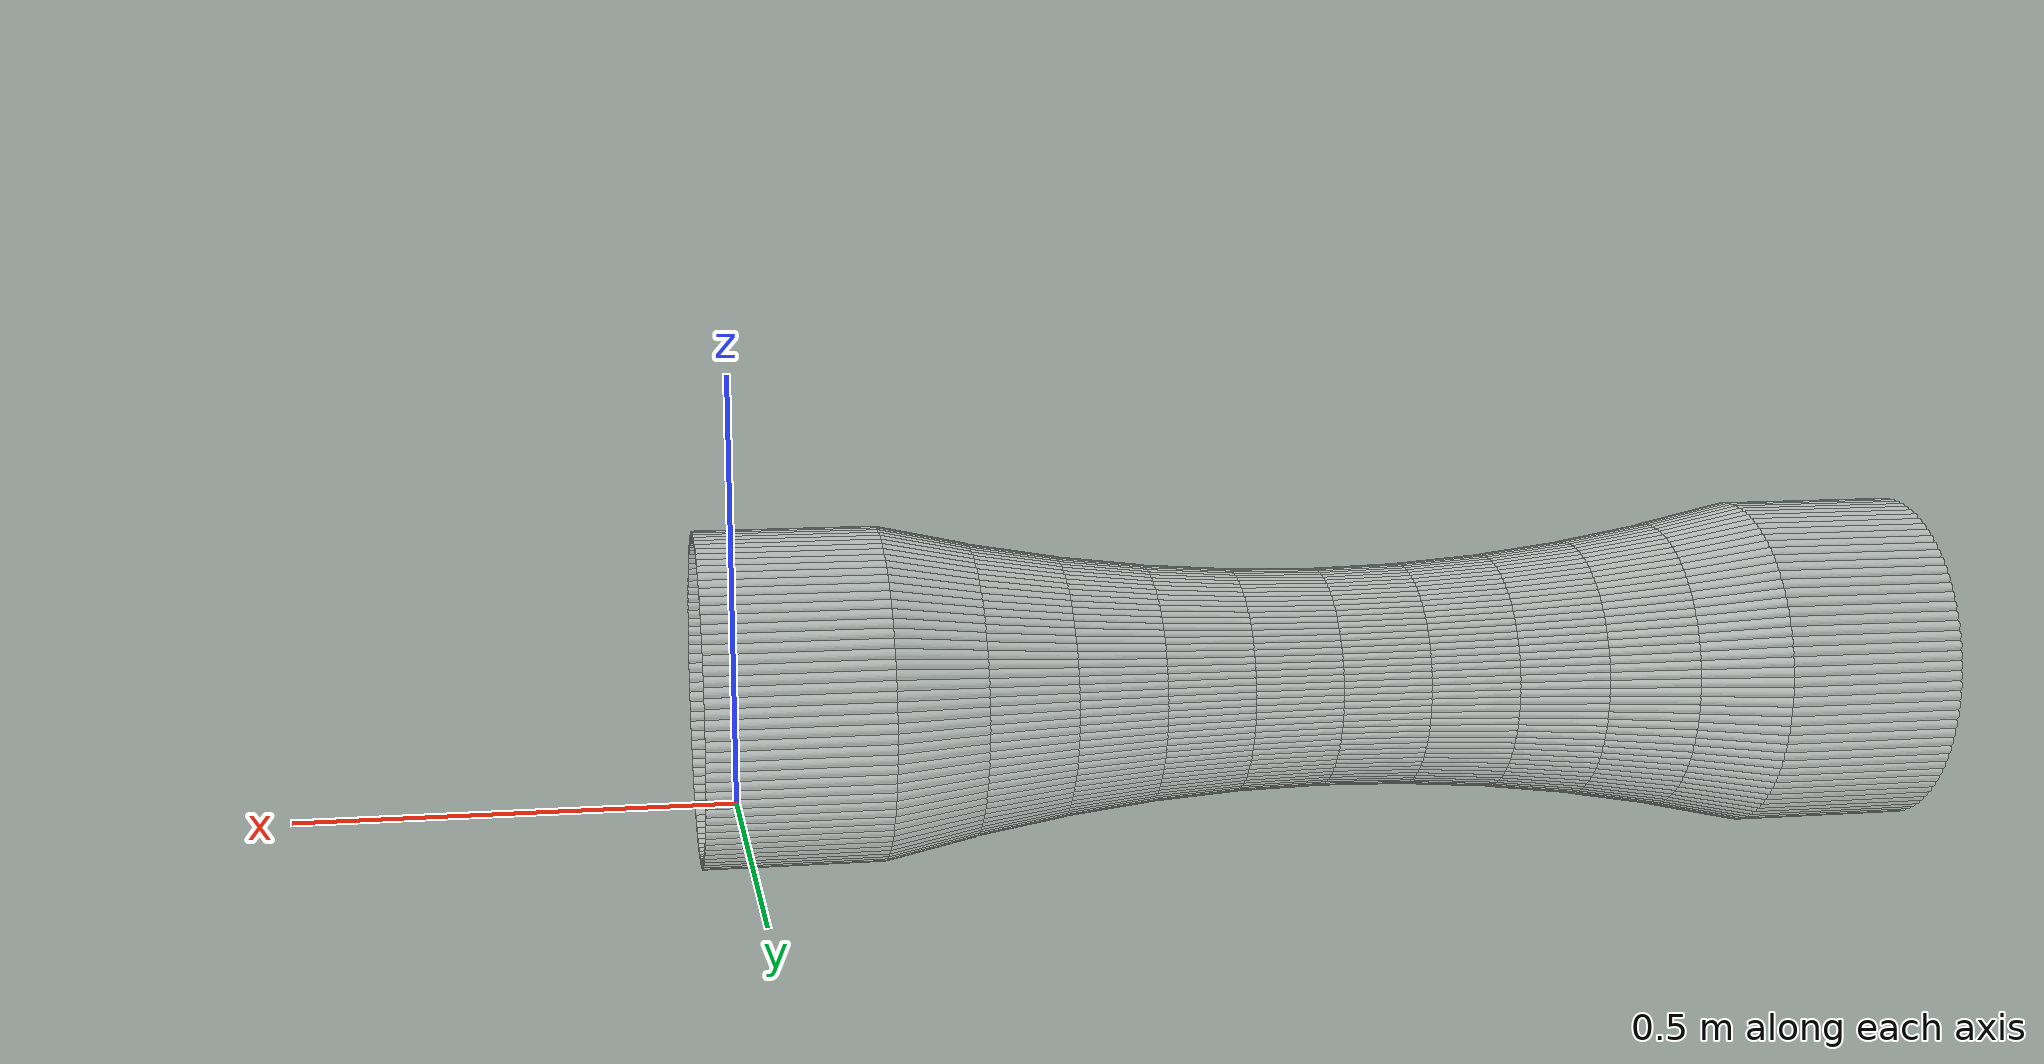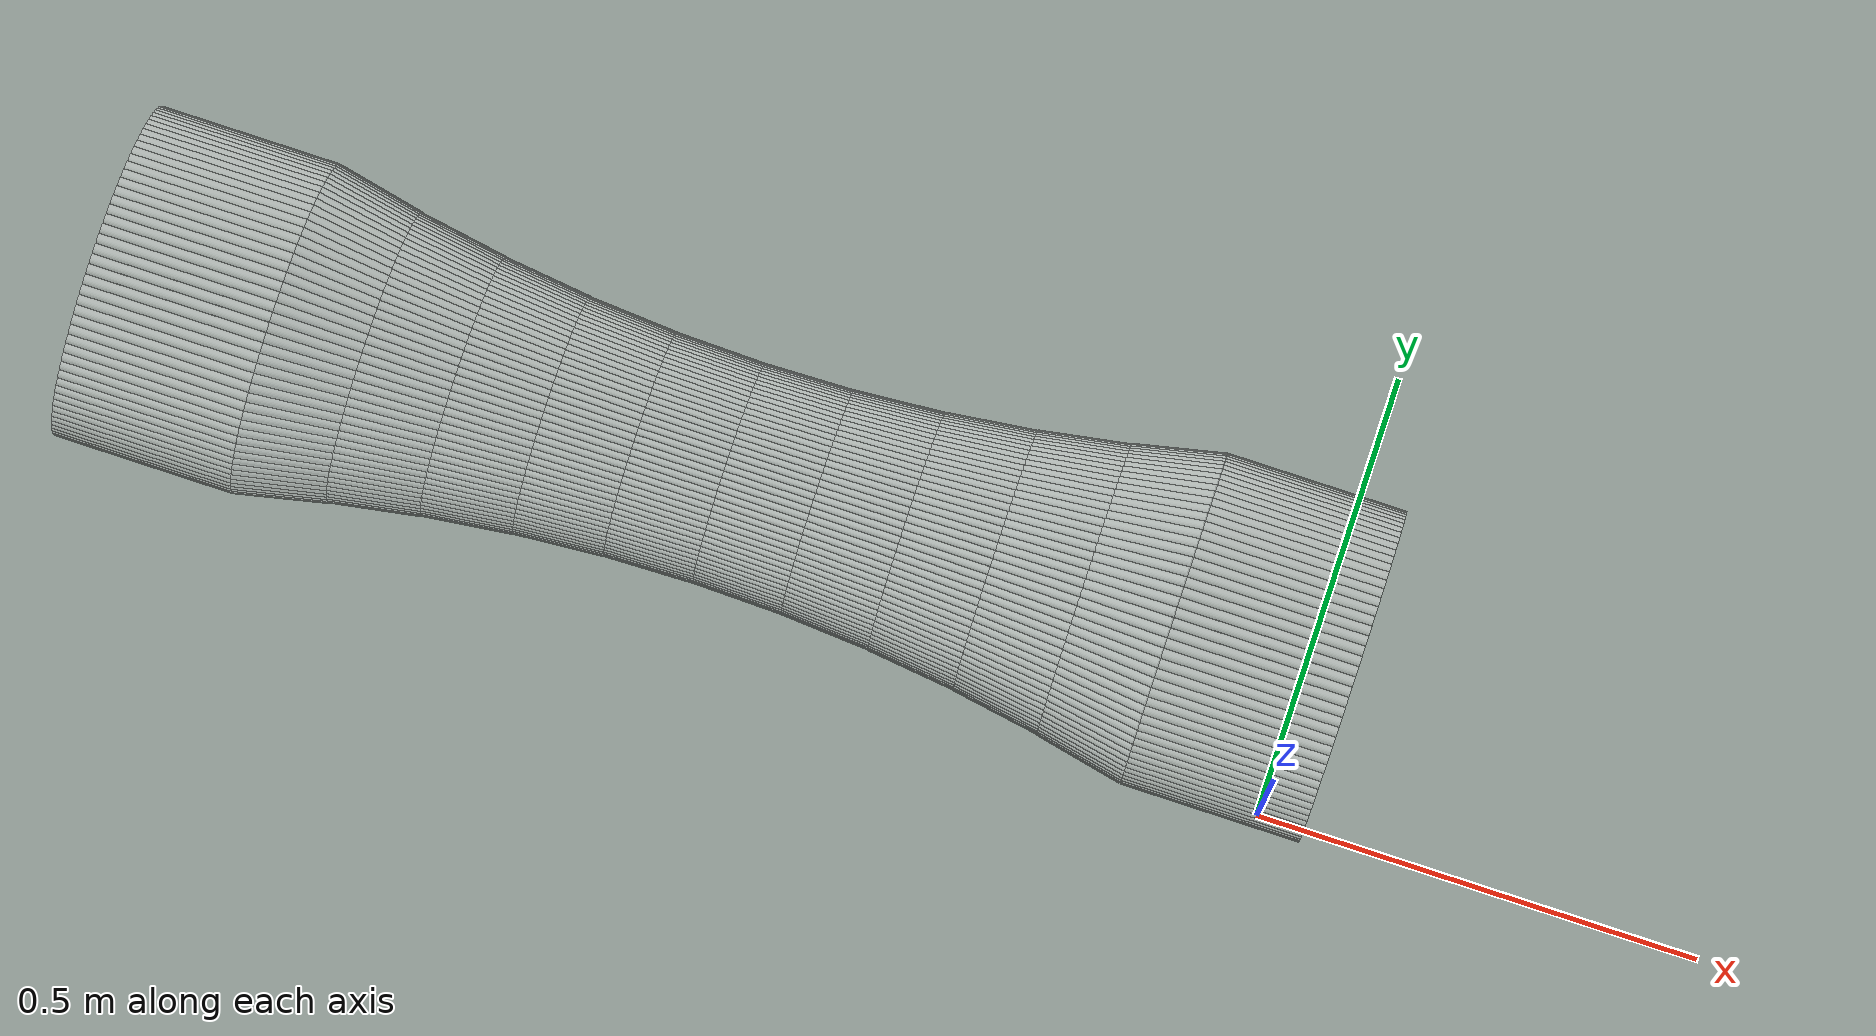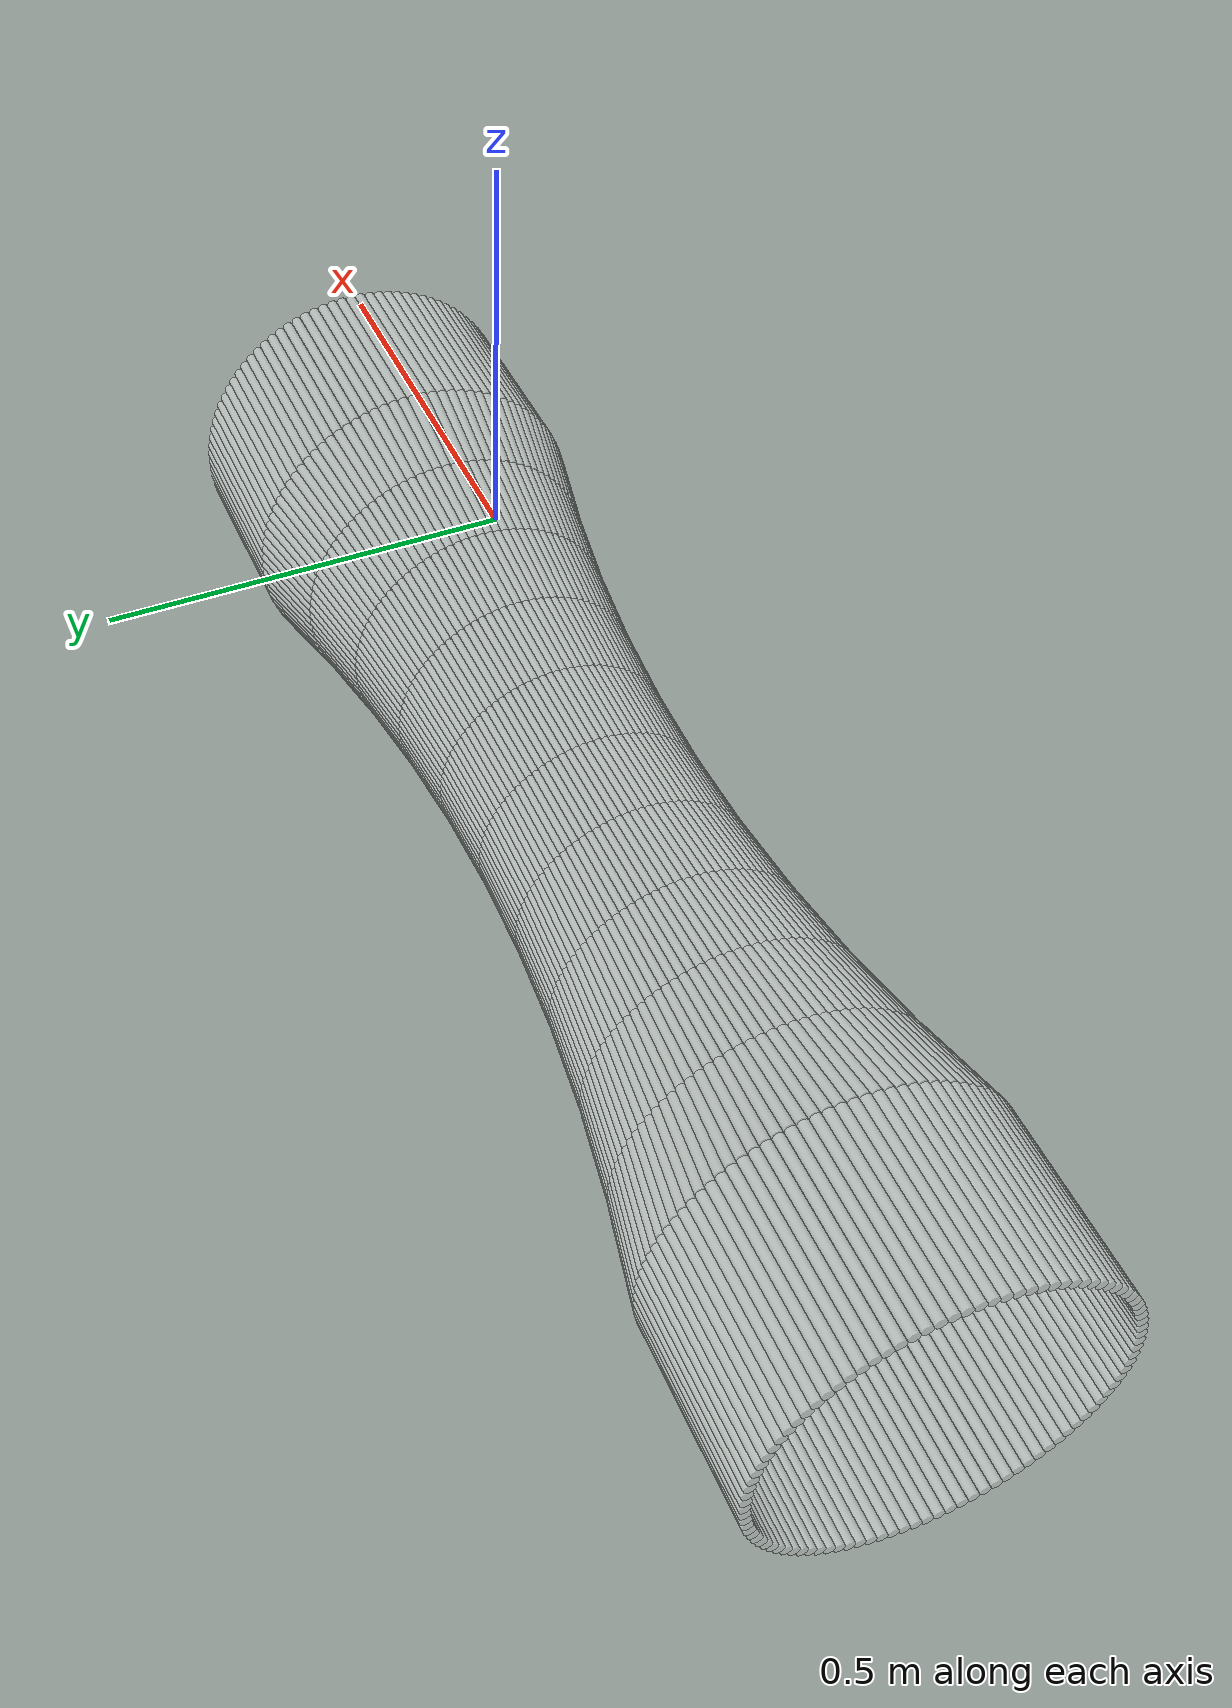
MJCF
<?xml version="1.0" encoding="utf-8"?>
<mujoco>
   <worldbody>
   <body pos="-0.15 0.16 -0.02" euler="0 0 90">
      <geom euler=" 0 10 0 " fromto="0.18 -0.2 0.18 0.18 0 0.18" rgba="1 1 1 0.35"
            size="0.0056539"
            type="cylinder"/>
      <geom euler=" 0 20 0 " fromto="0.17964 -0.2 0.1913 0.17964 0 0.1913"
            rgba="1 1 1 0.35"
            size="0.0056539"
            type="cylinder"/>
      <geom euler=" 0 30 0 " fromto="0.17858 -0.2 0.20256 0.17858 0 0.20256"
            rgba="1 1 1 0.35"
            size="0.0056539"
            type="cylinder"/>
      <geom euler=" 0 40 0 " fromto="0.17681 -0.2 0.21373 0.17681 0 0.21373"
            rgba="1 1 1 0.35"
            size="0.0056539"
            type="cylinder"/>
      <geom euler=" 0 50 0 " fromto="0.17434 -0.2 0.22476 0.17434 0 0.22476"
            rgba="1 1 1 0.35"
            size="0.0056539"
            type="cylinder"/>
      <geom euler=" 0 60 0 " fromto="0.17119 -0.2 0.23562 0.17119 0 0.23562"
            rgba="1 1 1 0.35"
            size="0.0056539"
            type="cylinder"/>
      <geom euler=" 0 70 0 " fromto="0.16736 -0.2 0.24626 0.16736 0 0.24626"
            rgba="1 1 1 0.35"
            size="0.0056539"
            type="cylinder"/>
      <geom euler=" 0 80 0 " fromto="0.16287 -0.2 0.25664 0.16287 0 0.25664"
            rgba="1 1 1 0.35"
            size="0.0056539"
            type="cylinder"/>
      <geom euler=" 0 90 0 " fromto="0.15774 -0.2 0.26672 0.15774 0 0.26672"
            rgba="1 1 1 0.35"
            size="0.0056539"
            type="cylinder"/>
      <geom euler=" 0 100 0 " fromto="0.15198 -0.2 0.27645 0.15198 0 0.27645"
            rgba="1 1 1 0.35"
            size="0.0056539"
            type="cylinder"/>
      <geom euler=" 0 110 0 " fromto="0.14562 -0.2 0.2858 0.14562 0 0.2858"
            rgba="1 1 1 0.35"
            size="0.0056539"
            type="cylinder"/>
      <geom euler=" 0 120 0 " fromto="0.13869 -0.2 0.29474 0.13869 0 0.29474"
            rgba="1 1 1 0.35"
            size="0.0056539"
            type="cylinder"/>
      <geom euler=" 0 130 0 " fromto="0.13121 -0.2 0.30322 0.13121 0 0.30322"
            rgba="1 1 1 0.35"
            size="0.0056539"
            type="cylinder"/>
      <geom euler=" 0 140 0 " fromto="0.12322 -0.2 0.31121 0.12322 0 0.31121"
            rgba="1 1 1 0.35"
            size="0.0056539"
            type="cylinder"/>
      <geom euler=" 0 150 0 " fromto="0.11474 -0.2 0.31869 0.11474 0 0.31869"
            rgba="1 1 1 0.35"
            size="0.0056539"
            type="cylinder"/>
      <geom euler=" 0 160 0 " fromto="0.1058 -0.2 0.32562 0.1058 0 0.32562"
            rgba="1 1 1 0.35"
            size="0.0056539"
            type="cylinder"/>
      <geom euler=" 0 170 0 " fromto="0.096449 -0.2 0.33198 0.096449 0 0.33198"
            rgba="1 1 1 0.35"
            size="0.0056539"
            type="cylinder"/>
      <geom euler=" 0 180 0 " fromto="0.086716 -0.2 0.33774 0.086716 0 0.33774"
            rgba="1 1 1 0.35"
            size="0.0056539"
            type="cylinder"/>
      <geom euler=" 0 190 0 " fromto="0.07664 -0.2 0.34287 0.07664 0 0.34287"
            rgba="1 1 1 0.35"
            size="0.0056539"
            type="cylinder"/>
      <geom euler=" 0 200 0 " fromto="0.066262 -0.2 0.34736 0.066262 0 0.34736"
            rgba="1 1 1 0.35"
            size="0.0056539"
            type="cylinder"/>
      <geom euler=" 0 210 0 " fromto="0.055623 -0.2 0.35119 0.055623 0 0.35119"
            rgba="1 1 1 0.35"
            size="0.0056539"
            type="cylinder"/>
      <geom euler=" 0 220 0 " fromto="0.044764 -0.2 0.35434 0.044764 0 0.35434"
            rgba="1 1 1 0.35"
            size="0.0056539"
            type="cylinder"/>
      <geom euler=" 0 230 0 " fromto="0.033729 -0.2 0.35681 0.033729 0 0.35681"
            rgba="1 1 1 0.35"
            size="0.0056539"
            type="cylinder"/>
      <geom euler=" 0 240 0 " fromto="0.02256 -0.2 0.35858 0.02256 0 0.35858"
            rgba="1 1 1 0.35"
            size="0.0056539"
            type="cylinder"/>
      <geom euler=" 0 250 0 " fromto="0.011302 -0.2 0.35964 0.011302 0 0.35964"
            rgba="1 1 1 0.35"
            size="0.0056539"
            type="cylinder"/>
      <geom euler=" 0 260 0 " fromto="1.1022e-17 -0.2 0.36 1.1022e-17 0 0.36"
            rgba="1 1 1 0.35"
            size="0.0056539"
            type="cylinder"/>
      <geom euler=" 0 270 0 " fromto="-0.011302 -0.2 0.35964 -0.011302 0 0.35964"
            rgba="1 1 1 0.35"
            size="0.0056539"
            type="cylinder"/>
      <geom euler=" 0 280 0 " fromto="-0.02256 -0.2 0.35858 -0.02256 0 0.35858"
            rgba="1 1 1 0.35"
            size="0.0056539"
            type="cylinder"/>
      <geom euler=" 0 290 0 " fromto="-0.033729 -0.2 0.35681 -0.033729 0 0.35681"
            rgba="1 1 1 0.35"
            size="0.0056539"
            type="cylinder"/>
      <geom euler=" 0 300 0 " fromto="-0.044764 -0.2 0.35434 -0.044764 0 0.35434"
            rgba="1 1 1 0.35"
            size="0.0056539"
            type="cylinder"/>
      <geom euler=" 0 310 0 " fromto="-0.055623 -0.2 0.35119 -0.055623 0 0.35119"
            rgba="1 1 1 0.35"
            size="0.0056539"
            type="cylinder"/>
      <geom euler=" 0 320 0 " fromto="-0.066262 -0.2 0.34736 -0.066262 0 0.34736"
            rgba="1 1 1 0.35"
            size="0.0056539"
            type="cylinder"/>
      <geom euler=" 0 330 0 " fromto="-0.07664 -0.2 0.34287 -0.07664 0 0.34287"
            rgba="1 1 1 0.35"
            size="0.0056539"
            type="cylinder"/>
      <geom euler=" 0 340 0 " fromto="-0.086716 -0.2 0.33774 -0.086716 0 0.33774"
            rgba="1 1 1 0.35"
            size="0.0056539"
            type="cylinder"/>
      <geom euler=" 0 350 0 " fromto="-0.096449 -0.2 0.33198 -0.096449 0 0.33198"
            rgba="1 1 1 0.35"
            size="0.0056539"
            type="cylinder"/>
      <geom euler=" 0 360 0 " fromto="-0.1058 -0.2 0.32562 -0.1058 0 0.32562"
            rgba="1 1 1 0.35"
            size="0.0056539"
            type="cylinder"/>
      <geom euler=" 0 370 0 " fromto="-0.11474 -0.2 0.31869 -0.11474 0 0.31869"
            rgba="1 1 1 0.35"
            size="0.0056539"
            type="cylinder"/>
      <geom euler=" 0 380 0 " fromto="-0.12322 -0.2 0.31121 -0.12322 0 0.31121"
            rgba="1 1 1 0.35"
            size="0.0056539"
            type="cylinder"/>
      <geom euler=" 0 390 0 " fromto="-0.13121 -0.2 0.30322 -0.13121 0 0.30322"
            rgba="1 1 1 0.35"
            size="0.0056539"
            type="cylinder"/>
      <geom euler=" 0 400 0 " fromto="-0.13869 -0.2 0.29474 -0.13869 0 0.29474"
            rgba="1 1 1 0.35"
            size="0.0056539"
            type="cylinder"/>
      <geom euler=" 0 410 0 " fromto="-0.14562 -0.2 0.2858 -0.14562 0 0.2858"
            rgba="1 1 1 0.35"
            size="0.0056539"
            type="cylinder"/>
      <geom euler=" 0 420 0 " fromto="-0.15198 -0.2 0.27645 -0.15198 0 0.27645"
            rgba="1 1 1 0.35"
            size="0.0056539"
            type="cylinder"/>
      <geom euler=" 0 430 0 " fromto="-0.15774 -0.2 0.26672 -0.15774 0 0.26672"
            rgba="1 1 1 0.35"
            size="0.0056539"
            type="cylinder"/>
      <geom euler=" 0 440 0 " fromto="-0.16287 -0.2 0.25664 -0.16287 0 0.25664"
            rgba="1 1 1 0.35"
            size="0.0056539"
            type="cylinder"/>
      <geom euler=" 0 450 0 " fromto="-0.16736 -0.2 0.24626 -0.16736 0 0.24626"
            rgba="1 1 1 0.35"
            size="0.0056539"
            type="cylinder"/>
      <geom euler=" 0 460 0 " fromto="-0.17119 -0.2 0.23562 -0.17119 0 0.23562"
            rgba="1 1 1 0.35"
            size="0.0056539"
            type="cylinder"/>
      <geom euler=" 0 470 0 " fromto="-0.17434 -0.2 0.22476 -0.17434 0 0.22476"
            rgba="1 1 1 0.35"
            size="0.0056539"
            type="cylinder"/>
      <geom euler=" 0 480 0 " fromto="-0.17681 -0.2 0.21373 -0.17681 0 0.21373"
            rgba="1 1 1 0.35"
            size="0.0056539"
            type="cylinder"/>
      <geom euler=" 0 490 0 " fromto="-0.17858 -0.2 0.20256 -0.17858 0 0.20256"
            rgba="1 1 1 0.35"
            size="0.0056539"
            type="cylinder"/>
      <geom euler=" 0 500 0 " fromto="-0.17964 -0.2 0.1913 -0.17964 0 0.1913"
            rgba="1 1 1 0.35"
            size="0.0056539"
            type="cylinder"/>
      <geom euler=" 0 510 0 " fromto="-0.18 -0.2 0.18 -0.18 0 0.18" rgba="1 1 1 0.35"
            size="0.0056539"
            type="cylinder"/>
      <geom euler=" 0 520 0 " fromto="-0.17964 -0.2 0.1687 -0.17964 0 0.1687"
            rgba="1 1 1 0.35"
            size="0.0056539"
            type="cylinder"/>
      <geom euler=" 0 530 0 " fromto="-0.17858 -0.2 0.15744 -0.17858 0 0.15744"
            rgba="1 1 1 0.35"
            size="0.0056539"
            type="cylinder"/>
      <geom euler=" 0 540 0 " fromto="-0.17681 -0.2 0.14627 -0.17681 0 0.14627"
            rgba="1 1 1 0.35"
            size="0.0056539"
            type="cylinder"/>
      <geom euler=" 0 550 0 " fromto="-0.17434 -0.2 0.13524 -0.17434 0 0.13524"
            rgba="1 1 1 0.35"
            size="0.0056539"
            type="cylinder"/>
      <geom euler=" 0 560 0 " fromto="-0.17119 -0.2 0.12438 -0.17119 0 0.12438"
            rgba="1 1 1 0.35"
            size="0.0056539"
            type="cylinder"/>
      <geom euler=" 0 570 0 " fromto="-0.16736 -0.2 0.11374 -0.16736 0 0.11374"
            rgba="1 1 1 0.35"
            size="0.0056539"
            type="cylinder"/>
      <geom euler=" 0 580 0 " fromto="-0.16287 -0.2 0.10336 -0.16287 0 0.10336"
            rgba="1 1 1 0.35"
            size="0.0056539"
            type="cylinder"/>
      <geom euler=" 0 590 0 " fromto="-0.15774 -0.2 0.093284 -0.15774 0 0.093284"
            rgba="1 1 1 0.35"
            size="0.0056539"
            type="cylinder"/>
      <geom euler=" 0 600 0 " fromto="-0.15198 -0.2 0.083551 -0.15198 0 0.083551"
            rgba="1 1 1 0.35"
            size="0.0056539"
            type="cylinder"/>
      <geom euler=" 0 610 0 " fromto="-0.14562 -0.2 0.074199 -0.14562 0 0.074199"
            rgba="1 1 1 0.35"
            size="0.0056539"
            type="cylinder"/>
      <geom euler=" 0 620 0 " fromto="-0.13869 -0.2 0.065264 -0.13869 0 0.065264"
            rgba="1 1 1 0.35"
            size="0.0056539"
            type="cylinder"/>
      <geom euler=" 0 630 0 " fromto="-0.13121 -0.2 0.056782 -0.13121 0 0.056782"
            rgba="1 1 1 0.35"
            size="0.0056539"
            type="cylinder"/>
      <geom euler=" 0 640 0 " fromto="-0.12322 -0.2 0.048786 -0.12322 0 0.048786"
            rgba="1 1 1 0.35"
            size="0.0056539"
            type="cylinder"/>
      <geom euler=" 0 650 0 " fromto="-0.11474 -0.2 0.041308 -0.11474 0 0.041308"
            rgba="1 1 1 0.35"
            size="0.0056539"
            type="cylinder"/>
      <geom euler=" 0 660 0 " fromto="-0.1058 -0.2 0.034377 -0.1058 0 0.034377"
            rgba="1 1 1 0.35"
            size="0.0056539"
            type="cylinder"/>
      <geom euler=" 0 670 0 " fromto="-0.096449 -0.2 0.028021 -0.096449 0 0.028021"
            rgba="1 1 1 0.35"
            size="0.0056539"
            type="cylinder"/>
      <geom euler=" 0 680 0 " fromto="-0.086716 -0.2 0.022265 -0.086716 0 0.022265"
            rgba="1 1 1 0.35"
            size="0.0056539"
            type="cylinder"/>
      <geom euler=" 0 690 0 " fromto="-0.07664 -0.2 0.017131 -0.07664 0 0.017131"
            rgba="1 1 1 0.35"
            size="0.0056539"
            type="cylinder"/>
      <geom euler=" 0 700 0 " fromto="-0.066262 -0.2 0.01264 -0.066262 0 0.01264"
            rgba="1 1 1 0.35"
            size="0.0056539"
            type="cylinder"/>
      <geom euler=" 0 710 0 " fromto="-0.055623 -0.2 0.0088098 -0.055623 0 0.0088098"
            rgba="1 1 1 0.35"
            size="0.0056539"
            type="cylinder"/>
      <geom euler=" 0 720 0 " fromto="-0.044764 -0.2 0.005655 -0.044764 0 0.005655"
            rgba="1 1 1 0.35"
            size="0.0056539"
            type="cylinder"/>
      <geom euler=" 0 730 0 " fromto="-0.033729 -0.2 0.0031883 -0.033729 0 0.0031883"
            rgba="1 1 1 0.35"
            size="0.0056539"
            type="cylinder"/>
      <geom euler=" 0 740 0 " fromto="-0.02256 -0.2 0.0014194 -0.02256 0 0.0014194"
            rgba="1 1 1 0.35"
            size="0.0056539"
            type="cylinder"/>
      <geom euler=" 0 750 0 " fromto="-0.011302 -0.2 0.00035519 -0.011302 0 0.00035519"
            rgba="1 1 1 0.35"
            size="0.0056539"
            type="cylinder"/>
      <geom euler=" 0 760 0 " fromto="-3.3065e-17 -0.2 0 -3.3065e-17 0 0" rgba="1 1 1 0.35"
            size="0.0056539"
            type="cylinder"/>
      <geom euler=" 0 770 0 " fromto="0.011302 -0.2 0.00035519 0.011302 0 0.00035519"
            rgba="1 1 1 0.35"
            size="0.0056539"
            type="cylinder"/>
      <geom euler=" 0 780 0 " fromto="0.02256 -0.2 0.0014194 0.02256 0 0.0014194"
            rgba="1 1 1 0.35"
            size="0.0056539"
            type="cylinder"/>
      <geom euler=" 0 790 0 " fromto="0.033729 -0.2 0.0031883 0.033729 0 0.0031883"
            rgba="1 1 1 0.35"
            size="0.0056539"
            type="cylinder"/>
      <geom euler=" 0 800 0 " fromto="0.044764 -0.2 0.005655 0.044764 0 0.005655"
            rgba="1 1 1 0.35"
            size="0.0056539"
            type="cylinder"/>
      <geom euler=" 0 810 0 " fromto="0.055623 -0.2 0.0088098 0.055623 0 0.0088098"
            rgba="1 1 1 0.35"
            size="0.0056539"
            type="cylinder"/>
      <geom euler=" 0 820 0 " fromto="0.066262 -0.2 0.01264 0.066262 0 0.01264"
            rgba="1 1 1 0.35"
            size="0.0056539"
            type="cylinder"/>
      <geom euler=" 0 830 0 " fromto="0.07664 -0.2 0.017131 0.07664 0 0.017131"
            rgba="1 1 1 0.35"
            size="0.0056539"
            type="cylinder"/>
      <geom euler=" 0 840 0 " fromto="0.086716 -0.2 0.022265 0.086716 0 0.022265"
            rgba="1 1 1 0.35"
            size="0.0056539"
            type="cylinder"/>
      <geom euler=" 0 850 0 " fromto="0.096449 -0.2 0.028021 0.096449 0 0.028021"
            rgba="1 1 1 0.35"
            size="0.0056539"
            type="cylinder"/>
      <geom euler=" 0 860 0 " fromto="0.1058 -0.2 0.034377 0.1058 0 0.034377"
            rgba="1 1 1 0.35"
            size="0.0056539"
            type="cylinder"/>
      <geom euler=" 0 870 0 " fromto="0.11474 -0.2 0.041308 0.11474 0 0.041308"
            rgba="1 1 1 0.35"
            size="0.0056539"
            type="cylinder"/>
      <geom euler=" 0 880 0 " fromto="0.12322 -0.2 0.048786 0.12322 0 0.048786"
            rgba="1 1 1 0.35"
            size="0.0056539"
            type="cylinder"/>
      <geom euler=" 0 890 0 " fromto="0.13121 -0.2 0.056782 0.13121 0 0.056782"
            rgba="1 1 1 0.35"
            size="0.0056539"
            type="cylinder"/>
      <geom euler=" 0 900 0 " fromto="0.13869 -0.2 0.065264 0.13869 0 0.065264"
            rgba="1 1 1 0.35"
            size="0.0056539"
            type="cylinder"/>
      <geom euler=" 0 910 0 " fromto="0.14562 -0.2 0.074199 0.14562 0 0.074199"
            rgba="1 1 1 0.35"
            size="0.0056539"
            type="cylinder"/>
      <geom euler=" 0 920 0 " fromto="0.15198 -0.2 0.083551 0.15198 0 0.083551"
            rgba="1 1 1 0.35"
            size="0.0056539"
            type="cylinder"/>
      <geom euler=" 0 930 0 " fromto="0.15774 -0.2 0.093284 0.15774 0 0.093284"
            rgba="1 1 1 0.35"
            size="0.0056539"
            type="cylinder"/>
      <geom euler=" 0 940 0 " fromto="0.16287 -0.2 0.10336 0.16287 0 0.10336"
            rgba="1 1 1 0.35"
            size="0.0056539"
            type="cylinder"/>
      <geom euler=" 0 950 0 " fromto="0.16736 -0.2 0.11374 0.16736 0 0.11374"
            rgba="1 1 1 0.35"
            size="0.0056539"
            type="cylinder"/>
      <geom euler=" 0 960 0 " fromto="0.17119 -0.2 0.12438 0.17119 0 0.12438"
            rgba="1 1 1 0.35"
            size="0.0056539"
            type="cylinder"/>
      <geom euler=" 0 970 0 " fromto="0.17434 -0.2 0.13524 0.17434 0 0.13524"
            rgba="1 1 1 0.35"
            size="0.0056539"
            type="cylinder"/>
      <geom euler=" 0 980 0 " fromto="0.17681 -0.2 0.14627 0.17681 0 0.14627"
            rgba="1 1 1 0.35"
            size="0.0056539"
            type="cylinder"/>
      <geom euler=" 0 990 0 " fromto="0.17858 -0.2 0.15744 0.17858 0 0.15744"
            rgba="1 1 1 0.35"
            size="0.0056539"
            type="cylinder"/>
      <geom euler=" 0 1000 0 " fromto="0.17964 -0.2 0.1687 0.17964 0 0.1687"
            rgba="1 1 1 0.35"
            size="0.0056539"
            type="cylinder"/>
      <geom euler=" 0 10 0 " fromto="0.18 0 0.18 0.1584 0.1 0.18" rgba="1 1 1 0.35"
            size="0.0056539"
            type="cylinder"/>
      <geom euler=" 0 20 0 " fromto="0.17964 0 0.1913 0.15809 0.1 0.18995"
            rgba="1 1 1 0.35"
            size="0.0056539"
            type="cylinder"/>
      <geom euler=" 0 30 0 " fromto="0.17858 0 0.20256 0.15715 0.1 0.19985"
            rgba="1 1 1 0.35"
            size="0.0056539"
            type="cylinder"/>
      <geom euler=" 0 40 0 " fromto="0.17681 0 0.21373 0.15559 0.1 0.20968"
            rgba="1 1 1 0.35"
            size="0.0056539"
            type="cylinder"/>
      <geom euler=" 0 50 0 " fromto="0.17434 0 0.22476 0.15342 0.1 0.21939"
            rgba="1 1 1 0.35"
            size="0.0056539"
            type="cylinder"/>
      <geom euler=" 0 60 0 " fromto="0.17119 0 0.23562 0.15065 0.1 0.22895"
            rgba="1 1 1 0.35"
            size="0.0056539"
            type="cylinder"/>
      <geom euler=" 0 70 0 " fromto="0.16736 0 0.24626 0.14728 0.1 0.23831"
            rgba="1 1 1 0.35"
            size="0.0056539"
            type="cylinder"/>
      <geom euler=" 0 80 0 " fromto="0.16287 0 0.25664 0.14332 0.1 0.24744"
            rgba="1 1 1 0.35"
            size="0.0056539"
            type="cylinder"/>
      <geom euler=" 0 90 0 " fromto="0.15774 0 0.26672 0.13881 0.1 0.25631"
            rgba="1 1 1 0.35"
            size="0.0056539"
            type="cylinder"/>
      <geom euler=" 0 100 0 " fromto="0.15198 0 0.27645 0.13374 0.1 0.26487"
            rgba="1 1 1 0.35"
            size="0.0056539"
            type="cylinder"/>
      <geom euler=" 0 110 0 " fromto="0.14562 0 0.2858 0.12815 0.1 0.27311"
            rgba="1 1 1 0.35"
            size="0.0056539"
            type="cylinder"/>
      <geom euler=" 0 120 0 " fromto="0.13869 0 0.29474 0.12205 0.1 0.28097"
            rgba="1 1 1 0.35"
            size="0.0056539"
            type="cylinder"/>
      <geom euler=" 0 130 0 " fromto="0.13121 0 0.30322 0.11547 0.1 0.28843"
            rgba="1 1 1 0.35"
            size="0.0056539"
            type="cylinder"/>
      <geom euler=" 0 140 0 " fromto="0.12322 0 0.31121 0.10843 0.1 0.29547"
            rgba="1 1 1 0.35"
            size="0.0056539"
            type="cylinder"/>
      <geom euler=" 0 150 0 " fromto="0.11474 0 0.31869 0.10097 0.1 0.30205"
            rgba="1 1 1 0.35"
            size="0.0056539"
            type="cylinder"/>
      <geom euler=" 0 160 0 " fromto="0.1058 0 0.32562 0.093105 0.1 0.30815"
            rgba="1 1 1 0.35"
            size="0.0056539"
            type="cylinder"/>
      <geom euler=" 0 170 0 " fromto="0.096449 0 0.33198 0.084875 0.1 0.31374"
            rgba="1 1 1 0.35"
            size="0.0056539"
            type="cylinder"/>
      <geom euler=" 0 180 0 " fromto="0.086716 0 0.33774 0.07631 0.1 0.31881"
            rgba="1 1 1 0.35"
            size="0.0056539"
            type="cylinder"/>
      <geom euler=" 0 190 0 " fromto="0.07664 0 0.34287 0.067443 0.1 0.32332"
            rgba="1 1 1 0.35"
            size="0.0056539"
            type="cylinder"/>
      <geom euler=" 0 200 0 " fromto="0.066262 0 0.34736 0.058311 0.1 0.32728"
            rgba="1 1 1 0.35"
            size="0.0056539"
            type="cylinder"/>
      <geom euler=" 0 210 0 " fromto="0.055623 0 0.35119 0.048948 0.1 0.33065"
            rgba="1 1 1 0.35"
            size="0.0056539"
            type="cylinder"/>
      <geom euler=" 0 220 0 " fromto="0.044764 0 0.35434 0.039392 0.1 0.33342"
            rgba="1 1 1 0.35"
            size="0.0056539"
            type="cylinder"/>
      <geom euler=" 0 230 0 " fromto="0.033729 0 0.35681 0.029681 0.1 0.33559"
            rgba="1 1 1 0.35"
            size="0.0056539"
            type="cylinder"/>
      <geom euler=" 0 240 0 " fromto="0.02256 0 0.35858 0.019853 0.1 0.33715"
            rgba="1 1 1 0.35"
            size="0.0056539"
            type="cylinder"/>
      <geom euler=" 0 250 0 " fromto="0.011302 0 0.35964 0.009946 0.1 0.33809"
            rgba="1 1 1 0.35"
            size="0.0056539"
            type="cylinder"/>
      <geom euler=" 0 260 0 " fromto="1.1022e-17 0 0.36 9.6992e-18 0.1 0.3384"
            rgba="1 1 1 0.35"
            size="0.0056539"
            type="cylinder"/>
      <geom euler=" 0 270 0 " fromto="-0.011302 0 0.35964 -0.009946 0.1 0.33809"
            rgba="1 1 1 0.35"
            size="0.0056539"
            type="cylinder"/>
      <geom euler=" 0 280 0 " fromto="-0.02256 0 0.35858 -0.019853 0.1 0.33715"
            rgba="1 1 1 0.35"
            size="0.0056539"
            type="cylinder"/>
      <geom euler=" 0 290 0 " fromto="-0.033729 0 0.35681 -0.029681 0.1 0.33559"
            rgba="1 1 1 0.35"
            size="0.0056539"
            type="cylinder"/>
      <geom euler=" 0 300 0 " fromto="-0.044764 0 0.35434 -0.039392 0.1 0.33342"
            rgba="1 1 1 0.35"
            size="0.0056539"
            type="cylinder"/>
      <geom euler=" 0 310 0 " fromto="-0.055623 0 0.35119 -0.048948 0.1 0.33065"
            rgba="1 1 1 0.35"
            size="0.0056539"
            type="cylinder"/>
      <geom euler=" 0 320 0 " fromto="-0.066262 0 0.34736 -0.058311 0.1 0.32728"
            rgba="1 1 1 0.35"
            size="0.0056539"
            type="cylinder"/>
      <geom euler=" 0 330 0 " fromto="-0.07664 0 0.34287 -0.067443 0.1 0.32332"
            rgba="1 1 1 0.35"
            size="0.0056539"
            type="cylinder"/>
      <geom euler=" 0 340 0 " fromto="-0.086716 0 0.33774 -0.07631 0.1 0.31881"
            rgba="1 1 1 0.35"
            size="0.0056539"
            type="cylinder"/>
      <geom euler=" 0 350 0 " fromto="-0.096449 0 0.33198 -0.084875 0.1 0.31374"
            rgba="1 1 1 0.35"
            size="0.0056539"
            type="cylinder"/>
      <geom euler=" 0 360 0 " fromto="-0.1058 0 0.32562 -0.093105 0.1 0.30815"
            rgba="1 1 1 0.35"
            size="0.0056539"
            type="cylinder"/>
      <geom euler=" 0 370 0 " fromto="-0.11474 0 0.31869 -0.10097 0.1 0.30205"
            rgba="1 1 1 0.35"
            size="0.0056539"
            type="cylinder"/>
      <geom euler=" 0 380 0 " fromto="-0.12322 0 0.31121 -0.10843 0.1 0.29547"
            rgba="1 1 1 0.35"
            size="0.0056539"
            type="cylinder"/>
      <geom euler=" 0 390 0 " fromto="-0.13121 0 0.30322 -0.11547 0.1 0.28843"
            rgba="1 1 1 0.35"
            size="0.0056539"
            type="cylinder"/>
      <geom euler=" 0 400 0 " fromto="-0.13869 0 0.29474 -0.12205 0.1 0.28097"
            rgba="1 1 1 0.35"
            size="0.0056539"
            type="cylinder"/>
      <geom euler=" 0 410 0 " fromto="-0.14562 0 0.2858 -0.12815 0.1 0.27311"
            rgba="1 1 1 0.35"
            size="0.0056539"
            type="cylinder"/>
      <geom euler=" 0 420 0 " fromto="-0.15198 0 0.27645 -0.13374 0.1 0.26487"
            rgba="1 1 1 0.35"
            size="0.0056539"
            type="cylinder"/>
      <geom euler=" 0 430 0 " fromto="-0.15774 0 0.26672 -0.13881 0.1 0.25631"
            rgba="1 1 1 0.35"
            size="0.0056539"
            type="cylinder"/>
      <geom euler=" 0 440 0 " fromto="-0.16287 0 0.25664 -0.14332 0.1 0.24744"
            rgba="1 1 1 0.35"
            size="0.0056539"
            type="cylinder"/>
      <geom euler=" 0 450 0 " fromto="-0.16736 0 0.24626 -0.14728 0.1 0.23831"
            rgba="1 1 1 0.35"
            size="0.0056539"
            type="cylinder"/>
      <geom euler=" 0 460 0 " fromto="-0.17119 0 0.23562 -0.15065 0.1 0.22895"
            rgba="1 1 1 0.35"
            size="0.0056539"
            type="cylinder"/>
      <geom euler=" 0 470 0 " fromto="-0.17434 0 0.22476 -0.15342 0.1 0.21939"
            rgba="1 1 1 0.35"
            size="0.0056539"
            type="cylinder"/>
      <geom euler=" 0 480 0 " fromto="-0.17681 0 0.21373 -0.15559 0.1 0.20968"
            rgba="1 1 1 0.35"
            size="0.0056539"
            type="cylinder"/>
      <geom euler=" 0 490 0 " fromto="-0.17858 0 0.20256 -0.15715 0.1 0.19985"
            rgba="1 1 1 0.35"
            size="0.0056539"
            type="cylinder"/>
      <geom euler=" 0 500 0 " fromto="-0.17964 0 0.1913 -0.15809 0.1 0.18995"
            rgba="1 1 1 0.35"
            size="0.0056539"
            type="cylinder"/>
      <geom euler=" 0 510 0 " fromto="-0.18 0 0.18 -0.1584 0.1 0.18" rgba="1 1 1 0.35"
            size="0.0056539"
            type="cylinder"/>
      <geom euler=" 0 520 0 " fromto="-0.17964 0 0.1687 -0.15809 0.1 0.17005"
            rgba="1 1 1 0.35"
            size="0.0056539"
            type="cylinder"/>
      <geom euler=" 0 530 0 " fromto="-0.17858 0 0.15744 -0.15715 0.1 0.16015"
            rgba="1 1 1 0.35"
            size="0.0056539"
            type="cylinder"/>
      <geom euler=" 0 540 0 " fromto="-0.17681 0 0.14627 -0.15559 0.1 0.15032"
            rgba="1 1 1 0.35"
            size="0.0056539"
            type="cylinder"/>
      <geom euler=" 0 550 0 " fromto="-0.17434 0 0.13524 -0.15342 0.1 0.14061"
            rgba="1 1 1 0.35"
            size="0.0056539"
            type="cylinder"/>
      <geom euler=" 0 560 0 " fromto="-0.17119 0 0.12438 -0.15065 0.1 0.13105"
            rgba="1 1 1 0.35"
            size="0.0056539"
            type="cylinder"/>
      <geom euler=" 0 570 0 " fromto="-0.16736 0 0.11374 -0.14728 0.1 0.12169"
            rgba="1 1 1 0.35"
            size="0.0056539"
            type="cylinder"/>
      <geom euler=" 0 580 0 " fromto="-0.16287 0 0.10336 -0.14332 0.1 0.11256"
            rgba="1 1 1 0.35"
            size="0.0056539"
            type="cylinder"/>
      <geom euler=" 0 590 0 " fromto="-0.15774 0 0.093284 -0.13881 0.1 0.10369"
            rgba="1 1 1 0.35"
            size="0.0056539"
            type="cylinder"/>
      <geom euler=" 0 600 0 " fromto="-0.15198 0 0.083551 -0.13374 0.1 0.095125"
            rgba="1 1 1 0.35"
            size="0.0056539"
            type="cylinder"/>
      <geom euler=" 0 610 0 " fromto="-0.14562 0 0.074199 -0.12815 0.1 0.086895"
            rgba="1 1 1 0.35"
            size="0.0056539"
            type="cylinder"/>
      <geom euler=" 0 620 0 " fromto="-0.13869 0 0.065264 -0.12205 0.1 0.079032"
            rgba="1 1 1 0.35"
            size="0.0056539"
            type="cylinder"/>
      <geom euler=" 0 630 0 " fromto="-0.13121 0 0.056782 -0.11547 0.1 0.071568"
            rgba="1 1 1 0.35"
            size="0.0056539"
            type="cylinder"/>
      <geom euler=" 0 640 0 " fromto="-0.12322 0 0.048786 -0.10843 0.1 0.064531"
            rgba="1 1 1 0.35"
            size="0.0056539"
            type="cylinder"/>
      <geom euler=" 0 650 0 " fromto="-0.11474 0 0.041308 -0.10097 0.1 0.057951"
            rgba="1 1 1 0.35"
            size="0.0056539"
            type="cylinder"/>
      <geom euler=" 0 660 0 " fromto="-0.1058 0 0.034377 -0.093105 0.1 0.051852"
            rgba="1 1 1 0.35"
            size="0.0056539"
            type="cylinder"/>
      <geom euler=" 0 670 0 " fromto="-0.096449 0 0.028021 -0.084875 0.1 0.046258"
            rgba="1 1 1 0.35"
            size="0.0056539"
            type="cylinder"/>
      <geom euler=" 0 680 0 " fromto="-0.086716 0 0.022265 -0.07631 0.1 0.041193"
            rgba="1 1 1 0.35"
            size="0.0056539"
            type="cylinder"/>
      <geom euler=" 0 690 0 " fromto="-0.07664 0 0.017131 -0.067443 0.1 0.036675"
            rgba="1 1 1 0.35"
            size="0.0056539"
            type="cylinder"/>
      <geom euler=" 0 700 0 " fromto="-0.066262 0 0.01264 -0.058311 0.1 0.032723"
            rgba="1 1 1 0.35"
            size="0.0056539"
            type="cylinder"/>
      <geom euler=" 0 710 0 " fromto="-0.055623 0 0.0088098 -0.048948 0.1 0.029353"
            rgba="1 1 1 0.35"
            size="0.0056539"
            type="cylinder"/>
      <geom euler=" 0 720 0 " fromto="-0.044764 0 0.005655 -0.039392 0.1 0.026576"
            rgba="1 1 1 0.35"
            size="0.0056539"
            type="cylinder"/>
      <geom euler=" 0 730 0 " fromto="-0.033729 0 0.0031883 -0.029681 0.1 0.024406"
            rgba="1 1 1 0.35"
            size="0.0056539"
            type="cylinder"/>
      <geom euler=" 0 740 0 " fromto="-0.02256 0 0.0014194 -0.019853 0.1 0.022849"
            rgba="1 1 1 0.35"
            size="0.0056539"
            type="cylinder"/>
      <geom euler=" 0 750 0 " fromto="-0.011302 0 0.00035519 -0.009946 0.1 0.021913"
            rgba="1 1 1 0.35"
            size="0.0056539"
            type="cylinder"/>
      <geom euler=" 0 760 0 " fromto="-3.3065e-17 0 0 -2.9098e-17 0.1 0.0216"
            rgba="1 1 1 0.35"
            size="0.0056539"
            type="cylinder"/>
      <geom euler=" 0 770 0 " fromto="0.011302 0 0.00035519 0.009946 0.1 0.021913"
            rgba="1 1 1 0.35"
            size="0.0056539"
            type="cylinder"/>
      <geom euler=" 0 780 0 " fromto="0.02256 0 0.0014194 0.019853 0.1 0.022849"
            rgba="1 1 1 0.35"
            size="0.0056539"
            type="cylinder"/>
      <geom euler=" 0 790 0 " fromto="0.033729 0 0.0031883 0.029681 0.1 0.024406"
            rgba="1 1 1 0.35"
            size="0.0056539"
            type="cylinder"/>
      <geom euler=" 0 800 0 " fromto="0.044764 0 0.005655 0.039392 0.1 0.026576"
            rgba="1 1 1 0.35"
            size="0.0056539"
            type="cylinder"/>
      <geom euler=" 0 810 0 " fromto="0.055623 0 0.0088098 0.048948 0.1 0.029353"
            rgba="1 1 1 0.35"
            size="0.0056539"
            type="cylinder"/>
      <geom euler=" 0 820 0 " fromto="0.066262 0 0.01264 0.058311 0.1 0.032723"
            rgba="1 1 1 0.35"
            size="0.0056539"
            type="cylinder"/>
      <geom euler=" 0 830 0 " fromto="0.07664 0 0.017131 0.067443 0.1 0.036675"
            rgba="1 1 1 0.35"
            size="0.0056539"
            type="cylinder"/>
      <geom euler=" 0 840 0 " fromto="0.086716 0 0.022265 0.07631 0.1 0.041193"
            rgba="1 1 1 0.35"
            size="0.0056539"
            type="cylinder"/>
      <geom euler=" 0 850 0 " fromto="0.096449 0 0.028021 0.084875 0.1 0.046258"
            rgba="1 1 1 0.35"
            size="0.0056539"
            type="cylinder"/>
      <geom euler=" 0 860 0 " fromto="0.1058 0 0.034377 0.093105 0.1 0.051852"
            rgba="1 1 1 0.35"
            size="0.0056539"
            type="cylinder"/>
      <geom euler=" 0 870 0 " fromto="0.11474 0 0.041308 0.10097 0.1 0.057951"
            rgba="1 1 1 0.35"
            size="0.0056539"
            type="cylinder"/>
      <geom euler=" 0 880 0 " fromto="0.12322 0 0.048786 0.10843 0.1 0.064531"
            rgba="1 1 1 0.35"
            size="0.0056539"
            type="cylinder"/>
      <geom euler=" 0 890 0 " fromto="0.13121 0 0.056782 0.11547 0.1 0.071568"
            rgba="1 1 1 0.35"
            size="0.0056539"
            type="cylinder"/>
      <geom euler=" 0 900 0 " fromto="0.13869 0 0.065264 0.12205 0.1 0.079032"
            rgba="1 1 1 0.35"
            size="0.0056539"
            type="cylinder"/>
      <geom euler=" 0 910 0 " fromto="0.14562 0 0.074199 0.12815 0.1 0.086895"
            rgba="1 1 1 0.35"
            size="0.0056539"
            type="cylinder"/>
      <geom euler=" 0 920 0 " fromto="0.15198 0 0.083551 0.13374 0.1 0.095125"
            rgba="1 1 1 0.35"
            size="0.0056539"
            type="cylinder"/>
      <geom euler=" 0 930 0 " fromto="0.15774 0 0.093284 0.13881 0.1 0.10369"
            rgba="1 1 1 0.35"
            size="0.0056539"
            type="cylinder"/>
      <geom euler=" 0 940 0 " fromto="0.16287 0 0.10336 0.14332 0.1 0.11256"
            rgba="1 1 1 0.35"
            size="0.0056539"
            type="cylinder"/>
      <geom euler=" 0 950 0 " fromto="0.16736 0 0.11374 0.14728 0.1 0.12169"
            rgba="1 1 1 0.35"
            size="0.0056539"
            type="cylinder"/>
      <geom euler=" 0 960 0 " fromto="0.17119 0 0.12438 0.15065 0.1 0.13105"
            rgba="1 1 1 0.35"
            size="0.0056539"
            type="cylinder"/>
      <geom euler=" 0 970 0 " fromto="0.17434 0 0.13524 0.15342 0.1 0.14061"
            rgba="1 1 1 0.35"
            size="0.0056539"
            type="cylinder"/>
      <geom euler=" 0 980 0 " fromto="0.17681 0 0.14627 0.15559 0.1 0.15032"
            rgba="1 1 1 0.35"
            size="0.0056539"
            type="cylinder"/>
      <geom euler=" 0 990 0 " fromto="0.17858 0 0.15744 0.15715 0.1 0.16015"
            rgba="1 1 1 0.35"
            size="0.0056539"
            type="cylinder"/>
      <geom euler=" 0 1000 0 " fromto="0.17964 0 0.1687 0.15809 0.1 0.17005"
            rgba="1 1 1 0.35"
            size="0.0056539"
            type="cylinder"/>
      <geom euler=" 0 10 0 " fromto="0.1584 0.1 0.18 0.1416 0.2 0.18" rgba="1 1 1 0.35"
            size="0.0049755"
            type="cylinder"/>
      <geom euler=" 0 20 0 " fromto="0.15809 0.1 0.18995 0.14132 0.2 0.18889"
            rgba="1 1 1 0.35"
            size="0.0049755"
            type="cylinder"/>
      <geom euler=" 0 30 0 " fromto="0.15715 0.1 0.19985 0.14048 0.2 0.19775"
            rgba="1 1 1 0.35"
            size="0.0049755"
            type="cylinder"/>
      <geom euler=" 0 40 0 " fromto="0.15559 0.1 0.20968 0.13909 0.2 0.20653"
            rgba="1 1 1 0.35"
            size="0.0049755"
            type="cylinder"/>
      <geom euler=" 0 50 0 " fromto="0.15342 0.1 0.21939 0.13715 0.2 0.21521"
            rgba="1 1 1 0.35"
            size="0.0049755"
            type="cylinder"/>
      <geom euler=" 0 60 0 " fromto="0.15065 0.1 0.22895 0.13467 0.2 0.22376"
            rgba="1 1 1 0.35"
            size="0.0049755"
            type="cylinder"/>
      <geom euler=" 0 70 0 " fromto="0.14728 0.1 0.23831 0.13166 0.2 0.23213"
            rgba="1 1 1 0.35"
            size="0.0049755"
            type="cylinder"/>
      <geom euler=" 0 80 0 " fromto="0.14332 0.1 0.24744 0.12812 0.2 0.24029"
            rgba="1 1 1 0.35"
            size="0.0049755"
            type="cylinder"/>
      <geom euler=" 0 90 0 " fromto="0.13881 0.1 0.25631 0.12409 0.2 0.24822"
            rgba="1 1 1 0.35"
            size="0.0049755"
            type="cylinder"/>
      <geom euler=" 0 100 0 " fromto="0.13374 0.1 0.26487 0.11956 0.2 0.25587"
            rgba="1 1 1 0.35"
            size="0.0049755"
            type="cylinder"/>
      <geom euler=" 0 110 0 " fromto="0.12815 0.1 0.27311 0.11456 0.2 0.26323"
            rgba="1 1 1 0.35"
            size="0.0049755"
            type="cylinder"/>
      <geom euler=" 0 120 0 " fromto="0.12205 0.1 0.28097 0.1091 0.2 0.27026"
            rgba="1 1 1 0.35"
            size="0.0049755"
            type="cylinder"/>
      <geom euler=" 0 130 0 " fromto="0.11547 0.1 0.28843 0.10322 0.2 0.27693"
            rgba="1 1 1 0.35"
            size="0.0049755"
            type="cylinder"/>
      <geom euler=" 0 140 0 " fromto="0.10843 0.1 0.29547 0.096932 0.2 0.28322"
            rgba="1 1 1 0.35"
            size="0.0049755"
            type="cylinder"/>
      <geom euler=" 0 150 0 " fromto="0.10097 0.1 0.30205 0.090259 0.2 0.2891"
            rgba="1 1 1 0.35"
            size="0.0049755"
            type="cylinder"/>
      <geom euler=" 0 160 0 " fromto="0.093105 0.1 0.30815 0.08323 0.2 0.29456"
            rgba="1 1 1 0.35"
            size="0.0049755"
            type="cylinder"/>
      <geom euler=" 0 170 0 " fromto="0.084875 0.1 0.31374 0.075873 0.2 0.29956"
            rgba="1 1 1 0.35"
            size="0.0049755"
            type="cylinder"/>
      <geom euler=" 0 180 0 " fromto="0.07631 0.1 0.31881 0.068216 0.2 0.30409"
            rgba="1 1 1 0.35"
            size="0.0049755"
            type="cylinder"/>
      <geom euler=" 0 190 0 " fromto="0.067443 0.1 0.32332 0.06029 0.2 0.30812"
            rgba="1 1 1 0.35"
            size="0.0049755"
            type="cylinder"/>
      <geom euler=" 0 200 0 " fromto="0.058311 0.1 0.32728 0.052126 0.2 0.31166"
            rgba="1 1 1 0.35"
            size="0.0049755"
            type="cylinder"/>
      <geom euler=" 0 210 0 " fromto="0.048948 0.1 0.33065 0.043757 0.2 0.31467"
            rgba="1 1 1 0.35"
            size="0.0049755"
            type="cylinder"/>
      <geom euler=" 0 220 0 " fromto="0.039392 0.1 0.33342 0.035214 0.2 0.31715"
            rgba="1 1 1 0.35"
            size="0.0049755"
            type="cylinder"/>
      <geom euler=" 0 230 0 " fromto="0.029681 0.1 0.33559 0.026533 0.2 0.31909"
            rgba="1 1 1 0.35"
            size="0.0049755"
            type="cylinder"/>
      <geom euler=" 0 240 0 " fromto="0.019853 0.1 0.33715 0.017747 0.2 0.32048"
            rgba="1 1 1 0.35"
            size="0.0049755"
            type="cylinder"/>
      <geom euler=" 0 250 0 " fromto="0.009946 0.1 0.33809 0.0088911 0.2 0.32132"
            rgba="1 1 1 0.35"
            size="0.0049755"
            type="cylinder"/>
      <geom euler=" 0 260 0 " fromto="9.6992e-18 0.1 0.3384 8.6705e-18 0.2 0.3216"
            rgba="1 1 1 0.35"
            size="0.0049755"
            type="cylinder"/>
      <geom euler=" 0 270 0 " fromto="-0.009946 0.1 0.33809 -0.0088911 0.2 0.32132"
            rgba="1 1 1 0.35"
            size="0.0049755"
            type="cylinder"/>
      <geom euler=" 0 280 0 " fromto="-0.019853 0.1 0.33715 -0.017747 0.2 0.32048"
            rgba="1 1 1 0.35"
            size="0.0049755"
            type="cylinder"/>
      <geom euler=" 0 290 0 " fromto="-0.029681 0.1 0.33559 -0.026533 0.2 0.31909"
            rgba="1 1 1 0.35"
            size="0.0049755"
            type="cylinder"/>
      <geom euler=" 0 300 0 " fromto="-0.039392 0.1 0.33342 -0.035214 0.2 0.31715"
            rgba="1 1 1 0.35"
            size="0.0049755"
            type="cylinder"/>
      <geom euler=" 0 310 0 " fromto="-0.048948 0.1 0.33065 -0.043757 0.2 0.31467"
            rgba="1 1 1 0.35"
            size="0.0049755"
            type="cylinder"/>
      <geom euler=" 0 320 0 " fromto="-0.058311 0.1 0.32728 -0.052126 0.2 0.31166"
            rgba="1 1 1 0.35"
            size="0.0049755"
            type="cylinder"/>
      <geom euler=" 0 330 0 " fromto="-0.067443 0.1 0.32332 -0.06029 0.2 0.30812"
            rgba="1 1 1 0.35"
            size="0.0049755"
            type="cylinder"/>
      <geom euler=" 0 340 0 " fromto="-0.07631 0.1 0.31881 -0.068216 0.2 0.30409"
            rgba="1 1 1 0.35"
            size="0.0049755"
            type="cylinder"/>
      <geom euler=" 0 350 0 " fromto="-0.084875 0.1 0.31374 -0.075873 0.2 0.29956"
            rgba="1 1 1 0.35"
            size="0.0049755"
            type="cylinder"/>
      <geom euler=" 0 360 0 " fromto="-0.093105 0.1 0.30815 -0.08323 0.2 0.29456"
            rgba="1 1 1 0.35"
            size="0.0049755"
            type="cylinder"/>
      <geom euler=" 0 370 0 " fromto="-0.10097 0.1 0.30205 -0.090259 0.2 0.2891"
            rgba="1 1 1 0.35"
            size="0.0049755"
            type="cylinder"/>
      <geom euler=" 0 380 0 " fromto="-0.10843 0.1 0.29547 -0.096932 0.2 0.28322"
            rgba="1 1 1 0.35"
            size="0.0049755"
            type="cylinder"/>
      <geom euler=" 0 390 0 " fromto="-0.11547 0.1 0.28843 -0.10322 0.2 0.27693"
            rgba="1 1 1 0.35"
            size="0.0049755"
            type="cylinder"/>
      <geom euler=" 0 400 0 " fromto="-0.12205 0.1 0.28097 -0.1091 0.2 0.27026"
            rgba="1 1 1 0.35"
            size="0.0049755"
            type="cylinder"/>
      <geom euler=" 0 410 0 " fromto="-0.12815 0.1 0.27311 -0.11456 0.2 0.26323"
            rgba="1 1 1 0.35"
            size="0.0049755"
            type="cylinder"/>
      <geom euler=" 0 420 0 " fromto="-0.13374 0.1 0.26487 -0.11956 0.2 0.25587"
            rgba="1 1 1 0.35"
            size="0.0049755"
            type="cylinder"/>
      <geom euler=" 0 430 0 " fromto="-0.13881 0.1 0.25631 -0.12409 0.2 0.24822"
            rgba="1 1 1 0.35"
            size="0.0049755"
            type="cylinder"/>
      <geom euler=" 0 440 0 " fromto="-0.14332 0.1 0.24744 -0.12812 0.2 0.24029"
            rgba="1 1 1 0.35"
            size="0.0049755"
            type="cylinder"/>
      <geom euler=" 0 450 0 " fromto="-0.14728 0.1 0.23831 -0.13166 0.2 0.23213"
            rgba="1 1 1 0.35"
            size="0.0049755"
            type="cylinder"/>
      <geom euler=" 0 460 0 " fromto="-0.15065 0.1 0.22895 -0.13467 0.2 0.22376"
            rgba="1 1 1 0.35"
            size="0.0049755"
            type="cylinder"/>
      <geom euler=" 0 470 0 " fromto="-0.15342 0.1 0.21939 -0.13715 0.2 0.21521"
            rgba="1 1 1 0.35"
            size="0.0049755"
            type="cylinder"/>
      <geom euler=" 0 480 0 " fromto="-0.15559 0.1 0.20968 -0.13909 0.2 0.20653"
            rgba="1 1 1 0.35"
            size="0.0049755"
            type="cylinder"/>
      <geom euler=" 0 490 0 " fromto="-0.15715 0.1 0.19985 -0.14048 0.2 0.19775"
            rgba="1 1 1 0.35"
            size="0.0049755"
            type="cylinder"/>
      <geom euler=" 0 500 0 " fromto="-0.15809 0.1 0.18995 -0.14132 0.2 0.18889"
            rgba="1 1 1 0.35"
            size="0.0049755"
            type="cylinder"/>
      <geom euler=" 0 510 0 " fromto="-0.1584 0.1 0.18 -0.1416 0.2 0.18" rgba="1 1 1 0.35"
            size="0.0049755"
            type="cylinder"/>
      <geom euler=" 0 520 0 " fromto="-0.15809 0.1 0.17005 -0.14132 0.2 0.17111"
            rgba="1 1 1 0.35"
            size="0.0049755"
            type="cylinder"/>
      <geom euler=" 0 530 0 " fromto="-0.15715 0.1 0.16015 -0.14048 0.2 0.16225"
            rgba="1 1 1 0.35"
            size="0.0049755"
            type="cylinder"/>
      <geom euler=" 0 540 0 " fromto="-0.15559 0.1 0.15032 -0.13909 0.2 0.15347"
            rgba="1 1 1 0.35"
            size="0.0049755"
            type="cylinder"/>
      <geom euler=" 0 550 0 " fromto="-0.15342 0.1 0.14061 -0.13715 0.2 0.14479"
            rgba="1 1 1 0.35"
            size="0.0049755"
            type="cylinder"/>
      <geom euler=" 0 560 0 " fromto="-0.15065 0.1 0.13105 -0.13467 0.2 0.13624"
            rgba="1 1 1 0.35"
            size="0.0049755"
            type="cylinder"/>
      <geom euler=" 0 570 0 " fromto="-0.14728 0.1 0.12169 -0.13166 0.2 0.12787"
            rgba="1 1 1 0.35"
            size="0.0049755"
            type="cylinder"/>
      <geom euler=" 0 580 0 " fromto="-0.14332 0.1 0.11256 -0.12812 0.2 0.11971"
            rgba="1 1 1 0.35"
            size="0.0049755"
            type="cylinder"/>
      <geom euler=" 0 590 0 " fromto="-0.13881 0.1 0.10369 -0.12409 0.2 0.11178"
            rgba="1 1 1 0.35"
            size="0.0049755"
            type="cylinder"/>
      <geom euler=" 0 600 0 " fromto="-0.13374 0.1 0.095125 -0.11956 0.2 0.10413"
            rgba="1 1 1 0.35"
            size="0.0049755"
            type="cylinder"/>
      <geom euler=" 0 610 0 " fromto="-0.12815 0.1 0.086895 -0.11456 0.2 0.09677"
            rgba="1 1 1 0.35"
            size="0.0049755"
            type="cylinder"/>
      <geom euler=" 0 620 0 " fromto="-0.12205 0.1 0.079032 -0.1091 0.2 0.089741"
            rgba="1 1 1 0.35"
            size="0.0049755"
            type="cylinder"/>
      <geom euler=" 0 630 0 " fromto="-0.11547 0.1 0.071568 -0.10322 0.2 0.083068"
            rgba="1 1 1 0.35"
            size="0.0049755"
            type="cylinder"/>
      <geom euler=" 0 640 0 " fromto="-0.10843 0.1 0.064531 -0.096932 0.2 0.076778"
            rgba="1 1 1 0.35"
            size="0.0049755"
            type="cylinder"/>
      <geom euler=" 0 650 0 " fromto="-0.10097 0.1 0.057951 -0.090259 0.2 0.070895"
            rgba="1 1 1 0.35"
            size="0.0049755"
            type="cylinder"/>
      <geom euler=" 0 660 0 " fromto="-0.093105 0.1 0.051852 -0.08323 0.2 0.065443"
            rgba="1 1 1 0.35"
            size="0.0049755"
            type="cylinder"/>
      <geom euler=" 0 670 0 " fromto="-0.084875 0.1 0.046258 -0.075873 0.2 0.060443"
            rgba="1 1 1 0.35"
            size="0.0049755"
            type="cylinder"/>
      <geom euler=" 0 680 0 " fromto="-0.07631 0.1 0.041193 -0.068216 0.2 0.055915"
            rgba="1 1 1 0.35"
            size="0.0049755"
            type="cylinder"/>
      <geom euler=" 0 690 0 " fromto="-0.067443 0.1 0.036675 -0.06029 0.2 0.051876"
            rgba="1 1 1 0.35"
            size="0.0049755"
            type="cylinder"/>
      <geom euler=" 0 700 0 " fromto="-0.058311 0.1 0.032723 -0.052126 0.2 0.048344"
            rgba="1 1 1 0.35"
            size="0.0049755"
            type="cylinder"/>
      <geom euler=" 0 710 0 " fromto="-0.048948 0.1 0.029353 -0.043757 0.2 0.04533"
            rgba="1 1 1 0.35"
            size="0.0049755"
            type="cylinder"/>
      <geom euler=" 0 720 0 " fromto="-0.039392 0.1 0.026576 -0.035214 0.2 0.042849"
            rgba="1 1 1 0.35"
            size="0.0049755"
            type="cylinder"/>
      <geom euler=" 0 730 0 " fromto="-0.029681 0.1 0.024406 -0.026533 0.2 0.040908"
            rgba="1 1 1 0.35"
            size="0.0049755"
            type="cylinder"/>
      <geom euler=" 0 740 0 " fromto="-0.019853 0.1 0.022849 -0.017747 0.2 0.039517"
            rgba="1 1 1 0.35"
            size="0.0049755"
            type="cylinder"/>
      <geom euler=" 0 750 0 " fromto="-0.009946 0.1 0.021913 -0.0088911 0.2 0.038679"
            rgba="1 1 1 0.35"
            size="0.0049755"
            type="cylinder"/>
      <geom euler=" 0 760 0 " fromto="-2.9098e-17 0.1 0.0216 -2.6011e-17 0.2 0.0384"
            rgba="1 1 1 0.35"
            size="0.0049755"
            type="cylinder"/>
      <geom euler=" 0 770 0 " fromto="0.009946 0.1 0.021913 0.0088911 0.2 0.038679"
            rgba="1 1 1 0.35"
            size="0.0049755"
            type="cylinder"/>
      <geom euler=" 0 780 0 " fromto="0.019853 0.1 0.022849 0.017747 0.2 0.039517"
            rgba="1 1 1 0.35"
            size="0.0049755"
            type="cylinder"/>
      <geom euler=" 0 790 0 " fromto="0.029681 0.1 0.024406 0.026533 0.2 0.040908"
            rgba="1 1 1 0.35"
            size="0.0049755"
            type="cylinder"/>
      <geom euler=" 0 800 0 " fromto="0.039392 0.1 0.026576 0.035214 0.2 0.042849"
            rgba="1 1 1 0.35"
            size="0.0049755"
            type="cylinder"/>
      <geom euler=" 0 810 0 " fromto="0.048948 0.1 0.029353 0.043757 0.2 0.04533"
            rgba="1 1 1 0.35"
            size="0.0049755"
            type="cylinder"/>
      <geom euler=" 0 820 0 " fromto="0.058311 0.1 0.032723 0.052126 0.2 0.048344"
            rgba="1 1 1 0.35"
            size="0.0049755"
            type="cylinder"/>
      <geom euler=" 0 830 0 " fromto="0.067443 0.1 0.036675 0.06029 0.2 0.051876"
            rgba="1 1 1 0.35"
            size="0.0049755"
            type="cylinder"/>
      <geom euler=" 0 840 0 " fromto="0.07631 0.1 0.041193 0.068216 0.2 0.055915"
            rgba="1 1 1 0.35"
            size="0.0049755"
            type="cylinder"/>
      <geom euler=" 0 850 0 " fromto="0.084875 0.1 0.046258 0.075873 0.2 0.060443"
            rgba="1 1 1 0.35"
            size="0.0049755"
            type="cylinder"/>
      <geom euler=" 0 860 0 " fromto="0.093105 0.1 0.051852 0.08323 0.2 0.065443"
            rgba="1 1 1 0.35"
            size="0.0049755"
            type="cylinder"/>
      <geom euler=" 0 870 0 " fromto="0.10097 0.1 0.057951 0.090259 0.2 0.070895"
            rgba="1 1 1 0.35"
            size="0.0049755"
            type="cylinder"/>
      <geom euler=" 0 880 0 " fromto="0.10843 0.1 0.064531 0.096932 0.2 0.076778"
            rgba="1 1 1 0.35"
            size="0.0049755"
            type="cylinder"/>
      <geom euler=" 0 890 0 " fromto="0.11547 0.1 0.071568 0.10322 0.2 0.083068"
            rgba="1 1 1 0.35"
            size="0.0049755"
            type="cylinder"/>
      <geom euler=" 0 900 0 " fromto="0.12205 0.1 0.079032 0.1091 0.2 0.089741"
            rgba="1 1 1 0.35"
            size="0.0049755"
            type="cylinder"/>
      <geom euler=" 0 910 0 " fromto="0.12815 0.1 0.086895 0.11456 0.2 0.09677"
            rgba="1 1 1 0.35"
            size="0.0049755"
            type="cylinder"/>
      <geom euler=" 0 920 0 " fromto="0.13374 0.1 0.095125 0.11956 0.2 0.10413"
            rgba="1 1 1 0.35"
            size="0.0049755"
            type="cylinder"/>
      <geom euler=" 0 930 0 " fromto="0.13881 0.1 0.10369 0.12409 0.2 0.11178"
            rgba="1 1 1 0.35"
            size="0.0049755"
            type="cylinder"/>
      <geom euler=" 0 940 0 " fromto="0.14332 0.1 0.11256 0.12812 0.2 0.11971"
            rgba="1 1 1 0.35"
            size="0.0049755"
            type="cylinder"/>
      <geom euler=" 0 950 0 " fromto="0.14728 0.1 0.12169 0.13166 0.2 0.12787"
            rgba="1 1 1 0.35"
            size="0.0049755"
            type="cylinder"/>
      <geom euler=" 0 960 0 " fromto="0.15065 0.1 0.13105 0.13467 0.2 0.13624"
            rgba="1 1 1 0.35"
            size="0.0049755"
            type="cylinder"/>
      <geom euler=" 0 970 0 " fromto="0.15342 0.1 0.14061 0.13715 0.2 0.14479"
            rgba="1 1 1 0.35"
            size="0.0049755"
            type="cylinder"/>
      <geom euler=" 0 980 0 " fromto="0.15559 0.1 0.15032 0.13909 0.2 0.15347"
            rgba="1 1 1 0.35"
            size="0.0049755"
            type="cylinder"/>
      <geom euler=" 0 990 0 " fromto="0.15715 0.1 0.16015 0.14048 0.2 0.16225"
            rgba="1 1 1 0.35"
            size="0.0049755"
            type="cylinder"/>
      <geom euler=" 0 1000 0 " fromto="0.15809 0.1 0.17005 0.14132 0.2 0.17111"
            rgba="1 1 1 0.35"
            size="0.0049755"
            type="cylinder"/>
      <geom euler=" 0 10 0 " fromto="0.1416 0.2 0.18 0.1296 0.3 0.18" rgba="1 1 1 0.35"
            size="0.0044478"
            type="cylinder"/>
      <geom euler=" 0 20 0 " fromto="0.14132 0.2 0.18889 0.12934 0.3 0.18814"
            rgba="1 1 1 0.35"
            size="0.0044478"
            type="cylinder"/>
      <geom euler=" 0 30 0 " fromto="0.14048 0.2 0.19775 0.12858 0.3 0.19624"
            rgba="1 1 1 0.35"
            size="0.0044478"
            type="cylinder"/>
      <geom euler=" 0 40 0 " fromto="0.13909 0.2 0.20653 0.1273 0.3 0.20428"
            rgba="1 1 1 0.35"
            size="0.0044478"
            type="cylinder"/>
      <geom euler=" 0 50 0 " fromto="0.13715 0.2 0.21521 0.12553 0.3 0.21223"
            rgba="1 1 1 0.35"
            size="0.0044478"
            type="cylinder"/>
      <geom euler=" 0 60 0 " fromto="0.13467 0.2 0.22376 0.12326 0.3 0.22005"
            rgba="1 1 1 0.35"
            size="0.0044478"
            type="cylinder"/>
      <geom euler=" 0 70 0 " fromto="0.13166 0.2 0.23213 0.1205 0.3 0.22771"
            rgba="1 1 1 0.35"
            size="0.0044478"
            type="cylinder"/>
      <geom euler=" 0 80 0 " fromto="0.12812 0.2 0.24029 0.11727 0.3 0.23518"
            rgba="1 1 1 0.35"
            size="0.0044478"
            type="cylinder"/>
      <geom euler=" 0 90 0 " fromto="0.12409 0.2 0.24822 0.11357 0.3 0.24244"
            rgba="1 1 1 0.35"
            size="0.0044478"
            type="cylinder"/>
      <geom euler=" 0 100 0 " fromto="0.11956 0.2 0.25587 0.10942 0.3 0.24944"
            rgba="1 1 1 0.35"
            size="0.0044478"
            type="cylinder"/>
      <geom euler=" 0 110 0 " fromto="0.11456 0.2 0.26323 0.10485 0.3 0.25618"
            rgba="1 1 1 0.35"
            size="0.0044478"
            type="cylinder"/>
      <geom euler=" 0 120 0 " fromto="0.1091 0.2 0.27026 0.099859 0.3 0.26261"
            rgba="1 1 1 0.35"
            size="0.0044478"
            type="cylinder"/>
      <geom euler=" 0 130 0 " fromto="0.10322 0.2 0.27693 0.094474 0.3 0.26872"
            rgba="1 1 1 0.35"
            size="0.0044478"
            type="cylinder"/>
      <geom euler=" 0 140 0 " fromto="0.096932 0.2 0.28322 0.088717 0.3 0.27447"
            rgba="1 1 1 0.35"
            size="0.0044478"
            type="cylinder"/>
      <geom euler=" 0 150 0 " fromto="0.090259 0.2 0.2891 0.08261 0.3 0.27986"
            rgba="1 1 1 0.35"
            size="0.0044478"
            type="cylinder"/>
      <geom euler=" 0 160 0 " fromto="0.08323 0.2 0.29456 0.076177 0.3 0.28485"
            rgba="1 1 1 0.35"
            size="0.0044478"
            type="cylinder"/>
      <geom euler=" 0 170 0 " fromto="0.075873 0.2 0.29956 0.069443 0.3 0.28942"
            rgba="1 1 1 0.35"
            size="0.0044478"
            type="cylinder"/>
      <geom euler=" 0 180 0 " fromto="0.068216 0.2 0.30409 0.062435 0.3 0.29357"
            rgba="1 1 1 0.35"
            size="0.0044478"
            type="cylinder"/>
      <geom euler=" 0 190 0 " fromto="0.06029 0.2 0.30812 0.055181 0.3 0.29727"
            rgba="1 1 1 0.35"
            size="0.0044478"
            type="cylinder"/>
      <geom euler=" 0 200 0 " fromto="0.052126 0.2 0.31166 0.047709 0.3 0.3005"
            rgba="1 1 1 0.35"
            size="0.0044478"
            type="cylinder"/>
      <geom euler=" 0 210 0 " fromto="0.043757 0.2 0.31467 0.040049 0.3 0.30326"
            rgba="1 1 1 0.35"
            size="0.0044478"
            type="cylinder"/>
      <geom euler=" 0 220 0 " fromto="0.035214 0.2 0.31715 0.03223 0.3 0.30553"
            rgba="1 1 1 0.35"
            size="0.0044478"
            type="cylinder"/>
      <geom euler=" 0 230 0 " fromto="0.026533 0.2 0.31909 0.024285 0.3 0.3073"
            rgba="1 1 1 0.35"
            size="0.0044478"
            type="cylinder"/>
      <geom euler=" 0 240 0 " fromto="0.017747 0.2 0.32048 0.016243 0.3 0.30858"
            rgba="1 1 1 0.35"
            size="0.0044478"
            type="cylinder"/>
      <geom euler=" 0 250 0 " fromto="0.0088911 0.2 0.32132 0.0081377 0.3 0.30934"
            rgba="1 1 1 0.35"
            size="0.0044478"
            type="cylinder"/>
      <geom euler=" 0 260 0 " fromto="8.6705e-18 0.2 0.3216 7.9357e-18 0.3 0.3096"
            rgba="1 1 1 0.35"
            size="0.0044478"
            type="cylinder"/>
      <geom euler=" 0 270 0 " fromto="-0.0088911 0.2 0.32132 -0.0081377 0.3 0.30934"
            rgba="1 1 1 0.35"
            size="0.0044478"
            type="cylinder"/>
      <geom euler=" 0 280 0 " fromto="-0.017747 0.2 0.32048 -0.016243 0.3 0.30858"
            rgba="1 1 1 0.35"
            size="0.0044478"
            type="cylinder"/>
      <geom euler=" 0 290 0 " fromto="-0.026533 0.2 0.31909 -0.024285 0.3 0.3073"
            rgba="1 1 1 0.35"
            size="0.0044478"
            type="cylinder"/>
      <geom euler=" 0 300 0 " fromto="-0.035214 0.2 0.31715 -0.03223 0.3 0.30553"
            rgba="1 1 1 0.35"
            size="0.0044478"
            type="cylinder"/>
      <geom euler=" 0 310 0 " fromto="-0.043757 0.2 0.31467 -0.040049 0.3 0.30326"
            rgba="1 1 1 0.35"
            size="0.0044478"
            type="cylinder"/>
      <geom euler=" 0 320 0 " fromto="-0.052126 0.2 0.31166 -0.047709 0.3 0.3005"
            rgba="1 1 1 0.35"
            size="0.0044478"
            type="cylinder"/>
      <geom euler=" 0 330 0 " fromto="-0.06029 0.2 0.30812 -0.055181 0.3 0.29727"
            rgba="1 1 1 0.35"
            size="0.0044478"
            type="cylinder"/>
      <geom euler=" 0 340 0 " fromto="-0.068216 0.2 0.30409 -0.062435 0.3 0.29357"
            rgba="1 1 1 0.35"
            size="0.0044478"
            type="cylinder"/>
      <geom euler=" 0 350 0 " fromto="-0.075873 0.2 0.29956 -0.069443 0.3 0.28942"
            rgba="1 1 1 0.35"
            size="0.0044478"
            type="cylinder"/>
      <geom euler=" 0 360 0 " fromto="-0.08323 0.2 0.29456 -0.076177 0.3 0.28485"
            rgba="1 1 1 0.35"
            size="0.0044478"
            type="cylinder"/>
      <geom euler=" 0 370 0 " fromto="-0.090259 0.2 0.2891 -0.08261 0.3 0.27986"
            rgba="1 1 1 0.35"
            size="0.0044478"
            type="cylinder"/>
      <geom euler=" 0 380 0 " fromto="-0.096932 0.2 0.28322 -0.088717 0.3 0.27447"
            rgba="1 1 1 0.35"
            size="0.0044478"
            type="cylinder"/>
      <geom euler=" 0 390 0 " fromto="-0.10322 0.2 0.27693 -0.094474 0.3 0.26872"
            rgba="1 1 1 0.35"
            size="0.0044478"
            type="cylinder"/>
      <geom euler=" 0 400 0 " fromto="-0.1091 0.2 0.27026 -0.099859 0.3 0.26261"
            rgba="1 1 1 0.35"
            size="0.0044478"
            type="cylinder"/>
      <geom euler=" 0 410 0 " fromto="-0.11456 0.2 0.26323 -0.10485 0.3 0.25618"
            rgba="1 1 1 0.35"
            size="0.0044478"
            type="cylinder"/>
      <geom euler=" 0 420 0 " fromto="-0.11956 0.2 0.25587 -0.10942 0.3 0.24944"
            rgba="1 1 1 0.35"
            size="0.0044478"
            type="cylinder"/>
      <geom euler=" 0 430 0 " fromto="-0.12409 0.2 0.24822 -0.11357 0.3 0.24244"
            rgba="1 1 1 0.35"
            size="0.0044478"
            type="cylinder"/>
      <geom euler=" 0 440 0 " fromto="-0.12812 0.2 0.24029 -0.11727 0.3 0.23518"
            rgba="1 1 1 0.35"
            size="0.0044478"
            type="cylinder"/>
      <geom euler=" 0 450 0 " fromto="-0.13166 0.2 0.23213 -0.1205 0.3 0.22771"
            rgba="1 1 1 0.35"
            size="0.0044478"
            type="cylinder"/>
      <geom euler=" 0 460 0 " fromto="-0.13467 0.2 0.22376 -0.12326 0.3 0.22005"
            rgba="1 1 1 0.35"
            size="0.0044478"
            type="cylinder"/>
      <geom euler=" 0 470 0 " fromto="-0.13715 0.2 0.21521 -0.12553 0.3 0.21223"
            rgba="1 1 1 0.35"
            size="0.0044478"
            type="cylinder"/>
      <geom euler=" 0 480 0 " fromto="-0.13909 0.2 0.20653 -0.1273 0.3 0.20428"
            rgba="1 1 1 0.35"
            size="0.0044478"
            type="cylinder"/>
      <geom euler=" 0 490 0 " fromto="-0.14048 0.2 0.19775 -0.12858 0.3 0.19624"
            rgba="1 1 1 0.35"
            size="0.0044478"
            type="cylinder"/>
      <geom euler=" 0 500 0 " fromto="-0.14132 0.2 0.18889 -0.12934 0.3 0.18814"
            rgba="1 1 1 0.35"
            size="0.0044478"
            type="cylinder"/>
      <geom euler=" 0 510 0 " fromto="-0.1416 0.2 0.18 -0.1296 0.3 0.18" rgba="1 1 1 0.35"
            size="0.0044478"
            type="cylinder"/>
      <geom euler=" 0 520 0 " fromto="-0.14132 0.2 0.17111 -0.12934 0.3 0.17186"
            rgba="1 1 1 0.35"
            size="0.0044478"
            type="cylinder"/>
      <geom euler=" 0 530 0 " fromto="-0.14048 0.2 0.16225 -0.12858 0.3 0.16376"
            rgba="1 1 1 0.35"
            size="0.0044478"
            type="cylinder"/>
      <geom euler=" 0 540 0 " fromto="-0.13909 0.2 0.15347 -0.1273 0.3 0.15572"
            rgba="1 1 1 0.35"
            size="0.0044478"
            type="cylinder"/>
      <geom euler=" 0 550 0 " fromto="-0.13715 0.2 0.14479 -0.12553 0.3 0.14777"
            rgba="1 1 1 0.35"
            size="0.0044478"
            type="cylinder"/>
      <geom euler=" 0 560 0 " fromto="-0.13467 0.2 0.13624 -0.12326 0.3 0.13995"
            rgba="1 1 1 0.35"
            size="0.0044478"
            type="cylinder"/>
      <geom euler=" 0 570 0 " fromto="-0.13166 0.2 0.12787 -0.1205 0.3 0.13229"
            rgba="1 1 1 0.35"
            size="0.0044478"
            type="cylinder"/>
      <geom euler=" 0 580 0 " fromto="-0.12812 0.2 0.11971 -0.11727 0.3 0.12482"
            rgba="1 1 1 0.35"
            size="0.0044478"
            type="cylinder"/>
      <geom euler=" 0 590 0 " fromto="-0.12409 0.2 0.11178 -0.11357 0.3 0.11756"
            rgba="1 1 1 0.35"
            size="0.0044478"
            type="cylinder"/>
      <geom euler=" 0 600 0 " fromto="-0.11956 0.2 0.10413 -0.10942 0.3 0.11056"
            rgba="1 1 1 0.35"
            size="0.0044478"
            type="cylinder"/>
      <geom euler=" 0 610 0 " fromto="-0.11456 0.2 0.09677 -0.10485 0.3 0.10382"
            rgba="1 1 1 0.35"
            size="0.0044478"
            type="cylinder"/>
      <geom euler=" 0 620 0 " fromto="-0.1091 0.2 0.089741 -0.099859 0.3 0.09739"
            rgba="1 1 1 0.35"
            size="0.0044478"
            type="cylinder"/>
      <geom euler=" 0 630 0 " fromto="-0.10322 0.2 0.083068 -0.094474 0.3 0.091283"
            rgba="1 1 1 0.35"
            size="0.0044478"
            type="cylinder"/>
      <geom euler=" 0 640 0 " fromto="-0.096932 0.2 0.076778 -0.088717 0.3 0.085526"
            rgba="1 1 1 0.35"
            size="0.0044478"
            type="cylinder"/>
      <geom euler=" 0 650 0 " fromto="-0.090259 0.2 0.070895 -0.08261 0.3 0.080141"
            rgba="1 1 1 0.35"
            size="0.0044478"
            type="cylinder"/>
      <geom euler=" 0 660 0 " fromto="-0.08323 0.2 0.065443 -0.076177 0.3 0.075151"
            rgba="1 1 1 0.35"
            size="0.0044478"
            type="cylinder"/>
      <geom euler=" 0 670 0 " fromto="-0.075873 0.2 0.060443 -0.069443 0.3 0.070575"
            rgba="1 1 1 0.35"
            size="0.0044478"
            type="cylinder"/>
      <geom euler=" 0 680 0 " fromto="-0.068216 0.2 0.055915 -0.062435 0.3 0.066431"
            rgba="1 1 1 0.35"
            size="0.0044478"
            type="cylinder"/>
      <geom euler=" 0 690 0 " fromto="-0.06029 0.2 0.051876 -0.055181 0.3 0.062734"
            rgba="1 1 1 0.35"
            size="0.0044478"
            type="cylinder"/>
      <geom euler=" 0 700 0 " fromto="-0.052126 0.2 0.048344 -0.047709 0.3 0.059501"
            rgba="1 1 1 0.35"
            size="0.0044478"
            type="cylinder"/>
      <geom euler=" 0 710 0 " fromto="-0.043757 0.2 0.04533 -0.040049 0.3 0.056743"
            rgba="1 1 1 0.35"
            size="0.0044478"
            type="cylinder"/>
      <geom euler=" 0 720 0 " fromto="-0.035214 0.2 0.042849 -0.03223 0.3 0.054472"
            rgba="1 1 1 0.35"
            size="0.0044478"
            type="cylinder"/>
      <geom euler=" 0 730 0 " fromto="-0.026533 0.2 0.040908 -0.024285 0.3 0.052696"
            rgba="1 1 1 0.35"
            size="0.0044478"
            type="cylinder"/>
      <geom euler=" 0 740 0 " fromto="-0.017747 0.2 0.039517 -0.016243 0.3 0.051422"
            rgba="1 1 1 0.35"
            size="0.0044478"
            type="cylinder"/>
      <geom euler=" 0 750 0 " fromto="-0.0088911 0.2 0.038679 -0.0081377 0.3 0.050656"
            rgba="1 1 1 0.35"
            size="0.0044478"
            type="cylinder"/>
      <geom euler=" 0 760 0 " fromto="-2.6011e-17 0.2 0.0384 -2.3807e-17 0.3 0.0504"
            rgba="1 1 1 0.35"
            size="0.0044478"
            type="cylinder"/>
      <geom euler=" 0 770 0 " fromto="0.0088911 0.2 0.038679 0.0081377 0.3 0.050656"
            rgba="1 1 1 0.35"
            size="0.0044478"
            type="cylinder"/>
      <geom euler=" 0 780 0 " fromto="0.017747 0.2 0.039517 0.016243 0.3 0.051422"
            rgba="1 1 1 0.35"
            size="0.0044478"
            type="cylinder"/>
      <geom euler=" 0 790 0 " fromto="0.026533 0.2 0.040908 0.024285 0.3 0.052696"
            rgba="1 1 1 0.35"
            size="0.0044478"
            type="cylinder"/>
      <geom euler=" 0 800 0 " fromto="0.035214 0.2 0.042849 0.03223 0.3 0.054472"
            rgba="1 1 1 0.35"
            size="0.0044478"
            type="cylinder"/>
      <geom euler=" 0 810 0 " fromto="0.043757 0.2 0.04533 0.040049 0.3 0.056743"
            rgba="1 1 1 0.35"
            size="0.0044478"
            type="cylinder"/>
      <geom euler=" 0 820 0 " fromto="0.052126 0.2 0.048344 0.047709 0.3 0.059501"
            rgba="1 1 1 0.35"
            size="0.0044478"
            type="cylinder"/>
      <geom euler=" 0 830 0 " fromto="0.06029 0.2 0.051876 0.055181 0.3 0.062734"
            rgba="1 1 1 0.35"
            size="0.0044478"
            type="cylinder"/>
      <geom euler=" 0 840 0 " fromto="0.068216 0.2 0.055915 0.062435 0.3 0.066431"
            rgba="1 1 1 0.35"
            size="0.0044478"
            type="cylinder"/>
      <geom euler=" 0 850 0 " fromto="0.075873 0.2 0.060443 0.069443 0.3 0.070575"
            rgba="1 1 1 0.35"
            size="0.0044478"
            type="cylinder"/>
      <geom euler=" 0 860 0 " fromto="0.08323 0.2 0.065443 0.076177 0.3 0.075151"
            rgba="1 1 1 0.35"
            size="0.0044478"
            type="cylinder"/>
      <geom euler=" 0 870 0 " fromto="0.090259 0.2 0.070895 0.08261 0.3 0.080141"
            rgba="1 1 1 0.35"
            size="0.0044478"
            type="cylinder"/>
      <geom euler=" 0 880 0 " fromto="0.096932 0.2 0.076778 0.088717 0.3 0.085526"
            rgba="1 1 1 0.35"
            size="0.0044478"
            type="cylinder"/>
      <geom euler=" 0 890 0 " fromto="0.10322 0.2 0.083068 0.094474 0.3 0.091283"
            rgba="1 1 1 0.35"
            size="0.0044478"
            type="cylinder"/>
      <geom euler=" 0 900 0 " fromto="0.1091 0.2 0.089741 0.099859 0.3 0.09739"
            rgba="1 1 1 0.35"
            size="0.0044478"
            type="cylinder"/>
      <geom euler=" 0 910 0 " fromto="0.11456 0.2 0.09677 0.10485 0.3 0.10382"
            rgba="1 1 1 0.35"
            size="0.0044478"
            type="cylinder"/>
      <geom euler=" 0 920 0 " fromto="0.11956 0.2 0.10413 0.10942 0.3 0.11056"
            rgba="1 1 1 0.35"
            size="0.0044478"
            type="cylinder"/>
      <geom euler=" 0 930 0 " fromto="0.12409 0.2 0.11178 0.11357 0.3 0.11756"
            rgba="1 1 1 0.35"
            size="0.0044478"
            type="cylinder"/>
      <geom euler=" 0 940 0 " fromto="0.12812 0.2 0.11971 0.11727 0.3 0.12482"
            rgba="1 1 1 0.35"
            size="0.0044478"
            type="cylinder"/>
      <geom euler=" 0 950 0 " fromto="0.13166 0.2 0.12787 0.1205 0.3 0.13229"
            rgba="1 1 1 0.35"
            size="0.0044478"
            type="cylinder"/>
      <geom euler=" 0 960 0 " fromto="0.13467 0.2 0.13624 0.12326 0.3 0.13995"
            rgba="1 1 1 0.35"
            size="0.0044478"
            type="cylinder"/>
      <geom euler=" 0 970 0 " fromto="0.13715 0.2 0.14479 0.12553 0.3 0.14777"
            rgba="1 1 1 0.35"
            size="0.0044478"
            type="cylinder"/>
      <geom euler=" 0 980 0 " fromto="0.13909 0.2 0.15347 0.1273 0.3 0.15572"
            rgba="1 1 1 0.35"
            size="0.0044478"
            type="cylinder"/>
      <geom euler=" 0 990 0 " fromto="0.14048 0.2 0.16225 0.12858 0.3 0.16376"
            rgba="1 1 1 0.35"
            size="0.0044478"
            type="cylinder"/>
      <geom euler=" 0 1000 0 " fromto="0.14132 0.2 0.17111 0.12934 0.3 0.17186"
            rgba="1 1 1 0.35"
            size="0.0044478"
            type="cylinder"/>
      <geom euler=" 0 10 0 " fromto="0.1296 0.3 0.18 0.1224 0.4 0.18" rgba="1 1 1 0.35"
            size="0.0040708"
            type="cylinder"/>
      <geom euler=" 0 20 0 " fromto="0.12934 0.3 0.18814 0.12216 0.4 0.18769"
            rgba="1 1 1 0.35"
            size="0.0040708"
            type="cylinder"/>
      <geom euler=" 0 30 0 " fromto="0.12858 0.3 0.19624 0.12143 0.4 0.19534"
            rgba="1 1 1 0.35"
            size="0.0040708"
            type="cylinder"/>
      <geom euler=" 0 40 0 " fromto="0.1273 0.3 0.20428 0.12023 0.4 0.20294"
            rgba="1 1 1 0.35"
            size="0.0040708"
            type="cylinder"/>
      <geom euler=" 0 50 0 " fromto="0.12553 0.3 0.21223 0.11855 0.4 0.21044"
            rgba="1 1 1 0.35"
            size="0.0040708"
            type="cylinder"/>
      <geom euler=" 0 60 0 " fromto="0.12326 0.3 0.22005 0.11641 0.4 0.21782"
            rgba="1 1 1 0.35"
            size="0.0040708"
            type="cylinder"/>
      <geom euler=" 0 70 0 " fromto="0.1205 0.3 0.22771 0.1138 0.4 0.22506"
            rgba="1 1 1 0.35"
            size="0.0040708"
            type="cylinder"/>
      <geom euler=" 0 80 0 " fromto="0.11727 0.3 0.23518 0.11075 0.4 0.23212"
            rgba="1 1 1 0.35"
            size="0.0040708"
            type="cylinder"/>
      <geom euler=" 0 90 0 " fromto="0.11357 0.3 0.24244 0.10726 0.4 0.23897"
            rgba="1 1 1 0.35"
            size="0.0040708"
            type="cylinder"/>
      <geom euler=" 0 100 0 " fromto="0.10942 0.3 0.24944 0.10335 0.4 0.24559"
            rgba="1 1 1 0.35"
            size="0.0040708"
            type="cylinder"/>
      <geom euler=" 0 110 0 " fromto="0.10485 0.3 0.25618 0.099024 0.4 0.25194"
            rgba="1 1 1 0.35"
            size="0.0040708"
            type="cylinder"/>
      <geom euler=" 0 120 0 " fromto="0.099859 0.3 0.26261 0.094311 0.4 0.25802"
            rgba="1 1 1 0.35"
            size="0.0040708"
            type="cylinder"/>
      <geom euler=" 0 130 0 " fromto="0.094474 0.3 0.26872 0.089226 0.4 0.26379"
            rgba="1 1 1 0.35"
            size="0.0040708"
            type="cylinder"/>
      <geom euler=" 0 140 0 " fromto="0.088717 0.3 0.27447 0.083789 0.4 0.26923"
            rgba="1 1 1 0.35"
            size="0.0040708"
            type="cylinder"/>
      <geom euler=" 0 150 0 " fromto="0.08261 0.3 0.27986 0.078021 0.4 0.27431"
            rgba="1 1 1 0.35"
            size="0.0040708"
            type="cylinder"/>
      <geom euler=" 0 160 0 " fromto="0.076177 0.3 0.28485 0.071945 0.4 0.27902"
            rgba="1 1 1 0.35"
            size="0.0040708"
            type="cylinder"/>
      <geom euler=" 0 170 0 " fromto="0.069443 0.3 0.28942 0.065585 0.4 0.28335"
            rgba="1 1 1 0.35"
            size="0.0040708"
            type="cylinder"/>
      <geom euler=" 0 180 0 " fromto="0.062435 0.3 0.29357 0.058967 0.4 0.28726"
            rgba="1 1 1 0.35"
            size="0.0040708"
            type="cylinder"/>
      <geom euler=" 0 190 0 " fromto="0.055181 0.3 0.29727 0.052115 0.4 0.29075"
            rgba="1 1 1 0.35"
            size="0.0040708"
            type="cylinder"/>
      <geom euler=" 0 200 0 " fromto="0.047709 0.3 0.3005 0.045058 0.4 0.2938"
            rgba="1 1 1 0.35"
            size="0.0040708"
            type="cylinder"/>
      <geom euler=" 0 210 0 " fromto="0.040049 0.3 0.30326 0.037824 0.4 0.29641"
            rgba="1 1 1 0.35"
            size="0.0040708"
            type="cylinder"/>
      <geom euler=" 0 220 0 " fromto="0.03223 0.3 0.30553 0.03044 0.4 0.29855"
            rgba="1 1 1 0.35"
            size="0.0040708"
            type="cylinder"/>
      <geom euler=" 0 230 0 " fromto="0.024285 0.3 0.3073 0.022935 0.4 0.30023"
            rgba="1 1 1 0.35"
            size="0.0040708"
            type="cylinder"/>
      <geom euler=" 0 240 0 " fromto="0.016243 0.3 0.30858 0.015341 0.4 0.30143"
            rgba="1 1 1 0.35"
            size="0.0040708"
            type="cylinder"/>
      <geom euler=" 0 250 0 " fromto="0.0081377 0.3 0.30934 0.0076856 0.4 0.30216"
            rgba="1 1 1 0.35"
            size="0.0040708"
            type="cylinder"/>
      <geom euler=" 0 260 0 " fromto="7.9357e-18 0.3 0.3096 7.4948e-18 0.4 0.3024"
            rgba="1 1 1 0.35"
            size="0.0040708"
            type="cylinder"/>
      <geom euler=" 0 270 0 " fromto="-0.0081377 0.3 0.30934 -0.0076856 0.4 0.30216"
            rgba="1 1 1 0.35"
            size="0.0040708"
            type="cylinder"/>
      <geom euler=" 0 280 0 " fromto="-0.016243 0.3 0.30858 -0.015341 0.4 0.30143"
            rgba="1 1 1 0.35"
            size="0.0040708"
            type="cylinder"/>
      <geom euler=" 0 290 0 " fromto="-0.024285 0.3 0.3073 -0.022935 0.4 0.30023"
            rgba="1 1 1 0.35"
            size="0.0040708"
            type="cylinder"/>
      <geom euler=" 0 300 0 " fromto="-0.03223 0.3 0.30553 -0.03044 0.4 0.29855"
            rgba="1 1 1 0.35"
            size="0.0040708"
            type="cylinder"/>
      <geom euler=" 0 310 0 " fromto="-0.040049 0.3 0.30326 -0.037824 0.4 0.29641"
            rgba="1 1 1 0.35"
            size="0.0040708"
            type="cylinder"/>
      <geom euler=" 0 320 0 " fromto="-0.047709 0.3 0.3005 -0.045058 0.4 0.2938"
            rgba="1 1 1 0.35"
            size="0.0040708"
            type="cylinder"/>
      <geom euler=" 0 330 0 " fromto="-0.055181 0.3 0.29727 -0.052115 0.4 0.29075"
            rgba="1 1 1 0.35"
            size="0.0040708"
            type="cylinder"/>
      <geom euler=" 0 340 0 " fromto="-0.062435 0.3 0.29357 -0.058967 0.4 0.28726"
            rgba="1 1 1 0.35"
            size="0.0040708"
            type="cylinder"/>
      <geom euler=" 0 350 0 " fromto="-0.069443 0.3 0.28942 -0.065585 0.4 0.28335"
            rgba="1 1 1 0.35"
            size="0.0040708"
            type="cylinder"/>
      <geom euler=" 0 360 0 " fromto="-0.076177 0.3 0.28485 -0.071945 0.4 0.27902"
            rgba="1 1 1 0.35"
            size="0.0040708"
            type="cylinder"/>
      <geom euler=" 0 370 0 " fromto="-0.08261 0.3 0.27986 -0.078021 0.4 0.27431"
            rgba="1 1 1 0.35"
            size="0.0040708"
            type="cylinder"/>
      <geom euler=" 0 380 0 " fromto="-0.088717 0.3 0.27447 -0.083789 0.4 0.26923"
            rgba="1 1 1 0.35"
            size="0.0040708"
            type="cylinder"/>
      <geom euler=" 0 390 0 " fromto="-0.094474 0.3 0.26872 -0.089226 0.4 0.26379"
            rgba="1 1 1 0.35"
            size="0.0040708"
            type="cylinder"/>
      <geom euler=" 0 400 0 " fromto="-0.099859 0.3 0.26261 -0.094311 0.4 0.25802"
            rgba="1 1 1 0.35"
            size="0.0040708"
            type="cylinder"/>
      <geom euler=" 0 410 0 " fromto="-0.10485 0.3 0.25618 -0.099024 0.4 0.25194"
            rgba="1 1 1 0.35"
            size="0.0040708"
            type="cylinder"/>
      <geom euler=" 0 420 0 " fromto="-0.10942 0.3 0.24944 -0.10335 0.4 0.24559"
            rgba="1 1 1 0.35"
            size="0.0040708"
            type="cylinder"/>
      <geom euler=" 0 430 0 " fromto="-0.11357 0.3 0.24244 -0.10726 0.4 0.23897"
            rgba="1 1 1 0.35"
            size="0.0040708"
            type="cylinder"/>
      <geom euler=" 0 440 0 " fromto="-0.11727 0.3 0.23518 -0.11075 0.4 0.23212"
            rgba="1 1 1 0.35"
            size="0.0040708"
            type="cylinder"/>
      <geom euler=" 0 450 0 " fromto="-0.1205 0.3 0.22771 -0.1138 0.4 0.22506"
            rgba="1 1 1 0.35"
            size="0.0040708"
            type="cylinder"/>
      <geom euler=" 0 460 0 " fromto="-0.12326 0.3 0.22005 -0.11641 0.4 0.21782"
            rgba="1 1 1 0.35"
            size="0.0040708"
            type="cylinder"/>
      <geom euler=" 0 470 0 " fromto="-0.12553 0.3 0.21223 -0.11855 0.4 0.21044"
            rgba="1 1 1 0.35"
            size="0.0040708"
            type="cylinder"/>
      <geom euler=" 0 480 0 " fromto="-0.1273 0.3 0.20428 -0.12023 0.4 0.20294"
            rgba="1 1 1 0.35"
            size="0.0040708"
            type="cylinder"/>
      <geom euler=" 0 490 0 " fromto="-0.12858 0.3 0.19624 -0.12143 0.4 0.19534"
            rgba="1 1 1 0.35"
            size="0.0040708"
            type="cylinder"/>
      <geom euler=" 0 500 0 " fromto="-0.12934 0.3 0.18814 -0.12216 0.4 0.18769"
            rgba="1 1 1 0.35"
            size="0.0040708"
            type="cylinder"/>
      <geom euler=" 0 510 0 " fromto="-0.1296 0.3 0.18 -0.1224 0.4 0.18" rgba="1 1 1 0.35"
            size="0.0040708"
            type="cylinder"/>
      <geom euler=" 0 520 0 " fromto="-0.12934 0.3 0.17186 -0.12216 0.4 0.17231"
            rgba="1 1 1 0.35"
            size="0.0040708"
            type="cylinder"/>
      <geom euler=" 0 530 0 " fromto="-0.12858 0.3 0.16376 -0.12143 0.4 0.16466"
            rgba="1 1 1 0.35"
            size="0.0040708"
            type="cylinder"/>
      <geom euler=" 0 540 0 " fromto="-0.1273 0.3 0.15572 -0.12023 0.4 0.15706"
            rgba="1 1 1 0.35"
            size="0.0040708"
            type="cylinder"/>
      <geom euler=" 0 550 0 " fromto="-0.12553 0.3 0.14777 -0.11855 0.4 0.14956"
            rgba="1 1 1 0.35"
            size="0.0040708"
            type="cylinder"/>
      <geom euler=" 0 560 0 " fromto="-0.12326 0.3 0.13995 -0.11641 0.4 0.14218"
            rgba="1 1 1 0.35"
            size="0.0040708"
            type="cylinder"/>
      <geom euler=" 0 570 0 " fromto="-0.1205 0.3 0.13229 -0.1138 0.4 0.13494"
            rgba="1 1 1 0.35"
            size="0.0040708"
            type="cylinder"/>
      <geom euler=" 0 580 0 " fromto="-0.11727 0.3 0.12482 -0.11075 0.4 0.12788"
            rgba="1 1 1 0.35"
            size="0.0040708"
            type="cylinder"/>
      <geom euler=" 0 590 0 " fromto="-0.11357 0.3 0.11756 -0.10726 0.4 0.12103"
            rgba="1 1 1 0.35"
            size="0.0040708"
            type="cylinder"/>
      <geom euler=" 0 600 0 " fromto="-0.10942 0.3 0.11056 -0.10335 0.4 0.11441"
            rgba="1 1 1 0.35"
            size="0.0040708"
            type="cylinder"/>
      <geom euler=" 0 610 0 " fromto="-0.10485 0.3 0.10382 -0.099024 0.4 0.10806"
            rgba="1 1 1 0.35"
            size="0.0040708"
            type="cylinder"/>
      <geom euler=" 0 620 0 " fromto="-0.099859 0.3 0.09739 -0.094311 0.4 0.10198"
            rgba="1 1 1 0.35"
            size="0.0040708"
            type="cylinder"/>
      <geom euler=" 0 630 0 " fromto="-0.094474 0.3 0.091283 -0.089226 0.4 0.096211"
            rgba="1 1 1 0.35"
            size="0.0040708"
            type="cylinder"/>
      <geom euler=" 0 640 0 " fromto="-0.088717 0.3 0.085526 -0.083789 0.4 0.090774"
            rgba="1 1 1 0.35"
            size="0.0040708"
            type="cylinder"/>
      <geom euler=" 0 650 0 " fromto="-0.08261 0.3 0.080141 -0.078021 0.4 0.085689"
            rgba="1 1 1 0.35"
            size="0.0040708"
            type="cylinder"/>
      <geom euler=" 0 660 0 " fromto="-0.076177 0.3 0.075151 -0.071945 0.4 0.080976"
            rgba="1 1 1 0.35"
            size="0.0040708"
            type="cylinder"/>
      <geom euler=" 0 670 0 " fromto="-0.069443 0.3 0.070575 -0.065585 0.4 0.076654"
            rgba="1 1 1 0.35"
            size="0.0040708"
            type="cylinder"/>
      <geom euler=" 0 680 0 " fromto="-0.062435 0.3 0.066431 -0.058967 0.4 0.07274"
            rgba="1 1 1 0.35"
            size="0.0040708"
            type="cylinder"/>
      <geom euler=" 0 690 0 " fromto="-0.055181 0.3 0.062734 -0.052115 0.4 0.069249"
            rgba="1 1 1 0.35"
            size="0.0040708"
            type="cylinder"/>
      <geom euler=" 0 700 0 " fromto="-0.047709 0.3 0.059501 -0.045058 0.4 0.066195"
            rgba="1 1 1 0.35"
            size="0.0040708"
            type="cylinder"/>
      <geom euler=" 0 710 0 " fromto="-0.040049 0.3 0.056743 -0.037824 0.4 0.063591"
            rgba="1 1 1 0.35"
            size="0.0040708"
            type="cylinder"/>
      <geom euler=" 0 720 0 " fromto="-0.03223 0.3 0.054472 -0.03044 0.4 0.061445"
            rgba="1 1 1 0.35"
            size="0.0040708"
            type="cylinder"/>
      <geom euler=" 0 730 0 " fromto="-0.024285 0.3 0.052696 -0.022935 0.4 0.059768"
            rgba="1 1 1 0.35"
            size="0.0040708"
            type="cylinder"/>
      <geom euler=" 0 740 0 " fromto="-0.016243 0.3 0.051422 -0.015341 0.4 0.058565"
            rgba="1 1 1 0.35"
            size="0.0040708"
            type="cylinder"/>
      <geom euler=" 0 750 0 " fromto="-0.0081377 0.3 0.050656 -0.0076856 0.4 0.057842"
            rgba="1 1 1 0.35"
            size="0.0040708"
            type="cylinder"/>
      <geom euler=" 0 760 0 " fromto="-2.3807e-17 0.3 0.0504 -2.2485e-17 0.4 0.0576"
            rgba="1 1 1 0.35"
            size="0.0040708"
            type="cylinder"/>
      <geom euler=" 0 770 0 " fromto="0.0081377 0.3 0.050656 0.0076856 0.4 0.057842"
            rgba="1 1 1 0.35"
            size="0.0040708"
            type="cylinder"/>
      <geom euler=" 0 780 0 " fromto="0.016243 0.3 0.051422 0.015341 0.4 0.058565"
            rgba="1 1 1 0.35"
            size="0.0040708"
            type="cylinder"/>
      <geom euler=" 0 790 0 " fromto="0.024285 0.3 0.052696 0.022935 0.4 0.059768"
            rgba="1 1 1 0.35"
            size="0.0040708"
            type="cylinder"/>
      <geom euler=" 0 800 0 " fromto="0.03223 0.3 0.054472 0.03044 0.4 0.061445"
            rgba="1 1 1 0.35"
            size="0.0040708"
            type="cylinder"/>
      <geom euler=" 0 810 0 " fromto="0.040049 0.3 0.056743 0.037824 0.4 0.063591"
            rgba="1 1 1 0.35"
            size="0.0040708"
            type="cylinder"/>
      <geom euler=" 0 820 0 " fromto="0.047709 0.3 0.059501 0.045058 0.4 0.066195"
            rgba="1 1 1 0.35"
            size="0.0040708"
            type="cylinder"/>
      <geom euler=" 0 830 0 " fromto="0.055181 0.3 0.062734 0.052115 0.4 0.069249"
            rgba="1 1 1 0.35"
            size="0.0040708"
            type="cylinder"/>
      <geom euler=" 0 840 0 " fromto="0.062435 0.3 0.066431 0.058967 0.4 0.07274"
            rgba="1 1 1 0.35"
            size="0.0040708"
            type="cylinder"/>
      <geom euler=" 0 850 0 " fromto="0.069443 0.3 0.070575 0.065585 0.4 0.076654"
            rgba="1 1 1 0.35"
            size="0.0040708"
            type="cylinder"/>
      <geom euler=" 0 860 0 " fromto="0.076177 0.3 0.075151 0.071945 0.4 0.080976"
            rgba="1 1 1 0.35"
            size="0.0040708"
            type="cylinder"/>
      <geom euler=" 0 870 0 " fromto="0.08261 0.3 0.080141 0.078021 0.4 0.085689"
            rgba="1 1 1 0.35"
            size="0.0040708"
            type="cylinder"/>
      <geom euler=" 0 880 0 " fromto="0.088717 0.3 0.085526 0.083789 0.4 0.090774"
            rgba="1 1 1 0.35"
            size="0.0040708"
            type="cylinder"/>
      <geom euler=" 0 890 0 " fromto="0.094474 0.3 0.091283 0.089226 0.4 0.096211"
            rgba="1 1 1 0.35"
            size="0.0040708"
            type="cylinder"/>
      <geom euler=" 0 900 0 " fromto="0.099859 0.3 0.09739 0.094311 0.4 0.10198"
            rgba="1 1 1 0.35"
            size="0.0040708"
            type="cylinder"/>
      <geom euler=" 0 910 0 " fromto="0.10485 0.3 0.10382 0.099024 0.4 0.10806"
            rgba="1 1 1 0.35"
            size="0.0040708"
            type="cylinder"/>
      <geom euler=" 0 920 0 " fromto="0.10942 0.3 0.11056 0.10335 0.4 0.11441"
            rgba="1 1 1 0.35"
            size="0.0040708"
            type="cylinder"/>
      <geom euler=" 0 930 0 " fromto="0.11357 0.3 0.11756 0.10726 0.4 0.12103"
            rgba="1 1 1 0.35"
            size="0.0040708"
            type="cylinder"/>
      <geom euler=" 0 940 0 " fromto="0.11727 0.3 0.12482 0.11075 0.4 0.12788"
            rgba="1 1 1 0.35"
            size="0.0040708"
            type="cylinder"/>
      <geom euler=" 0 950 0 " fromto="0.1205 0.3 0.13229 0.1138 0.4 0.13494"
            rgba="1 1 1 0.35"
            size="0.0040708"
            type="cylinder"/>
      <geom euler=" 0 960 0 " fromto="0.12326 0.3 0.13995 0.11641 0.4 0.14218"
            rgba="1 1 1 0.35"
            size="0.0040708"
            type="cylinder"/>
      <geom euler=" 0 970 0 " fromto="0.12553 0.3 0.14777 0.11855 0.4 0.14956"
            rgba="1 1 1 0.35"
            size="0.0040708"
            type="cylinder"/>
      <geom euler=" 0 980 0 " fromto="0.1273 0.3 0.15572 0.12023 0.4 0.15706"
            rgba="1 1 1 0.35"
            size="0.0040708"
            type="cylinder"/>
      <geom euler=" 0 990 0 " fromto="0.12858 0.3 0.16376 0.12143 0.4 0.16466"
            rgba="1 1 1 0.35"
            size="0.0040708"
            type="cylinder"/>
      <geom euler=" 0 1000 0 " fromto="0.12934 0.3 0.17186 0.12216 0.4 0.17231"
            rgba="1 1 1 0.35"
            size="0.0040708"
            type="cylinder"/>
      <geom euler=" 0 10 0 " fromto="0.1224 0.4 0.18 0.12 0.5 0.18" rgba="1 1 1 0.35"
            size="0.0038447"
            type="cylinder"/>
      <geom euler=" 0 20 0 " fromto="0.12216 0.4 0.18769 0.11976 0.5 0.18753"
            rgba="1 1 1 0.35"
            size="0.0038447"
            type="cylinder"/>
      <geom euler=" 0 30 0 " fromto="0.12143 0.4 0.19534 0.11905 0.5 0.19504"
            rgba="1 1 1 0.35"
            size="0.0038447"
            type="cylinder"/>
      <geom euler=" 0 40 0 " fromto="0.12023 0.4 0.20294 0.11787 0.5 0.20249"
            rgba="1 1 1 0.35"
            size="0.0038447"
            type="cylinder"/>
      <geom euler=" 0 50 0 " fromto="0.11855 0.4 0.21044 0.11623 0.5 0.20984"
            rgba="1 1 1 0.35"
            size="0.0038447"
            type="cylinder"/>
      <geom euler=" 0 60 0 " fromto="0.11641 0.4 0.21782 0.11413 0.5 0.21708"
            rgba="1 1 1 0.35"
            size="0.0038447"
            type="cylinder"/>
      <geom euler=" 0 70 0 " fromto="0.1138 0.4 0.22506 0.11157 0.5 0.22417"
            rgba="1 1 1 0.35"
            size="0.0038447"
            type="cylinder"/>
      <geom euler=" 0 80 0 " fromto="0.11075 0.4 0.23212 0.10858 0.5 0.23109"
            rgba="1 1 1 0.35"
            size="0.0038447"
            type="cylinder"/>
      <geom euler=" 0 90 0 " fromto="0.10726 0.4 0.23897 0.10516 0.5 0.23781"
            rgba="1 1 1 0.35"
            size="0.0038447"
            type="cylinder"/>
      <geom euler=" 0 100 0 " fromto="0.10335 0.4 0.24559 0.10132 0.5 0.2443"
            rgba="1 1 1 0.35"
            size="0.0038447"
            type="cylinder"/>
      <geom euler=" 0 110 0 " fromto="0.099024 0.4 0.25194 0.097082 0.5 0.25053"
            rgba="1 1 1 0.35"
            size="0.0038447"
            type="cylinder"/>
      <geom euler=" 0 120 0 " fromto="0.094311 0.4 0.25802 0.092462 0.5 0.25649"
            rgba="1 1 1 0.35"
            size="0.0038447"
            type="cylinder"/>
      <geom euler=" 0 130 0 " fromto="0.089226 0.4 0.26379 0.087476 0.5 0.26215"
            rgba="1 1 1 0.35"
            size="0.0038447"
            type="cylinder"/>
      <geom euler=" 0 140 0 " fromto="0.083789 0.4 0.26923 0.082146 0.5 0.26748"
            rgba="1 1 1 0.35"
            size="0.0038447"
            type="cylinder"/>
      <geom euler=" 0 150 0 " fromto="0.078021 0.4 0.27431 0.076491 0.5 0.27246"
            rgba="1 1 1 0.35"
            size="0.0038447"
            type="cylinder"/>
      <geom euler=" 0 160 0 " fromto="0.071945 0.4 0.27902 0.070534 0.5 0.27708"
            rgba="1 1 1 0.35"
            size="0.0038447"
            type="cylinder"/>
      <geom euler=" 0 170 0 " fromto="0.065585 0.4 0.28335 0.064299 0.5 0.28132"
            rgba="1 1 1 0.35"
            size="0.0038447"
            type="cylinder"/>
      <geom euler=" 0 180 0 " fromto="0.058967 0.4 0.28726 0.05781 0.5 0.28516"
            rgba="1 1 1 0.35"
            size="0.0038447"
            type="cylinder"/>
      <geom euler=" 0 190 0 " fromto="0.052115 0.4 0.29075 0.051094 0.5 0.28858"
            rgba="1 1 1 0.35"
            size="0.0038447"
            type="cylinder"/>
      <geom euler=" 0 200 0 " fromto="0.045058 0.4 0.2938 0.044175 0.5 0.29157"
            rgba="1 1 1 0.35"
            size="0.0038447"
            type="cylinder"/>
      <geom euler=" 0 210 0 " fromto="0.037824 0.4 0.29641 0.037082 0.5 0.29413"
            rgba="1 1 1 0.35"
            size="0.0038447"
            type="cylinder"/>
      <geom euler=" 0 220 0 " fromto="0.03044 0.4 0.29855 0.029843 0.5 0.29623"
            rgba="1 1 1 0.35"
            size="0.0038447"
            type="cylinder"/>
      <geom euler=" 0 230 0 " fromto="0.022935 0.4 0.30023 0.022486 0.5 0.29787"
            rgba="1 1 1 0.35"
            size="0.0038447"
            type="cylinder"/>
      <geom euler=" 0 240 0 " fromto="0.015341 0.4 0.30143 0.01504 0.5 0.29905"
            rgba="1 1 1 0.35"
            size="0.0038447"
            type="cylinder"/>
      <geom euler=" 0 250 0 " fromto="0.0076856 0.4 0.30216 0.0075349 0.5 0.29976"
            rgba="1 1 1 0.35"
            size="0.0038447"
            type="cylinder"/>
      <geom euler=" 0 260 0 " fromto="7.4948e-18 0.4 0.3024 7.3479e-18 0.5 0.3"
            rgba="1 1 1 0.35"
            size="0.0038447"
            type="cylinder"/>
      <geom euler=" 0 270 0 " fromto="-0.0076856 0.4 0.30216 -0.0075349 0.5 0.29976"
            rgba="1 1 1 0.35"
            size="0.0038447"
            type="cylinder"/>
      <geom euler=" 0 280 0 " fromto="-0.015341 0.4 0.30143 -0.01504 0.5 0.29905"
            rgba="1 1 1 0.35"
            size="0.0038447"
            type="cylinder"/>
      <geom euler=" 0 290 0 " fromto="-0.022935 0.4 0.30023 -0.022486 0.5 0.29787"
            rgba="1 1 1 0.35"
            size="0.0038447"
            type="cylinder"/>
      <geom euler=" 0 300 0 " fromto="-0.03044 0.4 0.29855 -0.029843 0.5 0.29623"
            rgba="1 1 1 0.35"
            size="0.0038447"
            type="cylinder"/>
      <geom euler=" 0 310 0 " fromto="-0.037824 0.4 0.29641 -0.037082 0.5 0.29413"
            rgba="1 1 1 0.35"
            size="0.0038447"
            type="cylinder"/>
      <geom euler=" 0 320 0 " fromto="-0.045058 0.4 0.2938 -0.044175 0.5 0.29157"
            rgba="1 1 1 0.35"
            size="0.0038447"
            type="cylinder"/>
      <geom euler=" 0 330 0 " fromto="-0.052115 0.4 0.29075 -0.051094 0.5 0.28858"
            rgba="1 1 1 0.35"
            size="0.0038447"
            type="cylinder"/>
      <geom euler=" 0 340 0 " fromto="-0.058967 0.4 0.28726 -0.05781 0.5 0.28516"
            rgba="1 1 1 0.35"
            size="0.0038447"
            type="cylinder"/>
      <geom euler=" 0 350 0 " fromto="-0.065585 0.4 0.28335 -0.064299 0.5 0.28132"
            rgba="1 1 1 0.35"
            size="0.0038447"
            type="cylinder"/>
      <geom euler=" 0 360 0 " fromto="-0.071945 0.4 0.27902 -0.070534 0.5 0.27708"
            rgba="1 1 1 0.35"
            size="0.0038447"
            type="cylinder"/>
      <geom euler=" 0 370 0 " fromto="-0.078021 0.4 0.27431 -0.076491 0.5 0.27246"
            rgba="1 1 1 0.35"
            size="0.0038447"
            type="cylinder"/>
      <geom euler=" 0 380 0 " fromto="-0.083789 0.4 0.26923 -0.082146 0.5 0.26748"
            rgba="1 1 1 0.35"
            size="0.0038447"
            type="cylinder"/>
      <geom euler=" 0 390 0 " fromto="-0.089226 0.4 0.26379 -0.087476 0.5 0.26215"
            rgba="1 1 1 0.35"
            size="0.0038447"
            type="cylinder"/>
      <geom euler=" 0 400 0 " fromto="-0.094311 0.4 0.25802 -0.092462 0.5 0.25649"
            rgba="1 1 1 0.35"
            size="0.0038447"
            type="cylinder"/>
      <geom euler=" 0 410 0 " fromto="-0.099024 0.4 0.25194 -0.097082 0.5 0.25053"
            rgba="1 1 1 0.35"
            size="0.0038447"
            type="cylinder"/>
      <geom euler=" 0 420 0 " fromto="-0.10335 0.4 0.24559 -0.10132 0.5 0.2443"
            rgba="1 1 1 0.35"
            size="0.0038447"
            type="cylinder"/>
      <geom euler=" 0 430 0 " fromto="-0.10726 0.4 0.23897 -0.10516 0.5 0.23781"
            rgba="1 1 1 0.35"
            size="0.0038447"
            type="cylinder"/>
      <geom euler=" 0 440 0 " fromto="-0.11075 0.4 0.23212 -0.10858 0.5 0.23109"
            rgba="1 1 1 0.35"
            size="0.0038447"
            type="cylinder"/>
      <geom euler=" 0 450 0 " fromto="-0.1138 0.4 0.22506 -0.11157 0.5 0.22417"
            rgba="1 1 1 0.35"
            size="0.0038447"
            type="cylinder"/>
      <geom euler=" 0 460 0 " fromto="-0.11641 0.4 0.21782 -0.11413 0.5 0.21708"
            rgba="1 1 1 0.35"
            size="0.0038447"
            type="cylinder"/>
      <geom euler=" 0 470 0 " fromto="-0.11855 0.4 0.21044 -0.11623 0.5 0.20984"
            rgba="1 1 1 0.35"
            size="0.0038447"
            type="cylinder"/>
      <geom euler=" 0 480 0 " fromto="-0.12023 0.4 0.20294 -0.11787 0.5 0.20249"
            rgba="1 1 1 0.35"
            size="0.0038447"
            type="cylinder"/>
      <geom euler=" 0 490 0 " fromto="-0.12143 0.4 0.19534 -0.11905 0.5 0.19504"
            rgba="1 1 1 0.35"
            size="0.0038447"
            type="cylinder"/>
      <geom euler=" 0 500 0 " fromto="-0.12216 0.4 0.18769 -0.11976 0.5 0.18753"
            rgba="1 1 1 0.35"
            size="0.0038447"
            type="cylinder"/>
      <geom euler=" 0 510 0 " fromto="-0.1224 0.4 0.18 -0.12 0.5 0.18" rgba="1 1 1 0.35"
            size="0.0038447"
            type="cylinder"/>
      <geom euler=" 0 520 0 " fromto="-0.12216 0.4 0.17231 -0.11976 0.5 0.17247"
            rgba="1 1 1 0.35"
            size="0.0038447"
            type="cylinder"/>
      <geom euler=" 0 530 0 " fromto="-0.12143 0.4 0.16466 -0.11905 0.5 0.16496"
            rgba="1 1 1 0.35"
            size="0.0038447"
            type="cylinder"/>
      <geom euler=" 0 540 0 " fromto="-0.12023 0.4 0.15706 -0.11787 0.5 0.15751"
            rgba="1 1 1 0.35"
            size="0.0038447"
            type="cylinder"/>
      <geom euler=" 0 550 0 " fromto="-0.11855 0.4 0.14956 -0.11623 0.5 0.15016"
            rgba="1 1 1 0.35"
            size="0.0038447"
            type="cylinder"/>
      <geom euler=" 0 560 0 " fromto="-0.11641 0.4 0.14218 -0.11413 0.5 0.14292"
            rgba="1 1 1 0.35"
            size="0.0038447"
            type="cylinder"/>
      <geom euler=" 0 570 0 " fromto="-0.1138 0.4 0.13494 -0.11157 0.5 0.13583"
            rgba="1 1 1 0.35"
            size="0.0038447"
            type="cylinder"/>
      <geom euler=" 0 580 0 " fromto="-0.11075 0.4 0.12788 -0.10858 0.5 0.12891"
            rgba="1 1 1 0.35"
            size="0.0038447"
            type="cylinder"/>
      <geom euler=" 0 590 0 " fromto="-0.10726 0.4 0.12103 -0.10516 0.5 0.12219"
            rgba="1 1 1 0.35"
            size="0.0038447"
            type="cylinder"/>
      <geom euler=" 0 600 0 " fromto="-0.10335 0.4 0.11441 -0.10132 0.5 0.1157"
            rgba="1 1 1 0.35"
            size="0.0038447"
            type="cylinder"/>
      <geom euler=" 0 610 0 " fromto="-0.099024 0.4 0.10806 -0.097082 0.5 0.10947"
            rgba="1 1 1 0.35"
            size="0.0038447"
            type="cylinder"/>
      <geom euler=" 0 620 0 " fromto="-0.094311 0.4 0.10198 -0.092462 0.5 0.10351"
            rgba="1 1 1 0.35"
            size="0.0038447"
            type="cylinder"/>
      <geom euler=" 0 630 0 " fromto="-0.089226 0.4 0.096211 -0.087476 0.5 0.097854"
            rgba="1 1 1 0.35"
            size="0.0038447"
            type="cylinder"/>
      <geom euler=" 0 640 0 " fromto="-0.083789 0.4 0.090774 -0.082146 0.5 0.092524"
            rgba="1 1 1 0.35"
            size="0.0038447"
            type="cylinder"/>
      <geom euler=" 0 650 0 " fromto="-0.078021 0.4 0.085689 -0.076491 0.5 0.087538"
            rgba="1 1 1 0.35"
            size="0.0038447"
            type="cylinder"/>
      <geom euler=" 0 660 0 " fromto="-0.071945 0.4 0.080976 -0.070534 0.5 0.082918"
            rgba="1 1 1 0.35"
            size="0.0038447"
            type="cylinder"/>
      <geom euler=" 0 670 0 " fromto="-0.065585 0.4 0.076654 -0.064299 0.5 0.078681"
            rgba="1 1 1 0.35"
            size="0.0038447"
            type="cylinder"/>
      <geom euler=" 0 680 0 " fromto="-0.058967 0.4 0.07274 -0.05781 0.5 0.074843"
            rgba="1 1 1 0.35"
            size="0.0038447"
            type="cylinder"/>
      <geom euler=" 0 690 0 " fromto="-0.052115 0.4 0.069249 -0.051094 0.5 0.071421"
            rgba="1 1 1 0.35"
            size="0.0038447"
            type="cylinder"/>
      <geom euler=" 0 700 0 " fromto="-0.045058 0.4 0.066195 -0.044175 0.5 0.068427"
            rgba="1 1 1 0.35"
            size="0.0038447"
            type="cylinder"/>
      <geom euler=" 0 710 0 " fromto="-0.037824 0.4 0.063591 -0.037082 0.5 0.065873"
            rgba="1 1 1 0.35"
            size="0.0038447"
            type="cylinder"/>
      <geom euler=" 0 720 0 " fromto="-0.03044 0.4 0.061445 -0.029843 0.5 0.06377"
            rgba="1 1 1 0.35"
            size="0.0038447"
            type="cylinder"/>
      <geom euler=" 0 730 0 " fromto="-0.022935 0.4 0.059768 -0.022486 0.5 0.062126"
            rgba="1 1 1 0.35"
            size="0.0038447"
            type="cylinder"/>
      <geom euler=" 0 740 0 " fromto="-0.015341 0.4 0.058565 -0.01504 0.5 0.060946"
            rgba="1 1 1 0.35"
            size="0.0038447"
            type="cylinder"/>
      <geom euler=" 0 750 0 " fromto="-0.0076856 0.4 0.057842 -0.0075349 0.5 0.060237"
            rgba="1 1 1 0.35"
            size="0.0038447"
            type="cylinder"/>
      <geom euler=" 0 760 0 " fromto="-2.2485e-17 0.4 0.0576 -2.2044e-17 0.5 0.06"
            rgba="1 1 1 0.35"
            size="0.0038447"
            type="cylinder"/>
      <geom euler=" 0 770 0 " fromto="0.0076856 0.4 0.057842 0.0075349 0.5 0.060237"
            rgba="1 1 1 0.35"
            size="0.0038447"
            type="cylinder"/>
      <geom euler=" 0 780 0 " fromto="0.015341 0.4 0.058565 0.01504 0.5 0.060946"
            rgba="1 1 1 0.35"
            size="0.0038447"
            type="cylinder"/>
      <geom euler=" 0 790 0 " fromto="0.022935 0.4 0.059768 0.022486 0.5 0.062126"
            rgba="1 1 1 0.35"
            size="0.0038447"
            type="cylinder"/>
      <geom euler=" 0 800 0 " fromto="0.03044 0.4 0.061445 0.029843 0.5 0.06377"
            rgba="1 1 1 0.35"
            size="0.0038447"
            type="cylinder"/>
      <geom euler=" 0 810 0 " fromto="0.037824 0.4 0.063591 0.037082 0.5 0.065873"
            rgba="1 1 1 0.35"
            size="0.0038447"
            type="cylinder"/>
      <geom euler=" 0 820 0 " fromto="0.045058 0.4 0.066195 0.044175 0.5 0.068427"
            rgba="1 1 1 0.35"
            size="0.0038447"
            type="cylinder"/>
      <geom euler=" 0 830 0 " fromto="0.052115 0.4 0.069249 0.051094 0.5 0.071421"
            rgba="1 1 1 0.35"
            size="0.0038447"
            type="cylinder"/>
      <geom euler=" 0 840 0 " fromto="0.058967 0.4 0.07274 0.05781 0.5 0.074843"
            rgba="1 1 1 0.35"
            size="0.0038447"
            type="cylinder"/>
      <geom euler=" 0 850 0 " fromto="0.065585 0.4 0.076654 0.064299 0.5 0.078681"
            rgba="1 1 1 0.35"
            size="0.0038447"
            type="cylinder"/>
      <geom euler=" 0 860 0 " fromto="0.071945 0.4 0.080976 0.070534 0.5 0.082918"
            rgba="1 1 1 0.35"
            size="0.0038447"
            type="cylinder"/>
      <geom euler=" 0 870 0 " fromto="0.078021 0.4 0.085689 0.076491 0.5 0.087538"
            rgba="1 1 1 0.35"
            size="0.0038447"
            type="cylinder"/>
      <geom euler=" 0 880 0 " fromto="0.083789 0.4 0.090774 0.082146 0.5 0.092524"
            rgba="1 1 1 0.35"
            size="0.0038447"
            type="cylinder"/>
      <geom euler=" 0 890 0 " fromto="0.089226 0.4 0.096211 0.087476 0.5 0.097854"
            rgba="1 1 1 0.35"
            size="0.0038447"
            type="cylinder"/>
      <geom euler=" 0 900 0 " fromto="0.094311 0.4 0.10198 0.092462 0.5 0.10351"
            rgba="1 1 1 0.35"
            size="0.0038447"
            type="cylinder"/>
      <geom euler=" 0 910 0 " fromto="0.099024 0.4 0.10806 0.097082 0.5 0.10947"
            rgba="1 1 1 0.35"
            size="0.0038447"
            type="cylinder"/>
      <geom euler=" 0 920 0 " fromto="0.10335 0.4 0.11441 0.10132 0.5 0.1157"
            rgba="1 1 1 0.35"
            size="0.0038447"
            type="cylinder"/>
      <geom euler=" 0 930 0 " fromto="0.10726 0.4 0.12103 0.10516 0.5 0.12219"
            rgba="1 1 1 0.35"
            size="0.0038447"
            type="cylinder"/>
      <geom euler=" 0 940 0 " fromto="0.11075 0.4 0.12788 0.10858 0.5 0.12891"
            rgba="1 1 1 0.35"
            size="0.0038447"
            type="cylinder"/>
      <geom euler=" 0 950 0 " fromto="0.1138 0.4 0.13494 0.11157 0.5 0.13583"
            rgba="1 1 1 0.35"
            size="0.0038447"
            type="cylinder"/>
      <geom euler=" 0 960 0 " fromto="0.11641 0.4 0.14218 0.11413 0.5 0.14292"
            rgba="1 1 1 0.35"
            size="0.0038447"
            type="cylinder"/>
      <geom euler=" 0 970 0 " fromto="0.11855 0.4 0.14956 0.11623 0.5 0.15016"
            rgba="1 1 1 0.35"
            size="0.0038447"
            type="cylinder"/>
      <geom euler=" 0 980 0 " fromto="0.12023 0.4 0.15706 0.11787 0.5 0.15751"
            rgba="1 1 1 0.35"
            size="0.0038447"
            type="cylinder"/>
      <geom euler=" 0 990 0 " fromto="0.12143 0.4 0.16466 0.11905 0.5 0.16496"
            rgba="1 1 1 0.35"
            size="0.0038447"
            type="cylinder"/>
      <geom euler=" 0 1000 0 " fromto="0.12216 0.4 0.17231 0.11976 0.5 0.17247"
            rgba="1 1 1 0.35"
            size="0.0038447"
            type="cylinder"/>
      <geom euler=" 0 10 0 " fromto="0.12 0.5 0.18 0.1224 0.6 0.18" rgba="1 1 1 0.35"
            size="0.0038447"
            type="cylinder"/>
      <geom euler=" 0 20 0 " fromto="0.11976 0.5 0.18753 0.12216 0.6 0.18769"
            rgba="1 1 1 0.35"
            size="0.0038447"
            type="cylinder"/>
      <geom euler=" 0 30 0 " fromto="0.11905 0.5 0.19504 0.12143 0.6 0.19534"
            rgba="1 1 1 0.35"
            size="0.0038447"
            type="cylinder"/>
      <geom euler=" 0 40 0 " fromto="0.11787 0.5 0.20249 0.12023 0.6 0.20294"
            rgba="1 1 1 0.35"
            size="0.0038447"
            type="cylinder"/>
      <geom euler=" 0 50 0 " fromto="0.11623 0.5 0.20984 0.11855 0.6 0.21044"
            rgba="1 1 1 0.35"
            size="0.0038447"
            type="cylinder"/>
      <geom euler=" 0 60 0 " fromto="0.11413 0.5 0.21708 0.11641 0.6 0.21782"
            rgba="1 1 1 0.35"
            size="0.0038447"
            type="cylinder"/>
      <geom euler=" 0 70 0 " fromto="0.11157 0.5 0.22417 0.1138 0.6 0.22506"
            rgba="1 1 1 0.35"
            size="0.0038447"
            type="cylinder"/>
      <geom euler=" 0 80 0 " fromto="0.10858 0.5 0.23109 0.11075 0.6 0.23212"
            rgba="1 1 1 0.35"
            size="0.0038447"
            type="cylinder"/>
      <geom euler=" 0 90 0 " fromto="0.10516 0.5 0.23781 0.10726 0.6 0.23897"
            rgba="1 1 1 0.35"
            size="0.0038447"
            type="cylinder"/>
      <geom euler=" 0 100 0 " fromto="0.10132 0.5 0.2443 0.10335 0.6 0.24559"
            rgba="1 1 1 0.35"
            size="0.0038447"
            type="cylinder"/>
      <geom euler=" 0 110 0 " fromto="0.097082 0.5 0.25053 0.099024 0.6 0.25194"
            rgba="1 1 1 0.35"
            size="0.0038447"
            type="cylinder"/>
      <geom euler=" 0 120 0 " fromto="0.092462 0.5 0.25649 0.094311 0.6 0.25802"
            rgba="1 1 1 0.35"
            size="0.0038447"
            type="cylinder"/>
      <geom euler=" 0 130 0 " fromto="0.087476 0.5 0.26215 0.089226 0.6 0.26379"
            rgba="1 1 1 0.35"
            size="0.0038447"
            type="cylinder"/>
      <geom euler=" 0 140 0 " fromto="0.082146 0.5 0.26748 0.083789 0.6 0.26923"
            rgba="1 1 1 0.35"
            size="0.0038447"
            type="cylinder"/>
      <geom euler=" 0 150 0 " fromto="0.076491 0.5 0.27246 0.078021 0.6 0.27431"
            rgba="1 1 1 0.35"
            size="0.0038447"
            type="cylinder"/>
      <geom euler=" 0 160 0 " fromto="0.070534 0.5 0.27708 0.071945 0.6 0.27902"
            rgba="1 1 1 0.35"
            size="0.0038447"
            type="cylinder"/>
      <geom euler=" 0 170 0 " fromto="0.064299 0.5 0.28132 0.065585 0.6 0.28335"
            rgba="1 1 1 0.35"
            size="0.0038447"
            type="cylinder"/>
      <geom euler=" 0 180 0 " fromto="0.05781 0.5 0.28516 0.058967 0.6 0.28726"
            rgba="1 1 1 0.35"
            size="0.0038447"
            type="cylinder"/>
      <geom euler=" 0 190 0 " fromto="0.051094 0.5 0.28858 0.052115 0.6 0.29075"
            rgba="1 1 1 0.35"
            size="0.0038447"
            type="cylinder"/>
      <geom euler=" 0 200 0 " fromto="0.044175 0.5 0.29157 0.045058 0.6 0.2938"
            rgba="1 1 1 0.35"
            size="0.0038447"
            type="cylinder"/>
      <geom euler=" 0 210 0 " fromto="0.037082 0.5 0.29413 0.037824 0.6 0.29641"
            rgba="1 1 1 0.35"
            size="0.0038447"
            type="cylinder"/>
      <geom euler=" 0 220 0 " fromto="0.029843 0.5 0.29623 0.03044 0.6 0.29855"
            rgba="1 1 1 0.35"
            size="0.0038447"
            type="cylinder"/>
      <geom euler=" 0 230 0 " fromto="0.022486 0.5 0.29787 0.022935 0.6 0.30023"
            rgba="1 1 1 0.35"
            size="0.0038447"
            type="cylinder"/>
      <geom euler=" 0 240 0 " fromto="0.01504 0.5 0.29905 0.015341 0.6 0.30143"
            rgba="1 1 1 0.35"
            size="0.0038447"
            type="cylinder"/>
      <geom euler=" 0 250 0 " fromto="0.0075349 0.5 0.29976 0.0076856 0.6 0.30216"
            rgba="1 1 1 0.35"
            size="0.0038447"
            type="cylinder"/>
      <geom euler=" 0 260 0 " fromto="7.3479e-18 0.5 0.3 7.4948e-18 0.6 0.3024"
            rgba="1 1 1 0.35"
            size="0.0038447"
            type="cylinder"/>
      <geom euler=" 0 270 0 " fromto="-0.0075349 0.5 0.29976 -0.0076856 0.6 0.30216"
            rgba="1 1 1 0.35"
            size="0.0038447"
            type="cylinder"/>
      <geom euler=" 0 280 0 " fromto="-0.01504 0.5 0.29905 -0.015341 0.6 0.30143"
            rgba="1 1 1 0.35"
            size="0.0038447"
            type="cylinder"/>
      <geom euler=" 0 290 0 " fromto="-0.022486 0.5 0.29787 -0.022935 0.6 0.30023"
            rgba="1 1 1 0.35"
            size="0.0038447"
            type="cylinder"/>
      <geom euler=" 0 300 0 " fromto="-0.029843 0.5 0.29623 -0.03044 0.6 0.29855"
            rgba="1 1 1 0.35"
            size="0.0038447"
            type="cylinder"/>
      <geom euler=" 0 310 0 " fromto="-0.037082 0.5 0.29413 -0.037824 0.6 0.29641"
            rgba="1 1 1 0.35"
            size="0.0038447"
            type="cylinder"/>
      <geom euler=" 0 320 0 " fromto="-0.044175 0.5 0.29157 -0.045058 0.6 0.2938"
            rgba="1 1 1 0.35"
            size="0.0038447"
            type="cylinder"/>
      <geom euler=" 0 330 0 " fromto="-0.051094 0.5 0.28858 -0.052115 0.6 0.29075"
            rgba="1 1 1 0.35"
            size="0.0038447"
            type="cylinder"/>
      <geom euler=" 0 340 0 " fromto="-0.05781 0.5 0.28516 -0.058967 0.6 0.28726"
            rgba="1 1 1 0.35"
            size="0.0038447"
            type="cylinder"/>
      <geom euler=" 0 350 0 " fromto="-0.064299 0.5 0.28132 -0.065585 0.6 0.28335"
            rgba="1 1 1 0.35"
            size="0.0038447"
            type="cylinder"/>
      <geom euler=" 0 360 0 " fromto="-0.070534 0.5 0.27708 -0.071945 0.6 0.27902"
            rgba="1 1 1 0.35"
            size="0.0038447"
            type="cylinder"/>
      <geom euler=" 0 370 0 " fromto="-0.076491 0.5 0.27246 -0.078021 0.6 0.27431"
            rgba="1 1 1 0.35"
            size="0.0038447"
            type="cylinder"/>
      <geom euler=" 0 380 0 " fromto="-0.082146 0.5 0.26748 -0.083789 0.6 0.26923"
            rgba="1 1 1 0.35"
            size="0.0038447"
            type="cylinder"/>
      <geom euler=" 0 390 0 " fromto="-0.087476 0.5 0.26215 -0.089226 0.6 0.26379"
            rgba="1 1 1 0.35"
            size="0.0038447"
            type="cylinder"/>
      <geom euler=" 0 400 0 " fromto="-0.092462 0.5 0.25649 -0.094311 0.6 0.25802"
            rgba="1 1 1 0.35"
            size="0.0038447"
            type="cylinder"/>
      <geom euler=" 0 410 0 " fromto="-0.097082 0.5 0.25053 -0.099024 0.6 0.25194"
            rgba="1 1 1 0.35"
            size="0.0038447"
            type="cylinder"/>
      <geom euler=" 0 420 0 " fromto="-0.10132 0.5 0.2443 -0.10335 0.6 0.24559"
            rgba="1 1 1 0.35"
            size="0.0038447"
            type="cylinder"/>
      <geom euler=" 0 430 0 " fromto="-0.10516 0.5 0.23781 -0.10726 0.6 0.23897"
            rgba="1 1 1 0.35"
            size="0.0038447"
            type="cylinder"/>
      <geom euler=" 0 440 0 " fromto="-0.10858 0.5 0.23109 -0.11075 0.6 0.23212"
            rgba="1 1 1 0.35"
            size="0.0038447"
            type="cylinder"/>
      <geom euler=" 0 450 0 " fromto="-0.11157 0.5 0.22417 -0.1138 0.6 0.22506"
            rgba="1 1 1 0.35"
            size="0.0038447"
            type="cylinder"/>
      <geom euler=" 0 460 0 " fromto="-0.11413 0.5 0.21708 -0.11641 0.6 0.21782"
            rgba="1 1 1 0.35"
            size="0.0038447"
            type="cylinder"/>
      <geom euler=" 0 470 0 " fromto="-0.11623 0.5 0.20984 -0.11855 0.6 0.21044"
            rgba="1 1 1 0.35"
            size="0.0038447"
            type="cylinder"/>
      <geom euler=" 0 480 0 " fromto="-0.11787 0.5 0.20249 -0.12023 0.6 0.20294"
            rgba="1 1 1 0.35"
            size="0.0038447"
            type="cylinder"/>
      <geom euler=" 0 490 0 " fromto="-0.11905 0.5 0.19504 -0.12143 0.6 0.19534"
            rgba="1 1 1 0.35"
            size="0.0038447"
            type="cylinder"/>
      <geom euler=" 0 500 0 " fromto="-0.11976 0.5 0.18753 -0.12216 0.6 0.18769"
            rgba="1 1 1 0.35"
            size="0.0038447"
            type="cylinder"/>
      <geom euler=" 0 510 0 " fromto="-0.12 0.5 0.18 -0.1224 0.6 0.18" rgba="1 1 1 0.35"
            size="0.0038447"
            type="cylinder"/>
      <geom euler=" 0 520 0 " fromto="-0.11976 0.5 0.17247 -0.12216 0.6 0.17231"
            rgba="1 1 1 0.35"
            size="0.0038447"
            type="cylinder"/>
      <geom euler=" 0 530 0 " fromto="-0.11905 0.5 0.16496 -0.12143 0.6 0.16466"
            rgba="1 1 1 0.35"
            size="0.0038447"
            type="cylinder"/>
      <geom euler=" 0 540 0 " fromto="-0.11787 0.5 0.15751 -0.12023 0.6 0.15706"
            rgba="1 1 1 0.35"
            size="0.0038447"
            type="cylinder"/>
      <geom euler=" 0 550 0 " fromto="-0.11623 0.5 0.15016 -0.11855 0.6 0.14956"
            rgba="1 1 1 0.35"
            size="0.0038447"
            type="cylinder"/>
      <geom euler=" 0 560 0 " fromto="-0.11413 0.5 0.14292 -0.11641 0.6 0.14218"
            rgba="1 1 1 0.35"
            size="0.0038447"
            type="cylinder"/>
      <geom euler=" 0 570 0 " fromto="-0.11157 0.5 0.13583 -0.1138 0.6 0.13494"
            rgba="1 1 1 0.35"
            size="0.0038447"
            type="cylinder"/>
      <geom euler=" 0 580 0 " fromto="-0.10858 0.5 0.12891 -0.11075 0.6 0.12788"
            rgba="1 1 1 0.35"
            size="0.0038447"
            type="cylinder"/>
      <geom euler=" 0 590 0 " fromto="-0.10516 0.5 0.12219 -0.10726 0.6 0.12103"
            rgba="1 1 1 0.35"
            size="0.0038447"
            type="cylinder"/>
      <geom euler=" 0 600 0 " fromto="-0.10132 0.5 0.1157 -0.10335 0.6 0.11441"
            rgba="1 1 1 0.35"
            size="0.0038447"
            type="cylinder"/>
      <geom euler=" 0 610 0 " fromto="-0.097082 0.5 0.10947 -0.099024 0.6 0.10806"
            rgba="1 1 1 0.35"
            size="0.0038447"
            type="cylinder"/>
      <geom euler=" 0 620 0 " fromto="-0.092462 0.5 0.10351 -0.094311 0.6 0.10198"
            rgba="1 1 1 0.35"
            size="0.0038447"
            type="cylinder"/>
      <geom euler=" 0 630 0 " fromto="-0.087476 0.5 0.097854 -0.089226 0.6 0.096211"
            rgba="1 1 1 0.35"
            size="0.0038447"
            type="cylinder"/>
      <geom euler=" 0 640 0 " fromto="-0.082146 0.5 0.092524 -0.083789 0.6 0.090774"
            rgba="1 1 1 0.35"
            size="0.0038447"
            type="cylinder"/>
      <geom euler=" 0 650 0 " fromto="-0.076491 0.5 0.087538 -0.078021 0.6 0.085689"
            rgba="1 1 1 0.35"
            size="0.0038447"
            type="cylinder"/>
      <geom euler=" 0 660 0 " fromto="-0.070534 0.5 0.082918 -0.071945 0.6 0.080976"
            rgba="1 1 1 0.35"
            size="0.0038447"
            type="cylinder"/>
      <geom euler=" 0 670 0 " fromto="-0.064299 0.5 0.078681 -0.065585 0.6 0.076654"
            rgba="1 1 1 0.35"
            size="0.0038447"
            type="cylinder"/>
      <geom euler=" 0 680 0 " fromto="-0.05781 0.5 0.074843 -0.058967 0.6 0.07274"
            rgba="1 1 1 0.35"
            size="0.0038447"
            type="cylinder"/>
      <geom euler=" 0 690 0 " fromto="-0.051094 0.5 0.071421 -0.052115 0.6 0.069249"
            rgba="1 1 1 0.35"
            size="0.0038447"
            type="cylinder"/>
      <geom euler=" 0 700 0 " fromto="-0.044175 0.5 0.068427 -0.045058 0.6 0.066195"
            rgba="1 1 1 0.35"
            size="0.0038447"
            type="cylinder"/>
      <geom euler=" 0 710 0 " fromto="-0.037082 0.5 0.065873 -0.037824 0.6 0.063591"
            rgba="1 1 1 0.35"
            size="0.0038447"
            type="cylinder"/>
      <geom euler=" 0 720 0 " fromto="-0.029843 0.5 0.06377 -0.03044 0.6 0.061445"
            rgba="1 1 1 0.35"
            size="0.0038447"
            type="cylinder"/>
      <geom euler=" 0 730 0 " fromto="-0.022486 0.5 0.062126 -0.022935 0.6 0.059768"
            rgba="1 1 1 0.35"
            size="0.0038447"
            type="cylinder"/>
      <geom euler=" 0 740 0 " fromto="-0.01504 0.5 0.060946 -0.015341 0.6 0.058565"
            rgba="1 1 1 0.35"
            size="0.0038447"
            type="cylinder"/>
      <geom euler=" 0 750 0 " fromto="-0.0075349 0.5 0.060237 -0.0076856 0.6 0.057842"
            rgba="1 1 1 0.35"
            size="0.0038447"
            type="cylinder"/>
      <geom euler=" 0 760 0 " fromto="-2.2044e-17 0.5 0.06 -2.2485e-17 0.6 0.0576"
            rgba="1 1 1 0.35"
            size="0.0038447"
            type="cylinder"/>
      <geom euler=" 0 770 0 " fromto="0.0075349 0.5 0.060237 0.0076856 0.6 0.057842"
            rgba="1 1 1 0.35"
            size="0.0038447"
            type="cylinder"/>
      <geom euler=" 0 780 0 " fromto="0.01504 0.5 0.060946 0.015341 0.6 0.058565"
            rgba="1 1 1 0.35"
            size="0.0038447"
            type="cylinder"/>
      <geom euler=" 0 790 0 " fromto="0.022486 0.5 0.062126 0.022935 0.6 0.059768"
            rgba="1 1 1 0.35"
            size="0.0038447"
            type="cylinder"/>
      <geom euler=" 0 800 0 " fromto="0.029843 0.5 0.06377 0.03044 0.6 0.061445"
            rgba="1 1 1 0.35"
            size="0.0038447"
            type="cylinder"/>
      <geom euler=" 0 810 0 " fromto="0.037082 0.5 0.065873 0.037824 0.6 0.063591"
            rgba="1 1 1 0.35"
            size="0.0038447"
            type="cylinder"/>
      <geom euler=" 0 820 0 " fromto="0.044175 0.5 0.068427 0.045058 0.6 0.066195"
            rgba="1 1 1 0.35"
            size="0.0038447"
            type="cylinder"/>
      <geom euler=" 0 830 0 " fromto="0.051094 0.5 0.071421 0.052115 0.6 0.069249"
            rgba="1 1 1 0.35"
            size="0.0038447"
            type="cylinder"/>
      <geom euler=" 0 840 0 " fromto="0.05781 0.5 0.074843 0.058967 0.6 0.07274"
            rgba="1 1 1 0.35"
            size="0.0038447"
            type="cylinder"/>
      <geom euler=" 0 850 0 " fromto="0.064299 0.5 0.078681 0.065585 0.6 0.076654"
            rgba="1 1 1 0.35"
            size="0.0038447"
            type="cylinder"/>
      <geom euler=" 0 860 0 " fromto="0.070534 0.5 0.082918 0.071945 0.6 0.080976"
            rgba="1 1 1 0.35"
            size="0.0038447"
            type="cylinder"/>
      <geom euler=" 0 870 0 " fromto="0.076491 0.5 0.087538 0.078021 0.6 0.085689"
            rgba="1 1 1 0.35"
            size="0.0038447"
            type="cylinder"/>
      <geom euler=" 0 880 0 " fromto="0.082146 0.5 0.092524 0.083789 0.6 0.090774"
            rgba="1 1 1 0.35"
            size="0.0038447"
            type="cylinder"/>
      <geom euler=" 0 890 0 " fromto="0.087476 0.5 0.097854 0.089226 0.6 0.096211"
            rgba="1 1 1 0.35"
            size="0.0038447"
            type="cylinder"/>
      <geom euler=" 0 900 0 " fromto="0.092462 0.5 0.10351 0.094311 0.6 0.10198"
            rgba="1 1 1 0.35"
            size="0.0038447"
            type="cylinder"/>
      <geom euler=" 0 910 0 " fromto="0.097082 0.5 0.10947 0.099024 0.6 0.10806"
            rgba="1 1 1 0.35"
            size="0.0038447"
            type="cylinder"/>
      <geom euler=" 0 920 0 " fromto="0.10132 0.5 0.1157 0.10335 0.6 0.11441"
            rgba="1 1 1 0.35"
            size="0.0038447"
            type="cylinder"/>
      <geom euler=" 0 930 0 " fromto="0.10516 0.5 0.12219 0.10726 0.6 0.12103"
            rgba="1 1 1 0.35"
            size="0.0038447"
            type="cylinder"/>
      <geom euler=" 0 940 0 " fromto="0.10858 0.5 0.12891 0.11075 0.6 0.12788"
            rgba="1 1 1 0.35"
            size="0.0038447"
            type="cylinder"/>
      <geom euler=" 0 950 0 " fromto="0.11157 0.5 0.13583 0.1138 0.6 0.13494"
            rgba="1 1 1 0.35"
            size="0.0038447"
            type="cylinder"/>
      <geom euler=" 0 960 0 " fromto="0.11413 0.5 0.14292 0.11641 0.6 0.14218"
            rgba="1 1 1 0.35"
            size="0.0038447"
            type="cylinder"/>
      <geom euler=" 0 970 0 " fromto="0.11623 0.5 0.15016 0.11855 0.6 0.14956"
            rgba="1 1 1 0.35"
            size="0.0038447"
            type="cylinder"/>
      <geom euler=" 0 980 0 " fromto="0.11787 0.5 0.15751 0.12023 0.6 0.15706"
            rgba="1 1 1 0.35"
            size="0.0038447"
            type="cylinder"/>
      <geom euler=" 0 990 0 " fromto="0.11905 0.5 0.16496 0.12143 0.6 0.16466"
            rgba="1 1 1 0.35"
            size="0.0038447"
            type="cylinder"/>
      <geom euler=" 0 1000 0 " fromto="0.11976 0.5 0.17247 0.12216 0.6 0.17231"
            rgba="1 1 1 0.35"
            size="0.0038447"
            type="cylinder"/>
      <geom euler=" 0 10 0 " fromto="0.1224 0.6 0.18 0.1296 0.7 0.18" rgba="1 1 1 0.35"
            size="0.0040708"
            type="cylinder"/>
      <geom euler=" 0 20 0 " fromto="0.12216 0.6 0.18769 0.12934 0.7 0.18814"
            rgba="1 1 1 0.35"
            size="0.0040708"
            type="cylinder"/>
      <geom euler=" 0 30 0 " fromto="0.12143 0.6 0.19534 0.12858 0.7 0.19624"
            rgba="1 1 1 0.35"
            size="0.0040708"
            type="cylinder"/>
      <geom euler=" 0 40 0 " fromto="0.12023 0.6 0.20294 0.1273 0.7 0.20428"
            rgba="1 1 1 0.35"
            size="0.0040708"
            type="cylinder"/>
      <geom euler=" 0 50 0 " fromto="0.11855 0.6 0.21044 0.12553 0.7 0.21223"
            rgba="1 1 1 0.35"
            size="0.0040708"
            type="cylinder"/>
      <geom euler=" 0 60 0 " fromto="0.11641 0.6 0.21782 0.12326 0.7 0.22005"
            rgba="1 1 1 0.35"
            size="0.0040708"
            type="cylinder"/>
      <geom euler=" 0 70 0 " fromto="0.1138 0.6 0.22506 0.1205 0.7 0.22771"
            rgba="1 1 1 0.35"
            size="0.0040708"
            type="cylinder"/>
      <geom euler=" 0 80 0 " fromto="0.11075 0.6 0.23212 0.11727 0.7 0.23518"
            rgba="1 1 1 0.35"
            size="0.0040708"
            type="cylinder"/>
      <geom euler=" 0 90 0 " fromto="0.10726 0.6 0.23897 0.11357 0.7 0.24244"
            rgba="1 1 1 0.35"
            size="0.0040708"
            type="cylinder"/>
      <geom euler=" 0 100 0 " fromto="0.10335 0.6 0.24559 0.10942 0.7 0.24944"
            rgba="1 1 1 0.35"
            size="0.0040708"
            type="cylinder"/>
      <geom euler=" 0 110 0 " fromto="0.099024 0.6 0.25194 0.10485 0.7 0.25618"
            rgba="1 1 1 0.35"
            size="0.0040708"
            type="cylinder"/>
      <geom euler=" 0 120 0 " fromto="0.094311 0.6 0.25802 0.099859 0.7 0.26261"
            rgba="1 1 1 0.35"
            size="0.0040708"
            type="cylinder"/>
      <geom euler=" 0 130 0 " fromto="0.089226 0.6 0.26379 0.094474 0.7 0.26872"
            rgba="1 1 1 0.35"
            size="0.0040708"
            type="cylinder"/>
      <geom euler=" 0 140 0 " fromto="0.083789 0.6 0.26923 0.088717 0.7 0.27447"
            rgba="1 1 1 0.35"
            size="0.0040708"
            type="cylinder"/>
      <geom euler=" 0 150 0 " fromto="0.078021 0.6 0.27431 0.08261 0.7 0.27986"
            rgba="1 1 1 0.35"
            size="0.0040708"
            type="cylinder"/>
      <geom euler=" 0 160 0 " fromto="0.071945 0.6 0.27902 0.076177 0.7 0.28485"
            rgba="1 1 1 0.35"
            size="0.0040708"
            type="cylinder"/>
      <geom euler=" 0 170 0 " fromto="0.065585 0.6 0.28335 0.069443 0.7 0.28942"
            rgba="1 1 1 0.35"
            size="0.0040708"
            type="cylinder"/>
      <geom euler=" 0 180 0 " fromto="0.058967 0.6 0.28726 0.062435 0.7 0.29357"
            rgba="1 1 1 0.35"
            size="0.0040708"
            type="cylinder"/>
      <geom euler=" 0 190 0 " fromto="0.052115 0.6 0.29075 0.055181 0.7 0.29727"
            rgba="1 1 1 0.35"
            size="0.0040708"
            type="cylinder"/>
      <geom euler=" 0 200 0 " fromto="0.045058 0.6 0.2938 0.047709 0.7 0.3005"
            rgba="1 1 1 0.35"
            size="0.0040708"
            type="cylinder"/>
      <geom euler=" 0 210 0 " fromto="0.037824 0.6 0.29641 0.040049 0.7 0.30326"
            rgba="1 1 1 0.35"
            size="0.0040708"
            type="cylinder"/>
      <geom euler=" 0 220 0 " fromto="0.03044 0.6 0.29855 0.03223 0.7 0.30553"
            rgba="1 1 1 0.35"
            size="0.0040708"
            type="cylinder"/>
      <geom euler=" 0 230 0 " fromto="0.022935 0.6 0.30023 0.024285 0.7 0.3073"
            rgba="1 1 1 0.35"
            size="0.0040708"
            type="cylinder"/>
      <geom euler=" 0 240 0 " fromto="0.015341 0.6 0.30143 0.016243 0.7 0.30858"
            rgba="1 1 1 0.35"
            size="0.0040708"
            type="cylinder"/>
      <geom euler=" 0 250 0 " fromto="0.0076856 0.6 0.30216 0.0081377 0.7 0.30934"
            rgba="1 1 1 0.35"
            size="0.0040708"
            type="cylinder"/>
      <geom euler=" 0 260 0 " fromto="7.4948e-18 0.6 0.3024 7.9357e-18 0.7 0.3096"
            rgba="1 1 1 0.35"
            size="0.0040708"
            type="cylinder"/>
      <geom euler=" 0 270 0 " fromto="-0.0076856 0.6 0.30216 -0.0081377 0.7 0.30934"
            rgba="1 1 1 0.35"
            size="0.0040708"
            type="cylinder"/>
      <geom euler=" 0 280 0 " fromto="-0.015341 0.6 0.30143 -0.016243 0.7 0.30858"
            rgba="1 1 1 0.35"
            size="0.0040708"
            type="cylinder"/>
      <geom euler=" 0 290 0 " fromto="-0.022935 0.6 0.30023 -0.024285 0.7 0.3073"
            rgba="1 1 1 0.35"
            size="0.0040708"
            type="cylinder"/>
      <geom euler=" 0 300 0 " fromto="-0.03044 0.6 0.29855 -0.03223 0.7 0.30553"
            rgba="1 1 1 0.35"
            size="0.0040708"
            type="cylinder"/>
      <geom euler=" 0 310 0 " fromto="-0.037824 0.6 0.29641 -0.040049 0.7 0.30326"
            rgba="1 1 1 0.35"
            size="0.0040708"
            type="cylinder"/>
      <geom euler=" 0 320 0 " fromto="-0.045058 0.6 0.2938 -0.047709 0.7 0.3005"
            rgba="1 1 1 0.35"
            size="0.0040708"
            type="cylinder"/>
      <geom euler=" 0 330 0 " fromto="-0.052115 0.6 0.29075 -0.055181 0.7 0.29727"
            rgba="1 1 1 0.35"
            size="0.0040708"
            type="cylinder"/>
      <geom euler=" 0 340 0 " fromto="-0.058967 0.6 0.28726 -0.062435 0.7 0.29357"
            rgba="1 1 1 0.35"
            size="0.0040708"
            type="cylinder"/>
      <geom euler=" 0 350 0 " fromto="-0.065585 0.6 0.28335 -0.069443 0.7 0.28942"
            rgba="1 1 1 0.35"
            size="0.0040708"
            type="cylinder"/>
      <geom euler=" 0 360 0 " fromto="-0.071945 0.6 0.27902 -0.076177 0.7 0.28485"
            rgba="1 1 1 0.35"
            size="0.0040708"
            type="cylinder"/>
      <geom euler=" 0 370 0 " fromto="-0.078021 0.6 0.27431 -0.08261 0.7 0.27986"
            rgba="1 1 1 0.35"
            size="0.0040708"
            type="cylinder"/>
      <geom euler=" 0 380 0 " fromto="-0.083789 0.6 0.26923 -0.088717 0.7 0.27447"
            rgba="1 1 1 0.35"
            size="0.0040708"
            type="cylinder"/>
      <geom euler=" 0 390 0 " fromto="-0.089226 0.6 0.26379 -0.094474 0.7 0.26872"
            rgba="1 1 1 0.35"
            size="0.0040708"
            type="cylinder"/>
      <geom euler=" 0 400 0 " fromto="-0.094311 0.6 0.25802 -0.099859 0.7 0.26261"
            rgba="1 1 1 0.35"
            size="0.0040708"
            type="cylinder"/>
      <geom euler=" 0 410 0 " fromto="-0.099024 0.6 0.25194 -0.10485 0.7 0.25618"
            rgba="1 1 1 0.35"
            size="0.0040708"
            type="cylinder"/>
      <geom euler=" 0 420 0 " fromto="-0.10335 0.6 0.24559 -0.10942 0.7 0.24944"
            rgba="1 1 1 0.35"
            size="0.0040708"
            type="cylinder"/>
      <geom euler=" 0 430 0 " fromto="-0.10726 0.6 0.23897 -0.11357 0.7 0.24244"
            rgba="1 1 1 0.35"
            size="0.0040708"
            type="cylinder"/>
      <geom euler=" 0 440 0 " fromto="-0.11075 0.6 0.23212 -0.11727 0.7 0.23518"
            rgba="1 1 1 0.35"
            size="0.0040708"
            type="cylinder"/>
      <geom euler=" 0 450 0 " fromto="-0.1138 0.6 0.22506 -0.1205 0.7 0.22771"
            rgba="1 1 1 0.35"
            size="0.0040708"
            type="cylinder"/>
      <geom euler=" 0 460 0 " fromto="-0.11641 0.6 0.21782 -0.12326 0.7 0.22005"
            rgba="1 1 1 0.35"
            size="0.0040708"
            type="cylinder"/>
      <geom euler=" 0 470 0 " fromto="-0.11855 0.6 0.21044 -0.12553 0.7 0.21223"
            rgba="1 1 1 0.35"
            size="0.0040708"
            type="cylinder"/>
      <geom euler=" 0 480 0 " fromto="-0.12023 0.6 0.20294 -0.1273 0.7 0.20428"
            rgba="1 1 1 0.35"
            size="0.0040708"
            type="cylinder"/>
      <geom euler=" 0 490 0 " fromto="-0.12143 0.6 0.19534 -0.12858 0.7 0.19624"
            rgba="1 1 1 0.35"
            size="0.0040708"
            type="cylinder"/>
      <geom euler=" 0 500 0 " fromto="-0.12216 0.6 0.18769 -0.12934 0.7 0.18814"
            rgba="1 1 1 0.35"
            size="0.0040708"
            type="cylinder"/>
      <geom euler=" 0 510 0 " fromto="-0.1224 0.6 0.18 -0.1296 0.7 0.18" rgba="1 1 1 0.35"
            size="0.0040708"
            type="cylinder"/>
      <geom euler=" 0 520 0 " fromto="-0.12216 0.6 0.17231 -0.12934 0.7 0.17186"
            rgba="1 1 1 0.35"
            size="0.0040708"
            type="cylinder"/>
      <geom euler=" 0 530 0 " fromto="-0.12143 0.6 0.16466 -0.12858 0.7 0.16376"
            rgba="1 1 1 0.35"
            size="0.0040708"
            type="cylinder"/>
      <geom euler=" 0 540 0 " fromto="-0.12023 0.6 0.15706 -0.1273 0.7 0.15572"
            rgba="1 1 1 0.35"
            size="0.0040708"
            type="cylinder"/>
      <geom euler=" 0 550 0 " fromto="-0.11855 0.6 0.14956 -0.12553 0.7 0.14777"
            rgba="1 1 1 0.35"
            size="0.0040708"
            type="cylinder"/>
      <geom euler=" 0 560 0 " fromto="-0.11641 0.6 0.14218 -0.12326 0.7 0.13995"
            rgba="1 1 1 0.35"
            size="0.0040708"
            type="cylinder"/>
      <geom euler=" 0 570 0 " fromto="-0.1138 0.6 0.13494 -0.1205 0.7 0.13229"
            rgba="1 1 1 0.35"
            size="0.0040708"
            type="cylinder"/>
      <geom euler=" 0 580 0 " fromto="-0.11075 0.6 0.12788 -0.11727 0.7 0.12482"
            rgba="1 1 1 0.35"
            size="0.0040708"
            type="cylinder"/>
      <geom euler=" 0 590 0 " fromto="-0.10726 0.6 0.12103 -0.11357 0.7 0.11756"
            rgba="1 1 1 0.35"
            size="0.0040708"
            type="cylinder"/>
      <geom euler=" 0 600 0 " fromto="-0.10335 0.6 0.11441 -0.10942 0.7 0.11056"
            rgba="1 1 1 0.35"
            size="0.0040708"
            type="cylinder"/>
      <geom euler=" 0 610 0 " fromto="-0.099024 0.6 0.10806 -0.10485 0.7 0.10382"
            rgba="1 1 1 0.35"
            size="0.0040708"
            type="cylinder"/>
      <geom euler=" 0 620 0 " fromto="-0.094311 0.6 0.10198 -0.099859 0.7 0.09739"
            rgba="1 1 1 0.35"
            size="0.0040708"
            type="cylinder"/>
      <geom euler=" 0 630 0 " fromto="-0.089226 0.6 0.096211 -0.094474 0.7 0.091283"
            rgba="1 1 1 0.35"
            size="0.0040708"
            type="cylinder"/>
      <geom euler=" 0 640 0 " fromto="-0.083789 0.6 0.090774 -0.088717 0.7 0.085526"
            rgba="1 1 1 0.35"
            size="0.0040708"
            type="cylinder"/>
      <geom euler=" 0 650 0 " fromto="-0.078021 0.6 0.085689 -0.08261 0.7 0.080141"
            rgba="1 1 1 0.35"
            size="0.0040708"
            type="cylinder"/>
      <geom euler=" 0 660 0 " fromto="-0.071945 0.6 0.080976 -0.076177 0.7 0.075151"
            rgba="1 1 1 0.35"
            size="0.0040708"
            type="cylinder"/>
      <geom euler=" 0 670 0 " fromto="-0.065585 0.6 0.076654 -0.069443 0.7 0.070575"
            rgba="1 1 1 0.35"
            size="0.0040708"
            type="cylinder"/>
      <geom euler=" 0 680 0 " fromto="-0.058967 0.6 0.07274 -0.062435 0.7 0.066431"
            rgba="1 1 1 0.35"
            size="0.0040708"
            type="cylinder"/>
      <geom euler=" 0 690 0 " fromto="-0.052115 0.6 0.069249 -0.055181 0.7 0.062734"
            rgba="1 1 1 0.35"
            size="0.0040708"
            type="cylinder"/>
      <geom euler=" 0 700 0 " fromto="-0.045058 0.6 0.066195 -0.047709 0.7 0.059501"
            rgba="1 1 1 0.35"
            size="0.0040708"
            type="cylinder"/>
      <geom euler=" 0 710 0 " fromto="-0.037824 0.6 0.063591 -0.040049 0.7 0.056743"
            rgba="1 1 1 0.35"
            size="0.0040708"
            type="cylinder"/>
      <geom euler=" 0 720 0 " fromto="-0.03044 0.6 0.061445 -0.03223 0.7 0.054472"
            rgba="1 1 1 0.35"
            size="0.0040708"
            type="cylinder"/>
      <geom euler=" 0 730 0 " fromto="-0.022935 0.6 0.059768 -0.024285 0.7 0.052696"
            rgba="1 1 1 0.35"
            size="0.0040708"
            type="cylinder"/>
      <geom euler=" 0 740 0 " fromto="-0.015341 0.6 0.058565 -0.016243 0.7 0.051422"
            rgba="1 1 1 0.35"
            size="0.0040708"
            type="cylinder"/>
      <geom euler=" 0 750 0 " fromto="-0.0076856 0.6 0.057842 -0.0081377 0.7 0.050656"
            rgba="1 1 1 0.35"
            size="0.0040708"
            type="cylinder"/>
      <geom euler=" 0 760 0 " fromto="-2.2485e-17 0.6 0.0576 -2.3807e-17 0.7 0.0504"
            rgba="1 1 1 0.35"
            size="0.0040708"
            type="cylinder"/>
      <geom euler=" 0 770 0 " fromto="0.0076856 0.6 0.057842 0.0081377 0.7 0.050656"
            rgba="1 1 1 0.35"
            size="0.0040708"
            type="cylinder"/>
      <geom euler=" 0 780 0 " fromto="0.015341 0.6 0.058565 0.016243 0.7 0.051422"
            rgba="1 1 1 0.35"
            size="0.0040708"
            type="cylinder"/>
      <geom euler=" 0 790 0 " fromto="0.022935 0.6 0.059768 0.024285 0.7 0.052696"
            rgba="1 1 1 0.35"
            size="0.0040708"
            type="cylinder"/>
      <geom euler=" 0 800 0 " fromto="0.03044 0.6 0.061445 0.03223 0.7 0.054472"
            rgba="1 1 1 0.35"
            size="0.0040708"
            type="cylinder"/>
      <geom euler=" 0 810 0 " fromto="0.037824 0.6 0.063591 0.040049 0.7 0.056743"
            rgba="1 1 1 0.35"
            size="0.0040708"
            type="cylinder"/>
      <geom euler=" 0 820 0 " fromto="0.045058 0.6 0.066195 0.047709 0.7 0.059501"
            rgba="1 1 1 0.35"
            size="0.0040708"
            type="cylinder"/>
      <geom euler=" 0 830 0 " fromto="0.052115 0.6 0.069249 0.055181 0.7 0.062734"
            rgba="1 1 1 0.35"
            size="0.0040708"
            type="cylinder"/>
      <geom euler=" 0 840 0 " fromto="0.058967 0.6 0.07274 0.062435 0.7 0.066431"
            rgba="1 1 1 0.35"
            size="0.0040708"
            type="cylinder"/>
      <geom euler=" 0 850 0 " fromto="0.065585 0.6 0.076654 0.069443 0.7 0.070575"
            rgba="1 1 1 0.35"
            size="0.0040708"
            type="cylinder"/>
      <geom euler=" 0 860 0 " fromto="0.071945 0.6 0.080976 0.076177 0.7 0.075151"
            rgba="1 1 1 0.35"
            size="0.0040708"
            type="cylinder"/>
      <geom euler=" 0 870 0 " fromto="0.078021 0.6 0.085689 0.08261 0.7 0.080141"
            rgba="1 1 1 0.35"
            size="0.0040708"
            type="cylinder"/>
      <geom euler=" 0 880 0 " fromto="0.083789 0.6 0.090774 0.088717 0.7 0.085526"
            rgba="1 1 1 0.35"
            size="0.0040708"
            type="cylinder"/>
      <geom euler=" 0 890 0 " fromto="0.089226 0.6 0.096211 0.094474 0.7 0.091283"
            rgba="1 1 1 0.35"
            size="0.0040708"
            type="cylinder"/>
      <geom euler=" 0 900 0 " fromto="0.094311 0.6 0.10198 0.099859 0.7 0.09739"
            rgba="1 1 1 0.35"
            size="0.0040708"
            type="cylinder"/>
      <geom euler=" 0 910 0 " fromto="0.099024 0.6 0.10806 0.10485 0.7 0.10382"
            rgba="1 1 1 0.35"
            size="0.0040708"
            type="cylinder"/>
      <geom euler=" 0 920 0 " fromto="0.10335 0.6 0.11441 0.10942 0.7 0.11056"
            rgba="1 1 1 0.35"
            size="0.0040708"
            type="cylinder"/>
      <geom euler=" 0 930 0 " fromto="0.10726 0.6 0.12103 0.11357 0.7 0.11756"
            rgba="1 1 1 0.35"
            size="0.0040708"
            type="cylinder"/>
      <geom euler=" 0 940 0 " fromto="0.11075 0.6 0.12788 0.11727 0.7 0.12482"
            rgba="1 1 1 0.35"
            size="0.0040708"
            type="cylinder"/>
      <geom euler=" 0 950 0 " fromto="0.1138 0.6 0.13494 0.1205 0.7 0.13229"
            rgba="1 1 1 0.35"
            size="0.0040708"
            type="cylinder"/>
      <geom euler=" 0 960 0 " fromto="0.11641 0.6 0.14218 0.12326 0.7 0.13995"
            rgba="1 1 1 0.35"
            size="0.0040708"
            type="cylinder"/>
      <geom euler=" 0 970 0 " fromto="0.11855 0.6 0.14956 0.12553 0.7 0.14777"
            rgba="1 1 1 0.35"
            size="0.0040708"
            type="cylinder"/>
      <geom euler=" 0 980 0 " fromto="0.12023 0.6 0.15706 0.1273 0.7 0.15572"
            rgba="1 1 1 0.35"
            size="0.0040708"
            type="cylinder"/>
      <geom euler=" 0 990 0 " fromto="0.12143 0.6 0.16466 0.12858 0.7 0.16376"
            rgba="1 1 1 0.35"
            size="0.0040708"
            type="cylinder"/>
      <geom euler=" 0 1000 0 " fromto="0.12216 0.6 0.17231 0.12934 0.7 0.17186"
            rgba="1 1 1 0.35"
            size="0.0040708"
            type="cylinder"/>
      <geom euler=" 0 10 0 " fromto="0.1296 0.7 0.18 0.1416 0.8 0.18" rgba="1 1 1 0.35"
            size="0.0044478"
            type="cylinder"/>
      <geom euler=" 0 20 0 " fromto="0.12934 0.7 0.18814 0.14132 0.8 0.18889"
            rgba="1 1 1 0.35"
            size="0.0044478"
            type="cylinder"/>
      <geom euler=" 0 30 0 " fromto="0.12858 0.7 0.19624 0.14048 0.8 0.19775"
            rgba="1 1 1 0.35"
            size="0.0044478"
            type="cylinder"/>
      <geom euler=" 0 40 0 " fromto="0.1273 0.7 0.20428 0.13909 0.8 0.20653"
            rgba="1 1 1 0.35"
            size="0.0044478"
            type="cylinder"/>
      <geom euler=" 0 50 0 " fromto="0.12553 0.7 0.21223 0.13715 0.8 0.21521"
            rgba="1 1 1 0.35"
            size="0.0044478"
            type="cylinder"/>
      <geom euler=" 0 60 0 " fromto="0.12326 0.7 0.22005 0.13467 0.8 0.22376"
            rgba="1 1 1 0.35"
            size="0.0044478"
            type="cylinder"/>
      <geom euler=" 0 70 0 " fromto="0.1205 0.7 0.22771 0.13166 0.8 0.23213"
            rgba="1 1 1 0.35"
            size="0.0044478"
            type="cylinder"/>
      <geom euler=" 0 80 0 " fromto="0.11727 0.7 0.23518 0.12812 0.8 0.24029"
            rgba="1 1 1 0.35"
            size="0.0044478"
            type="cylinder"/>
      <geom euler=" 0 90 0 " fromto="0.11357 0.7 0.24244 0.12409 0.8 0.24822"
            rgba="1 1 1 0.35"
            size="0.0044478"
            type="cylinder"/>
      <geom euler=" 0 100 0 " fromto="0.10942 0.7 0.24944 0.11956 0.8 0.25587"
            rgba="1 1 1 0.35"
            size="0.0044478"
            type="cylinder"/>
      <geom euler=" 0 110 0 " fromto="0.10485 0.7 0.25618 0.11456 0.8 0.26323"
            rgba="1 1 1 0.35"
            size="0.0044478"
            type="cylinder"/>
      <geom euler=" 0 120 0 " fromto="0.099859 0.7 0.26261 0.1091 0.8 0.27026"
            rgba="1 1 1 0.35"
            size="0.0044478"
            type="cylinder"/>
      <geom euler=" 0 130 0 " fromto="0.094474 0.7 0.26872 0.10322 0.8 0.27693"
            rgba="1 1 1 0.35"
            size="0.0044478"
            type="cylinder"/>
      <geom euler=" 0 140 0 " fromto="0.088717 0.7 0.27447 0.096932 0.8 0.28322"
            rgba="1 1 1 0.35"
            size="0.0044478"
            type="cylinder"/>
      <geom euler=" 0 150 0 " fromto="0.08261 0.7 0.27986 0.090259 0.8 0.2891"
            rgba="1 1 1 0.35"
            size="0.0044478"
            type="cylinder"/>
      <geom euler=" 0 160 0 " fromto="0.076177 0.7 0.28485 0.08323 0.8 0.29456"
            rgba="1 1 1 0.35"
            size="0.0044478"
            type="cylinder"/>
      <geom euler=" 0 170 0 " fromto="0.069443 0.7 0.28942 0.075873 0.8 0.29956"
            rgba="1 1 1 0.35"
            size="0.0044478"
            type="cylinder"/>
      <geom euler=" 0 180 0 " fromto="0.062435 0.7 0.29357 0.068216 0.8 0.30409"
            rgba="1 1 1 0.35"
            size="0.0044478"
            type="cylinder"/>
      <geom euler=" 0 190 0 " fromto="0.055181 0.7 0.29727 0.06029 0.8 0.30812"
            rgba="1 1 1 0.35"
            size="0.0044478"
            type="cylinder"/>
      <geom euler=" 0 200 0 " fromto="0.047709 0.7 0.3005 0.052126 0.8 0.31166"
            rgba="1 1 1 0.35"
            size="0.0044478"
            type="cylinder"/>
      <geom euler=" 0 210 0 " fromto="0.040049 0.7 0.30326 0.043757 0.8 0.31467"
            rgba="1 1 1 0.35"
            size="0.0044478"
            type="cylinder"/>
      <geom euler=" 0 220 0 " fromto="0.03223 0.7 0.30553 0.035214 0.8 0.31715"
            rgba="1 1 1 0.35"
            size="0.0044478"
            type="cylinder"/>
      <geom euler=" 0 230 0 " fromto="0.024285 0.7 0.3073 0.026533 0.8 0.31909"
            rgba="1 1 1 0.35"
            size="0.0044478"
            type="cylinder"/>
      <geom euler=" 0 240 0 " fromto="0.016243 0.7 0.30858 0.017747 0.8 0.32048"
            rgba="1 1 1 0.35"
            size="0.0044478"
            type="cylinder"/>
      <geom euler=" 0 250 0 " fromto="0.0081377 0.7 0.30934 0.0088911 0.8 0.32132"
            rgba="1 1 1 0.35"
            size="0.0044478"
            type="cylinder"/>
      <geom euler=" 0 260 0 " fromto="7.9357e-18 0.7 0.3096 8.6705e-18 0.8 0.3216"
            rgba="1 1 1 0.35"
            size="0.0044478"
            type="cylinder"/>
      <geom euler=" 0 270 0 " fromto="-0.0081377 0.7 0.30934 -0.0088911 0.8 0.32132"
            rgba="1 1 1 0.35"
            size="0.0044478"
            type="cylinder"/>
      <geom euler=" 0 280 0 " fromto="-0.016243 0.7 0.30858 -0.017747 0.8 0.32048"
            rgba="1 1 1 0.35"
            size="0.0044478"
            type="cylinder"/>
      <geom euler=" 0 290 0 " fromto="-0.024285 0.7 0.3073 -0.026533 0.8 0.31909"
            rgba="1 1 1 0.35"
            size="0.0044478"
            type="cylinder"/>
      <geom euler=" 0 300 0 " fromto="-0.03223 0.7 0.30553 -0.035214 0.8 0.31715"
            rgba="1 1 1 0.35"
            size="0.0044478"
            type="cylinder"/>
      <geom euler=" 0 310 0 " fromto="-0.040049 0.7 0.30326 -0.043757 0.8 0.31467"
            rgba="1 1 1 0.35"
            size="0.0044478"
            type="cylinder"/>
      <geom euler=" 0 320 0 " fromto="-0.047709 0.7 0.3005 -0.052126 0.8 0.31166"
            rgba="1 1 1 0.35"
            size="0.0044478"
            type="cylinder"/>
      <geom euler=" 0 330 0 " fromto="-0.055181 0.7 0.29727 -0.06029 0.8 0.30812"
            rgba="1 1 1 0.35"
            size="0.0044478"
            type="cylinder"/>
      <geom euler=" 0 340 0 " fromto="-0.062435 0.7 0.29357 -0.068216 0.8 0.30409"
            rgba="1 1 1 0.35"
            size="0.0044478"
            type="cylinder"/>
      <geom euler=" 0 350 0 " fromto="-0.069443 0.7 0.28942 -0.075873 0.8 0.29956"
            rgba="1 1 1 0.35"
            size="0.0044478"
            type="cylinder"/>
      <geom euler=" 0 360 0 " fromto="-0.076177 0.7 0.28485 -0.08323 0.8 0.29456"
            rgba="1 1 1 0.35"
            size="0.0044478"
            type="cylinder"/>
      <geom euler=" 0 370 0 " fromto="-0.08261 0.7 0.27986 -0.090259 0.8 0.2891"
            rgba="1 1 1 0.35"
            size="0.0044478"
            type="cylinder"/>
      <geom euler=" 0 380 0 " fromto="-0.088717 0.7 0.27447 -0.096932 0.8 0.28322"
            rgba="1 1 1 0.35"
            size="0.0044478"
            type="cylinder"/>
      <geom euler=" 0 390 0 " fromto="-0.094474 0.7 0.26872 -0.10322 0.8 0.27693"
            rgba="1 1 1 0.35"
            size="0.0044478"
            type="cylinder"/>
      <geom euler=" 0 400 0 " fromto="-0.099859 0.7 0.26261 -0.1091 0.8 0.27026"
            rgba="1 1 1 0.35"
            size="0.0044478"
            type="cylinder"/>
      <geom euler=" 0 410 0 " fromto="-0.10485 0.7 0.25618 -0.11456 0.8 0.26323"
            rgba="1 1 1 0.35"
            size="0.0044478"
            type="cylinder"/>
      <geom euler=" 0 420 0 " fromto="-0.10942 0.7 0.24944 -0.11956 0.8 0.25587"
            rgba="1 1 1 0.35"
            size="0.0044478"
            type="cylinder"/>
      <geom euler=" 0 430 0 " fromto="-0.11357 0.7 0.24244 -0.12409 0.8 0.24822"
            rgba="1 1 1 0.35"
            size="0.0044478"
            type="cylinder"/>
      <geom euler=" 0 440 0 " fromto="-0.11727 0.7 0.23518 -0.12812 0.8 0.24029"
            rgba="1 1 1 0.35"
            size="0.0044478"
            type="cylinder"/>
      <geom euler=" 0 450 0 " fromto="-0.1205 0.7 0.22771 -0.13166 0.8 0.23213"
            rgba="1 1 1 0.35"
            size="0.0044478"
            type="cylinder"/>
      <geom euler=" 0 460 0 " fromto="-0.12326 0.7 0.22005 -0.13467 0.8 0.22376"
            rgba="1 1 1 0.35"
            size="0.0044478"
            type="cylinder"/>
      <geom euler=" 0 470 0 " fromto="-0.12553 0.7 0.21223 -0.13715 0.8 0.21521"
            rgba="1 1 1 0.35"
            size="0.0044478"
            type="cylinder"/>
      <geom euler=" 0 480 0 " fromto="-0.1273 0.7 0.20428 -0.13909 0.8 0.20653"
            rgba="1 1 1 0.35"
            size="0.0044478"
            type="cylinder"/>
      <geom euler=" 0 490 0 " fromto="-0.12858 0.7 0.19624 -0.14048 0.8 0.19775"
            rgba="1 1 1 0.35"
            size="0.0044478"
            type="cylinder"/>
      <geom euler=" 0 500 0 " fromto="-0.12934 0.7 0.18814 -0.14132 0.8 0.18889"
            rgba="1 1 1 0.35"
            size="0.0044478"
            type="cylinder"/>
      <geom euler=" 0 510 0 " fromto="-0.1296 0.7 0.18 -0.1416 0.8 0.18" rgba="1 1 1 0.35"
            size="0.0044478"
            type="cylinder"/>
      <geom euler=" 0 520 0 " fromto="-0.12934 0.7 0.17186 -0.14132 0.8 0.17111"
            rgba="1 1 1 0.35"
            size="0.0044478"
            type="cylinder"/>
      <geom euler=" 0 530 0 " fromto="-0.12858 0.7 0.16376 -0.14048 0.8 0.16225"
            rgba="1 1 1 0.35"
            size="0.0044478"
            type="cylinder"/>
      <geom euler=" 0 540 0 " fromto="-0.1273 0.7 0.15572 -0.13909 0.8 0.15347"
            rgba="1 1 1 0.35"
            size="0.0044478"
            type="cylinder"/>
      <geom euler=" 0 550 0 " fromto="-0.12553 0.7 0.14777 -0.13715 0.8 0.14479"
            rgba="1 1 1 0.35"
            size="0.0044478"
            type="cylinder"/>
      <geom euler=" 0 560 0 " fromto="-0.12326 0.7 0.13995 -0.13467 0.8 0.13624"
            rgba="1 1 1 0.35"
            size="0.0044478"
            type="cylinder"/>
      <geom euler=" 0 570 0 " fromto="-0.1205 0.7 0.13229 -0.13166 0.8 0.12787"
            rgba="1 1 1 0.35"
            size="0.0044478"
            type="cylinder"/>
      <geom euler=" 0 580 0 " fromto="-0.11727 0.7 0.12482 -0.12812 0.8 0.11971"
            rgba="1 1 1 0.35"
            size="0.0044478"
            type="cylinder"/>
      <geom euler=" 0 590 0 " fromto="-0.11357 0.7 0.11756 -0.12409 0.8 0.11178"
            rgba="1 1 1 0.35"
            size="0.0044478"
            type="cylinder"/>
      <geom euler=" 0 600 0 " fromto="-0.10942 0.7 0.11056 -0.11956 0.8 0.10413"
            rgba="1 1 1 0.35"
            size="0.0044478"
            type="cylinder"/>
      <geom euler=" 0 610 0 " fromto="-0.10485 0.7 0.10382 -0.11456 0.8 0.09677"
            rgba="1 1 1 0.35"
            size="0.0044478"
            type="cylinder"/>
      <geom euler=" 0 620 0 " fromto="-0.099859 0.7 0.09739 -0.1091 0.8 0.089741"
            rgba="1 1 1 0.35"
            size="0.0044478"
            type="cylinder"/>
      <geom euler=" 0 630 0 " fromto="-0.094474 0.7 0.091283 -0.10322 0.8 0.083068"
            rgba="1 1 1 0.35"
            size="0.0044478"
            type="cylinder"/>
      <geom euler=" 0 640 0 " fromto="-0.088717 0.7 0.085526 -0.096932 0.8 0.076778"
            rgba="1 1 1 0.35"
            size="0.0044478"
            type="cylinder"/>
      <geom euler=" 0 650 0 " fromto="-0.08261 0.7 0.080141 -0.090259 0.8 0.070895"
            rgba="1 1 1 0.35"
            size="0.0044478"
            type="cylinder"/>
      <geom euler=" 0 660 0 " fromto="-0.076177 0.7 0.075151 -0.08323 0.8 0.065443"
            rgba="1 1 1 0.35"
            size="0.0044478"
            type="cylinder"/>
      <geom euler=" 0 670 0 " fromto="-0.069443 0.7 0.070575 -0.075873 0.8 0.060443"
            rgba="1 1 1 0.35"
            size="0.0044478"
            type="cylinder"/>
      <geom euler=" 0 680 0 " fromto="-0.062435 0.7 0.066431 -0.068216 0.8 0.055915"
            rgba="1 1 1 0.35"
            size="0.0044478"
            type="cylinder"/>
      <geom euler=" 0 690 0 " fromto="-0.055181 0.7 0.062734 -0.06029 0.8 0.051876"
            rgba="1 1 1 0.35"
            size="0.0044478"
            type="cylinder"/>
      <geom euler=" 0 700 0 " fromto="-0.047709 0.7 0.059501 -0.052126 0.8 0.048344"
            rgba="1 1 1 0.35"
            size="0.0044478"
            type="cylinder"/>
      <geom euler=" 0 710 0 " fromto="-0.040049 0.7 0.056743 -0.043757 0.8 0.04533"
            rgba="1 1 1 0.35"
            size="0.0044478"
            type="cylinder"/>
      <geom euler=" 0 720 0 " fromto="-0.03223 0.7 0.054472 -0.035214 0.8 0.042849"
            rgba="1 1 1 0.35"
            size="0.0044478"
            type="cylinder"/>
      <geom euler=" 0 730 0 " fromto="-0.024285 0.7 0.052696 -0.026533 0.8 0.040908"
            rgba="1 1 1 0.35"
            size="0.0044478"
            type="cylinder"/>
      <geom euler=" 0 740 0 " fromto="-0.016243 0.7 0.051422 -0.017747 0.8 0.039517"
            rgba="1 1 1 0.35"
            size="0.0044478"
            type="cylinder"/>
      <geom euler=" 0 750 0 " fromto="-0.0081377 0.7 0.050656 -0.0088911 0.8 0.038679"
            rgba="1 1 1 0.35"
            size="0.0044478"
            type="cylinder"/>
      <geom euler=" 0 760 0 " fromto="-2.3807e-17 0.7 0.0504 -2.6011e-17 0.8 0.0384"
            rgba="1 1 1 0.35"
            size="0.0044478"
            type="cylinder"/>
      <geom euler=" 0 770 0 " fromto="0.0081377 0.7 0.050656 0.0088911 0.8 0.038679"
            rgba="1 1 1 0.35"
            size="0.0044478"
            type="cylinder"/>
      <geom euler=" 0 780 0 " fromto="0.016243 0.7 0.051422 0.017747 0.8 0.039517"
            rgba="1 1 1 0.35"
            size="0.0044478"
            type="cylinder"/>
      <geom euler=" 0 790 0 " fromto="0.024285 0.7 0.052696 0.026533 0.8 0.040908"
            rgba="1 1 1 0.35"
            size="0.0044478"
            type="cylinder"/>
      <geom euler=" 0 800 0 " fromto="0.03223 0.7 0.054472 0.035214 0.8 0.042849"
            rgba="1 1 1 0.35"
            size="0.0044478"
            type="cylinder"/>
      <geom euler=" 0 810 0 " fromto="0.040049 0.7 0.056743 0.043757 0.8 0.04533"
            rgba="1 1 1 0.35"
            size="0.0044478"
            type="cylinder"/>
      <geom euler=" 0 820 0 " fromto="0.047709 0.7 0.059501 0.052126 0.8 0.048344"
            rgba="1 1 1 0.35"
            size="0.0044478"
            type="cylinder"/>
      <geom euler=" 0 830 0 " fromto="0.055181 0.7 0.062734 0.06029 0.8 0.051876"
            rgba="1 1 1 0.35"
            size="0.0044478"
            type="cylinder"/>
      <geom euler=" 0 840 0 " fromto="0.062435 0.7 0.066431 0.068216 0.8 0.055915"
            rgba="1 1 1 0.35"
            size="0.0044478"
            type="cylinder"/>
      <geom euler=" 0 850 0 " fromto="0.069443 0.7 0.070575 0.075873 0.8 0.060443"
            rgba="1 1 1 0.35"
            size="0.0044478"
            type="cylinder"/>
      <geom euler=" 0 860 0 " fromto="0.076177 0.7 0.075151 0.08323 0.8 0.065443"
            rgba="1 1 1 0.35"
            size="0.0044478"
            type="cylinder"/>
      <geom euler=" 0 870 0 " fromto="0.08261 0.7 0.080141 0.090259 0.8 0.070895"
            rgba="1 1 1 0.35"
            size="0.0044478"
            type="cylinder"/>
      <geom euler=" 0 880 0 " fromto="0.088717 0.7 0.085526 0.096932 0.8 0.076778"
            rgba="1 1 1 0.35"
            size="0.0044478"
            type="cylinder"/>
      <geom euler=" 0 890 0 " fromto="0.094474 0.7 0.091283 0.10322 0.8 0.083068"
            rgba="1 1 1 0.35"
            size="0.0044478"
            type="cylinder"/>
      <geom euler=" 0 900 0 " fromto="0.099859 0.7 0.09739 0.1091 0.8 0.089741"
            rgba="1 1 1 0.35"
            size="0.0044478"
            type="cylinder"/>
      <geom euler=" 0 910 0 " fromto="0.10485 0.7 0.10382 0.11456 0.8 0.09677"
            rgba="1 1 1 0.35"
            size="0.0044478"
            type="cylinder"/>
      <geom euler=" 0 920 0 " fromto="0.10942 0.7 0.11056 0.11956 0.8 0.10413"
            rgba="1 1 1 0.35"
            size="0.0044478"
            type="cylinder"/>
      <geom euler=" 0 930 0 " fromto="0.11357 0.7 0.11756 0.12409 0.8 0.11178"
            rgba="1 1 1 0.35"
            size="0.0044478"
            type="cylinder"/>
      <geom euler=" 0 940 0 " fromto="0.11727 0.7 0.12482 0.12812 0.8 0.11971"
            rgba="1 1 1 0.35"
            size="0.0044478"
            type="cylinder"/>
      <geom euler=" 0 950 0 " fromto="0.1205 0.7 0.13229 0.13166 0.8 0.12787"
            rgba="1 1 1 0.35"
            size="0.0044478"
            type="cylinder"/>
      <geom euler=" 0 960 0 " fromto="0.12326 0.7 0.13995 0.13467 0.8 0.13624"
            rgba="1 1 1 0.35"
            size="0.0044478"
            type="cylinder"/>
      <geom euler=" 0 970 0 " fromto="0.12553 0.7 0.14777 0.13715 0.8 0.14479"
            rgba="1 1 1 0.35"
            size="0.0044478"
            type="cylinder"/>
      <geom euler=" 0 980 0 " fromto="0.1273 0.7 0.15572 0.13909 0.8 0.15347"
            rgba="1 1 1 0.35"
            size="0.0044478"
            type="cylinder"/>
      <geom euler=" 0 990 0 " fromto="0.12858 0.7 0.16376 0.14048 0.8 0.16225"
            rgba="1 1 1 0.35"
            size="0.0044478"
            type="cylinder"/>
      <geom euler=" 0 1000 0 " fromto="0.12934 0.7 0.17186 0.14132 0.8 0.17111"
            rgba="1 1 1 0.35"
            size="0.0044478"
            type="cylinder"/>
      <geom euler=" 0 10 0 " fromto="0.1416 0.8 0.18 0.1584 0.9 0.18" rgba="1 1 1 0.35"
            size="0.0049755"
            type="cylinder"/>
      <geom euler=" 0 20 0 " fromto="0.14132 0.8 0.18889 0.15809 0.9 0.18995"
            rgba="1 1 1 0.35"
            size="0.0049755"
            type="cylinder"/>
      <geom euler=" 0 30 0 " fromto="0.14048 0.8 0.19775 0.15715 0.9 0.19985"
            rgba="1 1 1 0.35"
            size="0.0049755"
            type="cylinder"/>
      <geom euler=" 0 40 0 " fromto="0.13909 0.8 0.20653 0.15559 0.9 0.20968"
            rgba="1 1 1 0.35"
            size="0.0049755"
            type="cylinder"/>
      <geom euler=" 0 50 0 " fromto="0.13715 0.8 0.21521 0.15342 0.9 0.21939"
            rgba="1 1 1 0.35"
            size="0.0049755"
            type="cylinder"/>
      <geom euler=" 0 60 0 " fromto="0.13467 0.8 0.22376 0.15065 0.9 0.22895"
            rgba="1 1 1 0.35"
            size="0.0049755"
            type="cylinder"/>
      <geom euler=" 0 70 0 " fromto="0.13166 0.8 0.23213 0.14728 0.9 0.23831"
            rgba="1 1 1 0.35"
            size="0.0049755"
            type="cylinder"/>
      <geom euler=" 0 80 0 " fromto="0.12812 0.8 0.24029 0.14332 0.9 0.24744"
            rgba="1 1 1 0.35"
            size="0.0049755"
            type="cylinder"/>
      <geom euler=" 0 90 0 " fromto="0.12409 0.8 0.24822 0.13881 0.9 0.25631"
            rgba="1 1 1 0.35"
            size="0.0049755"
            type="cylinder"/>
      <geom euler=" 0 100 0 " fromto="0.11956 0.8 0.25587 0.13374 0.9 0.26487"
            rgba="1 1 1 0.35"
            size="0.0049755"
            type="cylinder"/>
      <geom euler=" 0 110 0 " fromto="0.11456 0.8 0.26323 0.12815 0.9 0.27311"
            rgba="1 1 1 0.35"
            size="0.0049755"
            type="cylinder"/>
      <geom euler=" 0 120 0 " fromto="0.1091 0.8 0.27026 0.12205 0.9 0.28097"
            rgba="1 1 1 0.35"
            size="0.0049755"
            type="cylinder"/>
      <geom euler=" 0 130 0 " fromto="0.10322 0.8 0.27693 0.11547 0.9 0.28843"
            rgba="1 1 1 0.35"
            size="0.0049755"
            type="cylinder"/>
      <geom euler=" 0 140 0 " fromto="0.096932 0.8 0.28322 0.10843 0.9 0.29547"
            rgba="1 1 1 0.35"
            size="0.0049755"
            type="cylinder"/>
      <geom euler=" 0 150 0 " fromto="0.090259 0.8 0.2891 0.10097 0.9 0.30205"
            rgba="1 1 1 0.35"
            size="0.0049755"
            type="cylinder"/>
      <geom euler=" 0 160 0 " fromto="0.08323 0.8 0.29456 0.093105 0.9 0.30815"
            rgba="1 1 1 0.35"
            size="0.0049755"
            type="cylinder"/>
      <geom euler=" 0 170 0 " fromto="0.075873 0.8 0.29956 0.084875 0.9 0.31374"
            rgba="1 1 1 0.35"
            size="0.0049755"
            type="cylinder"/>
      <geom euler=" 0 180 0 " fromto="0.068216 0.8 0.30409 0.07631 0.9 0.31881"
            rgba="1 1 1 0.35"
            size="0.0049755"
            type="cylinder"/>
      <geom euler=" 0 190 0 " fromto="0.06029 0.8 0.30812 0.067443 0.9 0.32332"
            rgba="1 1 1 0.35"
            size="0.0049755"
            type="cylinder"/>
      <geom euler=" 0 200 0 " fromto="0.052126 0.8 0.31166 0.058311 0.9 0.32728"
            rgba="1 1 1 0.35"
            size="0.0049755"
            type="cylinder"/>
      <geom euler=" 0 210 0 " fromto="0.043757 0.8 0.31467 0.048948 0.9 0.33065"
            rgba="1 1 1 0.35"
            size="0.0049755"
            type="cylinder"/>
      <geom euler=" 0 220 0 " fromto="0.035214 0.8 0.31715 0.039392 0.9 0.33342"
            rgba="1 1 1 0.35"
            size="0.0049755"
            type="cylinder"/>
      <geom euler=" 0 230 0 " fromto="0.026533 0.8 0.31909 0.029681 0.9 0.33559"
            rgba="1 1 1 0.35"
            size="0.0049755"
            type="cylinder"/>
      <geom euler=" 0 240 0 " fromto="0.017747 0.8 0.32048 0.019853 0.9 0.33715"
            rgba="1 1 1 0.35"
            size="0.0049755"
            type="cylinder"/>
      <geom euler=" 0 250 0 " fromto="0.0088911 0.8 0.32132 0.009946 0.9 0.33809"
            rgba="1 1 1 0.35"
            size="0.0049755"
            type="cylinder"/>
      <geom euler=" 0 260 0 " fromto="8.6705e-18 0.8 0.3216 9.6992e-18 0.9 0.3384"
            rgba="1 1 1 0.35"
            size="0.0049755"
            type="cylinder"/>
      <geom euler=" 0 270 0 " fromto="-0.0088911 0.8 0.32132 -0.009946 0.9 0.33809"
            rgba="1 1 1 0.35"
            size="0.0049755"
            type="cylinder"/>
      <geom euler=" 0 280 0 " fromto="-0.017747 0.8 0.32048 -0.019853 0.9 0.33715"
            rgba="1 1 1 0.35"
            size="0.0049755"
            type="cylinder"/>
      <geom euler=" 0 290 0 " fromto="-0.026533 0.8 0.31909 -0.029681 0.9 0.33559"
            rgba="1 1 1 0.35"
            size="0.0049755"
            type="cylinder"/>
      <geom euler=" 0 300 0 " fromto="-0.035214 0.8 0.31715 -0.039392 0.9 0.33342"
            rgba="1 1 1 0.35"
            size="0.0049755"
            type="cylinder"/>
      <geom euler=" 0 310 0 " fromto="-0.043757 0.8 0.31467 -0.048948 0.9 0.33065"
            rgba="1 1 1 0.35"
            size="0.0049755"
            type="cylinder"/>
      <geom euler=" 0 320 0 " fromto="-0.052126 0.8 0.31166 -0.058311 0.9 0.32728"
            rgba="1 1 1 0.35"
            size="0.0049755"
            type="cylinder"/>
      <geom euler=" 0 330 0 " fromto="-0.06029 0.8 0.30812 -0.067443 0.9 0.32332"
            rgba="1 1 1 0.35"
            size="0.0049755"
            type="cylinder"/>
      <geom euler=" 0 340 0 " fromto="-0.068216 0.8 0.30409 -0.07631 0.9 0.31881"
            rgba="1 1 1 0.35"
            size="0.0049755"
            type="cylinder"/>
      <geom euler=" 0 350 0 " fromto="-0.075873 0.8 0.29956 -0.084875 0.9 0.31374"
            rgba="1 1 1 0.35"
            size="0.0049755"
            type="cylinder"/>
      <geom euler=" 0 360 0 " fromto="-0.08323 0.8 0.29456 -0.093105 0.9 0.30815"
            rgba="1 1 1 0.35"
            size="0.0049755"
            type="cylinder"/>
      <geom euler=" 0 370 0 " fromto="-0.090259 0.8 0.2891 -0.10097 0.9 0.30205"
            rgba="1 1 1 0.35"
            size="0.0049755"
            type="cylinder"/>
      <geom euler=" 0 380 0 " fromto="-0.096932 0.8 0.28322 -0.10843 0.9 0.29547"
            rgba="1 1 1 0.35"
            size="0.0049755"
            type="cylinder"/>
      <geom euler=" 0 390 0 " fromto="-0.10322 0.8 0.27693 -0.11547 0.9 0.28843"
            rgba="1 1 1 0.35"
            size="0.0049755"
            type="cylinder"/>
      <geom euler=" 0 400 0 " fromto="-0.1091 0.8 0.27026 -0.12205 0.9 0.28097"
            rgba="1 1 1 0.35"
            size="0.0049755"
            type="cylinder"/>
      <geom euler=" 0 410 0 " fromto="-0.11456 0.8 0.26323 -0.12815 0.9 0.27311"
            rgba="1 1 1 0.35"
            size="0.0049755"
            type="cylinder"/>
      <geom euler=" 0 420 0 " fromto="-0.11956 0.8 0.25587 -0.13374 0.9 0.26487"
            rgba="1 1 1 0.35"
            size="0.0049755"
            type="cylinder"/>
      <geom euler=" 0 430 0 " fromto="-0.12409 0.8 0.24822 -0.13881 0.9 0.25631"
            rgba="1 1 1 0.35"
            size="0.0049755"
            type="cylinder"/>
      <geom euler=" 0 440 0 " fromto="-0.12812 0.8 0.24029 -0.14332 0.9 0.24744"
            rgba="1 1 1 0.35"
            size="0.0049755"
            type="cylinder"/>
      <geom euler=" 0 450 0 " fromto="-0.13166 0.8 0.23213 -0.14728 0.9 0.23831"
            rgba="1 1 1 0.35"
            size="0.0049755"
            type="cylinder"/>
      <geom euler=" 0 460 0 " fromto="-0.13467 0.8 0.22376 -0.15065 0.9 0.22895"
            rgba="1 1 1 0.35"
            size="0.0049755"
            type="cylinder"/>
      <geom euler=" 0 470 0 " fromto="-0.13715 0.8 0.21521 -0.15342 0.9 0.21939"
            rgba="1 1 1 0.35"
            size="0.0049755"
            type="cylinder"/>
      <geom euler=" 0 480 0 " fromto="-0.13909 0.8 0.20653 -0.15559 0.9 0.20968"
            rgba="1 1 1 0.35"
            size="0.0049755"
            type="cylinder"/>
      <geom euler=" 0 490 0 " fromto="-0.14048 0.8 0.19775 -0.15715 0.9 0.19985"
            rgba="1 1 1 0.35"
            size="0.0049755"
            type="cylinder"/>
      <geom euler=" 0 500 0 " fromto="-0.14132 0.8 0.18889 -0.15809 0.9 0.18995"
            rgba="1 1 1 0.35"
            size="0.0049755"
            type="cylinder"/>
      <geom euler=" 0 510 0 " fromto="-0.1416 0.8 0.18 -0.1584 0.9 0.18" rgba="1 1 1 0.35"
            size="0.0049755"
            type="cylinder"/>
      <geom euler=" 0 520 0 " fromto="-0.14132 0.8 0.17111 -0.15809 0.9 0.17005"
            rgba="1 1 1 0.35"
            size="0.0049755"
            type="cylinder"/>
      <geom euler=" 0 530 0 " fromto="-0.14048 0.8 0.16225 -0.15715 0.9 0.16015"
            rgba="1 1 1 0.35"
            size="0.0049755"
            type="cylinder"/>
      <geom euler=" 0 540 0 " fromto="-0.13909 0.8 0.15347 -0.15559 0.9 0.15032"
            rgba="1 1 1 0.35"
            size="0.0049755"
            type="cylinder"/>
      <geom euler=" 0 550 0 " fromto="-0.13715 0.8 0.14479 -0.15342 0.9 0.14061"
            rgba="1 1 1 0.35"
            size="0.0049755"
            type="cylinder"/>
      <geom euler=" 0 560 0 " fromto="-0.13467 0.8 0.13624 -0.15065 0.9 0.13105"
            rgba="1 1 1 0.35"
            size="0.0049755"
            type="cylinder"/>
      <geom euler=" 0 570 0 " fromto="-0.13166 0.8 0.12787 -0.14728 0.9 0.12169"
            rgba="1 1 1 0.35"
            size="0.0049755"
            type="cylinder"/>
      <geom euler=" 0 580 0 " fromto="-0.12812 0.8 0.11971 -0.14332 0.9 0.11256"
            rgba="1 1 1 0.35"
            size="0.0049755"
            type="cylinder"/>
      <geom euler=" 0 590 0 " fromto="-0.12409 0.8 0.11178 -0.13881 0.9 0.10369"
            rgba="1 1 1 0.35"
            size="0.0049755"
            type="cylinder"/>
      <geom euler=" 0 600 0 " fromto="-0.11956 0.8 0.10413 -0.13374 0.9 0.095125"
            rgba="1 1 1 0.35"
            size="0.0049755"
            type="cylinder"/>
      <geom euler=" 0 610 0 " fromto="-0.11456 0.8 0.09677 -0.12815 0.9 0.086895"
            rgba="1 1 1 0.35"
            size="0.0049755"
            type="cylinder"/>
      <geom euler=" 0 620 0 " fromto="-0.1091 0.8 0.089741 -0.12205 0.9 0.079032"
            rgba="1 1 1 0.35"
            size="0.0049755"
            type="cylinder"/>
      <geom euler=" 0 630 0 " fromto="-0.10322 0.8 0.083068 -0.11547 0.9 0.071568"
            rgba="1 1 1 0.35"
            size="0.0049755"
            type="cylinder"/>
      <geom euler=" 0 640 0 " fromto="-0.096932 0.8 0.076778 -0.10843 0.9 0.064531"
            rgba="1 1 1 0.35"
            size="0.0049755"
            type="cylinder"/>
      <geom euler=" 0 650 0 " fromto="-0.090259 0.8 0.070895 -0.10097 0.9 0.057951"
            rgba="1 1 1 0.35"
            size="0.0049755"
            type="cylinder"/>
      <geom euler=" 0 660 0 " fromto="-0.08323 0.8 0.065443 -0.093105 0.9 0.051852"
            rgba="1 1 1 0.35"
            size="0.0049755"
            type="cylinder"/>
      <geom euler=" 0 670 0 " fromto="-0.075873 0.8 0.060443 -0.084875 0.9 0.046258"
            rgba="1 1 1 0.35"
            size="0.0049755"
            type="cylinder"/>
      <geom euler=" 0 680 0 " fromto="-0.068216 0.8 0.055915 -0.07631 0.9 0.041193"
            rgba="1 1 1 0.35"
            size="0.0049755"
            type="cylinder"/>
      <geom euler=" 0 690 0 " fromto="-0.06029 0.8 0.051876 -0.067443 0.9 0.036675"
            rgba="1 1 1 0.35"
            size="0.0049755"
            type="cylinder"/>
      <geom euler=" 0 700 0 " fromto="-0.052126 0.8 0.048344 -0.058311 0.9 0.032723"
            rgba="1 1 1 0.35"
            size="0.0049755"
            type="cylinder"/>
      <geom euler=" 0 710 0 " fromto="-0.043757 0.8 0.04533 -0.048948 0.9 0.029353"
            rgba="1 1 1 0.35"
            size="0.0049755"
            type="cylinder"/>
      <geom euler=" 0 720 0 " fromto="-0.035214 0.8 0.042849 -0.039392 0.9 0.026576"
            rgba="1 1 1 0.35"
            size="0.0049755"
            type="cylinder"/>
      <geom euler=" 0 730 0 " fromto="-0.026533 0.8 0.040908 -0.029681 0.9 0.024406"
            rgba="1 1 1 0.35"
            size="0.0049755"
            type="cylinder"/>
      <geom euler=" 0 740 0 " fromto="-0.017747 0.8 0.039517 -0.019853 0.9 0.022849"
            rgba="1 1 1 0.35"
            size="0.0049755"
            type="cylinder"/>
      <geom euler=" 0 750 0 " fromto="-0.0088911 0.8 0.038679 -0.009946 0.9 0.021913"
            rgba="1 1 1 0.35"
            size="0.0049755"
            type="cylinder"/>
      <geom euler=" 0 760 0 " fromto="-2.6011e-17 0.8 0.0384 -2.9098e-17 0.9 0.0216"
            rgba="1 1 1 0.35"
            size="0.0049755"
            type="cylinder"/>
      <geom euler=" 0 770 0 " fromto="0.0088911 0.8 0.038679 0.009946 0.9 0.021913"
            rgba="1 1 1 0.35"
            size="0.0049755"
            type="cylinder"/>
      <geom euler=" 0 780 0 " fromto="0.017747 0.8 0.039517 0.019853 0.9 0.022849"
            rgba="1 1 1 0.35"
            size="0.0049755"
            type="cylinder"/>
      <geom euler=" 0 790 0 " fromto="0.026533 0.8 0.040908 0.029681 0.9 0.024406"
            rgba="1 1 1 0.35"
            size="0.0049755"
            type="cylinder"/>
      <geom euler=" 0 800 0 " fromto="0.035214 0.8 0.042849 0.039392 0.9 0.026576"
            rgba="1 1 1 0.35"
            size="0.0049755"
            type="cylinder"/>
      <geom euler=" 0 810 0 " fromto="0.043757 0.8 0.04533 0.048948 0.9 0.029353"
            rgba="1 1 1 0.35"
            size="0.0049755"
            type="cylinder"/>
      <geom euler=" 0 820 0 " fromto="0.052126 0.8 0.048344 0.058311 0.9 0.032723"
            rgba="1 1 1 0.35"
            size="0.0049755"
            type="cylinder"/>
      <geom euler=" 0 830 0 " fromto="0.06029 0.8 0.051876 0.067443 0.9 0.036675"
            rgba="1 1 1 0.35"
            size="0.0049755"
            type="cylinder"/>
      <geom euler=" 0 840 0 " fromto="0.068216 0.8 0.055915 0.07631 0.9 0.041193"
            rgba="1 1 1 0.35"
            size="0.0049755"
            type="cylinder"/>
      <geom euler=" 0 850 0 " fromto="0.075873 0.8 0.060443 0.084875 0.9 0.046258"
            rgba="1 1 1 0.35"
            size="0.0049755"
            type="cylinder"/>
      <geom euler=" 0 860 0 " fromto="0.08323 0.8 0.065443 0.093105 0.9 0.051852"
            rgba="1 1 1 0.35"
            size="0.0049755"
            type="cylinder"/>
      <geom euler=" 0 870 0 " fromto="0.090259 0.8 0.070895 0.10097 0.9 0.057951"
            rgba="1 1 1 0.35"
            size="0.0049755"
            type="cylinder"/>
      <geom euler=" 0 880 0 " fromto="0.096932 0.8 0.076778 0.10843 0.9 0.064531"
            rgba="1 1 1 0.35"
            size="0.0049755"
            type="cylinder"/>
      <geom euler=" 0 890 0 " fromto="0.10322 0.8 0.083068 0.11547 0.9 0.071568"
            rgba="1 1 1 0.35"
            size="0.0049755"
            type="cylinder"/>
      <geom euler=" 0 900 0 " fromto="0.1091 0.8 0.089741 0.12205 0.9 0.079032"
            rgba="1 1 1 0.35"
            size="0.0049755"
            type="cylinder"/>
      <geom euler=" 0 910 0 " fromto="0.11456 0.8 0.09677 0.12815 0.9 0.086895"
            rgba="1 1 1 0.35"
            size="0.0049755"
            type="cylinder"/>
      <geom euler=" 0 920 0 " fromto="0.11956 0.8 0.10413 0.13374 0.9 0.095125"
            rgba="1 1 1 0.35"
            size="0.0049755"
            type="cylinder"/>
      <geom euler=" 0 930 0 " fromto="0.12409 0.8 0.11178 0.13881 0.9 0.10369"
            rgba="1 1 1 0.35"
            size="0.0049755"
            type="cylinder"/>
      <geom euler=" 0 940 0 " fromto="0.12812 0.8 0.11971 0.14332 0.9 0.11256"
            rgba="1 1 1 0.35"
            size="0.0049755"
            type="cylinder"/>
      <geom euler=" 0 950 0 " fromto="0.13166 0.8 0.12787 0.14728 0.9 0.12169"
            rgba="1 1 1 0.35"
            size="0.0049755"
            type="cylinder"/>
      <geom euler=" 0 960 0 " fromto="0.13467 0.8 0.13624 0.15065 0.9 0.13105"
            rgba="1 1 1 0.35"
            size="0.0049755"
            type="cylinder"/>
      <geom euler=" 0 970 0 " fromto="0.13715 0.8 0.14479 0.15342 0.9 0.14061"
            rgba="1 1 1 0.35"
            size="0.0049755"
            type="cylinder"/>
      <geom euler=" 0 980 0 " fromto="0.13909 0.8 0.15347 0.15559 0.9 0.15032"
            rgba="1 1 1 0.35"
            size="0.0049755"
            type="cylinder"/>
      <geom euler=" 0 990 0 " fromto="0.14048 0.8 0.16225 0.15715 0.9 0.16015"
            rgba="1 1 1 0.35"
            size="0.0049755"
            type="cylinder"/>
      <geom euler=" 0 1000 0 " fromto="0.14132 0.8 0.17111 0.15809 0.9 0.17005"
            rgba="1 1 1 0.35"
            size="0.0049755"
            type="cylinder"/>
      <geom euler=" 0 10 0 " fromto="0.1584 0.9 0.18 0.18 1 0.18" rgba="1 1 1 0.35"
            size="0.0056539"
            type="cylinder"/>
      <geom euler=" 0 20 0 " fromto="0.15809 0.9 0.18995 0.17964 1 0.1913"
            rgba="1 1 1 0.35"
            size="0.0056539"
            type="cylinder"/>
      <geom euler=" 0 30 0 " fromto="0.15715 0.9 0.19985 0.17858 1 0.20256"
            rgba="1 1 1 0.35"
            size="0.0056539"
            type="cylinder"/>
      <geom euler=" 0 40 0 " fromto="0.15559 0.9 0.20968 0.17681 1 0.21373"
            rgba="1 1 1 0.35"
            size="0.0056539"
            type="cylinder"/>
      <geom euler=" 0 50 0 " fromto="0.15342 0.9 0.21939 0.17434 1 0.22476"
            rgba="1 1 1 0.35"
            size="0.0056539"
            type="cylinder"/>
      <geom euler=" 0 60 0 " fromto="0.15065 0.9 0.22895 0.17119 1 0.23562"
            rgba="1 1 1 0.35"
            size="0.0056539"
            type="cylinder"/>
      <geom euler=" 0 70 0 " fromto="0.14728 0.9 0.23831 0.16736 1 0.24626"
            rgba="1 1 1 0.35"
            size="0.0056539"
            type="cylinder"/>
      <geom euler=" 0 80 0 " fromto="0.14332 0.9 0.24744 0.16287 1 0.25664"
            rgba="1 1 1 0.35"
            size="0.0056539"
            type="cylinder"/>
      <geom euler=" 0 90 0 " fromto="0.13881 0.9 0.25631 0.15774 1 0.26672"
            rgba="1 1 1 0.35"
            size="0.0056539"
            type="cylinder"/>
      <geom euler=" 0 100 0 " fromto="0.13374 0.9 0.26487 0.15198 1 0.27645"
            rgba="1 1 1 0.35"
            size="0.0056539"
            type="cylinder"/>
      <geom euler=" 0 110 0 " fromto="0.12815 0.9 0.27311 0.14562 1 0.2858"
            rgba="1 1 1 0.35"
            size="0.0056539"
            type="cylinder"/>
      <geom euler=" 0 120 0 " fromto="0.12205 0.9 0.28097 0.13869 1 0.29474"
            rgba="1 1 1 0.35"
            size="0.0056539"
            type="cylinder"/>
      <geom euler=" 0 130 0 " fromto="0.11547 0.9 0.28843 0.13121 1 0.30322"
            rgba="1 1 1 0.35"
            size="0.0056539"
            type="cylinder"/>
      <geom euler=" 0 140 0 " fromto="0.10843 0.9 0.29547 0.12322 1 0.31121"
            rgba="1 1 1 0.35"
            size="0.0056539"
            type="cylinder"/>
      <geom euler=" 0 150 0 " fromto="0.10097 0.9 0.30205 0.11474 1 0.31869"
            rgba="1 1 1 0.35"
            size="0.0056539"
            type="cylinder"/>
      <geom euler=" 0 160 0 " fromto="0.093105 0.9 0.30815 0.1058 1 0.32562"
            rgba="1 1 1 0.35"
            size="0.0056539"
            type="cylinder"/>
      <geom euler=" 0 170 0 " fromto="0.084875 0.9 0.31374 0.096449 1 0.33198"
            rgba="1 1 1 0.35"
            size="0.0056539"
            type="cylinder"/>
      <geom euler=" 0 180 0 " fromto="0.07631 0.9 0.31881 0.086716 1 0.33774"
            rgba="1 1 1 0.35"
            size="0.0056539"
            type="cylinder"/>
      <geom euler=" 0 190 0 " fromto="0.067443 0.9 0.32332 0.07664 1 0.34287"
            rgba="1 1 1 0.35"
            size="0.0056539"
            type="cylinder"/>
      <geom euler=" 0 200 0 " fromto="0.058311 0.9 0.32728 0.066262 1 0.34736"
            rgba="1 1 1 0.35"
            size="0.0056539"
            type="cylinder"/>
      <geom euler=" 0 210 0 " fromto="0.048948 0.9 0.33065 0.055623 1 0.35119"
            rgba="1 1 1 0.35"
            size="0.0056539"
            type="cylinder"/>
      <geom euler=" 0 220 0 " fromto="0.039392 0.9 0.33342 0.044764 1 0.35434"
            rgba="1 1 1 0.35"
            size="0.0056539"
            type="cylinder"/>
      <geom euler=" 0 230 0 " fromto="0.029681 0.9 0.33559 0.033729 1 0.35681"
            rgba="1 1 1 0.35"
            size="0.0056539"
            type="cylinder"/>
      <geom euler=" 0 240 0 " fromto="0.019853 0.9 0.33715 0.02256 1 0.35858"
            rgba="1 1 1 0.35"
            size="0.0056539"
            type="cylinder"/>
      <geom euler=" 0 250 0 " fromto="0.009946 0.9 0.33809 0.011302 1 0.35964"
            rgba="1 1 1 0.35"
            size="0.0056539"
            type="cylinder"/>
      <geom euler=" 0 260 0 " fromto="9.6992e-18 0.9 0.3384 1.1022e-17 1 0.36"
            rgba="1 1 1 0.35"
            size="0.0056539"
            type="cylinder"/>
      <geom euler=" 0 270 0 " fromto="-0.009946 0.9 0.33809 -0.011302 1 0.35964"
            rgba="1 1 1 0.35"
            size="0.0056539"
            type="cylinder"/>
      <geom euler=" 0 280 0 " fromto="-0.019853 0.9 0.33715 -0.02256 1 0.35858"
            rgba="1 1 1 0.35"
            size="0.0056539"
            type="cylinder"/>
      <geom euler=" 0 290 0 " fromto="-0.029681 0.9 0.33559 -0.033729 1 0.35681"
            rgba="1 1 1 0.35"
            size="0.0056539"
            type="cylinder"/>
      <geom euler=" 0 300 0 " fromto="-0.039392 0.9 0.33342 -0.044764 1 0.35434"
            rgba="1 1 1 0.35"
            size="0.0056539"
            type="cylinder"/>
      <geom euler=" 0 310 0 " fromto="-0.048948 0.9 0.33065 -0.055623 1 0.35119"
            rgba="1 1 1 0.35"
            size="0.0056539"
            type="cylinder"/>
      <geom euler=" 0 320 0 " fromto="-0.058311 0.9 0.32728 -0.066262 1 0.34736"
            rgba="1 1 1 0.35"
            size="0.0056539"
            type="cylinder"/>
      <geom euler=" 0 330 0 " fromto="-0.067443 0.9 0.32332 -0.07664 1 0.34287"
            rgba="1 1 1 0.35"
            size="0.0056539"
            type="cylinder"/>
      <geom euler=" 0 340 0 " fromto="-0.07631 0.9 0.31881 -0.086716 1 0.33774"
            rgba="1 1 1 0.35"
            size="0.0056539"
            type="cylinder"/>
      <geom euler=" 0 350 0 " fromto="-0.084875 0.9 0.31374 -0.096449 1 0.33198"
            rgba="1 1 1 0.35"
            size="0.0056539"
            type="cylinder"/>
      <geom euler=" 0 360 0 " fromto="-0.093105 0.9 0.30815 -0.1058 1 0.32562"
            rgba="1 1 1 0.35"
            size="0.0056539"
            type="cylinder"/>
      <geom euler=" 0 370 0 " fromto="-0.10097 0.9 0.30205 -0.11474 1 0.31869"
            rgba="1 1 1 0.35"
            size="0.0056539"
            type="cylinder"/>
      <geom euler=" 0 380 0 " fromto="-0.10843 0.9 0.29547 -0.12322 1 0.31121"
            rgba="1 1 1 0.35"
            size="0.0056539"
            type="cylinder"/>
      <geom euler=" 0 390 0 " fromto="-0.11547 0.9 0.28843 -0.13121 1 0.30322"
            rgba="1 1 1 0.35"
            size="0.0056539"
            type="cylinder"/>
      <geom euler=" 0 400 0 " fromto="-0.12205 0.9 0.28097 -0.13869 1 0.29474"
            rgba="1 1 1 0.35"
            size="0.0056539"
            type="cylinder"/>
      <geom euler=" 0 410 0 " fromto="-0.12815 0.9 0.27311 -0.14562 1 0.2858"
            rgba="1 1 1 0.35"
            size="0.0056539"
            type="cylinder"/>
      <geom euler=" 0 420 0 " fromto="-0.13374 0.9 0.26487 -0.15198 1 0.27645"
            rgba="1 1 1 0.35"
            size="0.0056539"
            type="cylinder"/>
      <geom euler=" 0 430 0 " fromto="-0.13881 0.9 0.25631 -0.15774 1 0.26672"
            rgba="1 1 1 0.35"
            size="0.0056539"
            type="cylinder"/>
      <geom euler=" 0 440 0 " fromto="-0.14332 0.9 0.24744 -0.16287 1 0.25664"
            rgba="1 1 1 0.35"
            size="0.0056539"
            type="cylinder"/>
      <geom euler=" 0 450 0 " fromto="-0.14728 0.9 0.23831 -0.16736 1 0.24626"
            rgba="1 1 1 0.35"
            size="0.0056539"
            type="cylinder"/>
      <geom euler=" 0 460 0 " fromto="-0.15065 0.9 0.22895 -0.17119 1 0.23562"
            rgba="1 1 1 0.35"
            size="0.0056539"
            type="cylinder"/>
      <geom euler=" 0 470 0 " fromto="-0.15342 0.9 0.21939 -0.17434 1 0.22476"
            rgba="1 1 1 0.35"
            size="0.0056539"
            type="cylinder"/>
      <geom euler=" 0 480 0 " fromto="-0.15559 0.9 0.20968 -0.17681 1 0.21373"
            rgba="1 1 1 0.35"
            size="0.0056539"
            type="cylinder"/>
      <geom euler=" 0 490 0 " fromto="-0.15715 0.9 0.19985 -0.17858 1 0.20256"
            rgba="1 1 1 0.35"
            size="0.0056539"
            type="cylinder"/>
      <geom euler=" 0 500 0 " fromto="-0.15809 0.9 0.18995 -0.17964 1 0.1913"
            rgba="1 1 1 0.35"
            size="0.0056539"
            type="cylinder"/>
      <geom euler=" 0 510 0 " fromto="-0.1584 0.9 0.18 -0.18 1 0.18" rgba="1 1 1 0.35"
            size="0.0056539"
            type="cylinder"/>
      <geom euler=" 0 520 0 " fromto="-0.15809 0.9 0.17005 -0.17964 1 0.1687"
            rgba="1 1 1 0.35"
            size="0.0056539"
            type="cylinder"/>
      <geom euler=" 0 530 0 " fromto="-0.15715 0.9 0.16015 -0.17858 1 0.15744"
            rgba="1 1 1 0.35"
            size="0.0056539"
            type="cylinder"/>
      <geom euler=" 0 540 0 " fromto="-0.15559 0.9 0.15032 -0.17681 1 0.14627"
            rgba="1 1 1 0.35"
            size="0.0056539"
            type="cylinder"/>
      <geom euler=" 0 550 0 " fromto="-0.15342 0.9 0.14061 -0.17434 1 0.13524"
            rgba="1 1 1 0.35"
            size="0.0056539"
            type="cylinder"/>
      <geom euler=" 0 560 0 " fromto="-0.15065 0.9 0.13105 -0.17119 1 0.12438"
            rgba="1 1 1 0.35"
            size="0.0056539"
            type="cylinder"/>
      <geom euler=" 0 570 0 " fromto="-0.14728 0.9 0.12169 -0.16736 1 0.11374"
            rgba="1 1 1 0.35"
            size="0.0056539"
            type="cylinder"/>
      <geom euler=" 0 580 0 " fromto="-0.14332 0.9 0.11256 -0.16287 1 0.10336"
            rgba="1 1 1 0.35"
            size="0.0056539"
            type="cylinder"/>
      <geom euler=" 0 590 0 " fromto="-0.13881 0.9 0.10369 -0.15774 1 0.093284"
            rgba="1 1 1 0.35"
            size="0.0056539"
            type="cylinder"/>
      <geom euler=" 0 600 0 " fromto="-0.13374 0.9 0.095125 -0.15198 1 0.083551"
            rgba="1 1 1 0.35"
            size="0.0056539"
            type="cylinder"/>
      <geom euler=" 0 610 0 " fromto="-0.12815 0.9 0.086895 -0.14562 1 0.074199"
            rgba="1 1 1 0.35"
            size="0.0056539"
            type="cylinder"/>
      <geom euler=" 0 620 0 " fromto="-0.12205 0.9 0.079032 -0.13869 1 0.065264"
            rgba="1 1 1 0.35"
            size="0.0056539"
            type="cylinder"/>
      <geom euler=" 0 630 0 " fromto="-0.11547 0.9 0.071568 -0.13121 1 0.056782"
            rgba="1 1 1 0.35"
            size="0.0056539"
            type="cylinder"/>
      <geom euler=" 0 640 0 " fromto="-0.10843 0.9 0.064531 -0.12322 1 0.048786"
            rgba="1 1 1 0.35"
            size="0.0056539"
            type="cylinder"/>
      <geom euler=" 0 650 0 " fromto="-0.10097 0.9 0.057951 -0.11474 1 0.041308"
            rgba="1 1 1 0.35"
            size="0.0056539"
            type="cylinder"/>
      <geom euler=" 0 660 0 " fromto="-0.093105 0.9 0.051852 -0.1058 1 0.034377"
            rgba="1 1 1 0.35"
            size="0.0056539"
            type="cylinder"/>
      <geom euler=" 0 670 0 " fromto="-0.084875 0.9 0.046258 -0.096449 1 0.028021"
            rgba="1 1 1 0.35"
            size="0.0056539"
            type="cylinder"/>
      <geom euler=" 0 680 0 " fromto="-0.07631 0.9 0.041193 -0.086716 1 0.022265"
            rgba="1 1 1 0.35"
            size="0.0056539"
            type="cylinder"/>
      <geom euler=" 0 690 0 " fromto="-0.067443 0.9 0.036675 -0.07664 1 0.017131"
            rgba="1 1 1 0.35"
            size="0.0056539"
            type="cylinder"/>
      <geom euler=" 0 700 0 " fromto="-0.058311 0.9 0.032723 -0.066262 1 0.01264"
            rgba="1 1 1 0.35"
            size="0.0056539"
            type="cylinder"/>
      <geom euler=" 0 710 0 " fromto="-0.048948 0.9 0.029353 -0.055623 1 0.0088098"
            rgba="1 1 1 0.35"
            size="0.0056539"
            type="cylinder"/>
      <geom euler=" 0 720 0 " fromto="-0.039392 0.9 0.026576 -0.044764 1 0.005655"
            rgba="1 1 1 0.35"
            size="0.0056539"
            type="cylinder"/>
      <geom euler=" 0 730 0 " fromto="-0.029681 0.9 0.024406 -0.033729 1 0.0031883"
            rgba="1 1 1 0.35"
            size="0.0056539"
            type="cylinder"/>
      <geom euler=" 0 740 0 " fromto="-0.019853 0.9 0.022849 -0.02256 1 0.0014194"
            rgba="1 1 1 0.35"
            size="0.0056539"
            type="cylinder"/>
      <geom euler=" 0 750 0 " fromto="-0.009946 0.9 0.021913 -0.011302 1 0.00035519"
            rgba="1 1 1 0.35"
            size="0.0056539"
            type="cylinder"/>
      <geom euler=" 0 760 0 " fromto="-2.9098e-17 0.9 0.0216 -3.3065e-17 1 0"
            rgba="1 1 1 0.35"
            size="0.0056539"
            type="cylinder"/>
      <geom euler=" 0 770 0 " fromto="0.009946 0.9 0.021913 0.011302 1 0.00035519"
            rgba="1 1 1 0.35"
            size="0.0056539"
            type="cylinder"/>
      <geom euler=" 0 780 0 " fromto="0.019853 0.9 0.022849 0.02256 1 0.0014194"
            rgba="1 1 1 0.35"
            size="0.0056539"
            type="cylinder"/>
      <geom euler=" 0 790 0 " fromto="0.029681 0.9 0.024406 0.033729 1 0.0031883"
            rgba="1 1 1 0.35"
            size="0.0056539"
            type="cylinder"/>
      <geom euler=" 0 800 0 " fromto="0.039392 0.9 0.026576 0.044764 1 0.005655"
            rgba="1 1 1 0.35"
            size="0.0056539"
            type="cylinder"/>
      <geom euler=" 0 810 0 " fromto="0.048948 0.9 0.029353 0.055623 1 0.0088098"
            rgba="1 1 1 0.35"
            size="0.0056539"
            type="cylinder"/>
      <geom euler=" 0 820 0 " fromto="0.058311 0.9 0.032723 0.066262 1 0.01264"
            rgba="1 1 1 0.35"
            size="0.0056539"
            type="cylinder"/>
      <geom euler=" 0 830 0 " fromto="0.067443 0.9 0.036675 0.07664 1 0.017131"
            rgba="1 1 1 0.35"
            size="0.0056539"
            type="cylinder"/>
      <geom euler=" 0 840 0 " fromto="0.07631 0.9 0.041193 0.086716 1 0.022265"
            rgba="1 1 1 0.35"
            size="0.0056539"
            type="cylinder"/>
      <geom euler=" 0 850 0 " fromto="0.084875 0.9 0.046258 0.096449 1 0.028021"
            rgba="1 1 1 0.35"
            size="0.0056539"
            type="cylinder"/>
      <geom euler=" 0 860 0 " fromto="0.093105 0.9 0.051852 0.1058 1 0.034377"
            rgba="1 1 1 0.35"
            size="0.0056539"
            type="cylinder"/>
      <geom euler=" 0 870 0 " fromto="0.10097 0.9 0.057951 0.11474 1 0.041308"
            rgba="1 1 1 0.35"
            size="0.0056539"
            type="cylinder"/>
      <geom euler=" 0 880 0 " fromto="0.10843 0.9 0.064531 0.12322 1 0.048786"
            rgba="1 1 1 0.35"
            size="0.0056539"
            type="cylinder"/>
      <geom euler=" 0 890 0 " fromto="0.11547 0.9 0.071568 0.13121 1 0.056782"
            rgba="1 1 1 0.35"
            size="0.0056539"
            type="cylinder"/>
      <geom euler=" 0 900 0 " fromto="0.12205 0.9 0.079032 0.13869 1 0.065264"
            rgba="1 1 1 0.35"
            size="0.0056539"
            type="cylinder"/>
      <geom euler=" 0 910 0 " fromto="0.12815 0.9 0.086895 0.14562 1 0.074199"
            rgba="1 1 1 0.35"
            size="0.0056539"
            type="cylinder"/>
      <geom euler=" 0 920 0 " fromto="0.13374 0.9 0.095125 0.15198 1 0.083551"
            rgba="1 1 1 0.35"
            size="0.0056539"
            type="cylinder"/>
      <geom euler=" 0 930 0 " fromto="0.13881 0.9 0.10369 0.15774 1 0.093284"
            rgba="1 1 1 0.35"
            size="0.0056539"
            type="cylinder"/>
      <geom euler=" 0 940 0 " fromto="0.14332 0.9 0.11256 0.16287 1 0.10336"
            rgba="1 1 1 0.35"
            size="0.0056539"
            type="cylinder"/>
      <geom euler=" 0 950 0 " fromto="0.14728 0.9 0.12169 0.16736 1 0.11374"
            rgba="1 1 1 0.35"
            size="0.0056539"
            type="cylinder"/>
      <geom euler=" 0 960 0 " fromto="0.15065 0.9 0.13105 0.17119 1 0.12438"
            rgba="1 1 1 0.35"
            size="0.0056539"
            type="cylinder"/>
      <geom euler=" 0 970 0 " fromto="0.15342 0.9 0.14061 0.17434 1 0.13524"
            rgba="1 1 1 0.35"
            size="0.0056539"
            type="cylinder"/>
      <geom euler=" 0 980 0 " fromto="0.15559 0.9 0.15032 0.17681 1 0.14627"
            rgba="1 1 1 0.35"
            size="0.0056539"
            type="cylinder"/>
      <geom euler=" 0 990 0 " fromto="0.15715 0.9 0.16015 0.17858 1 0.15744"
            rgba="1 1 1 0.35"
            size="0.0056539"
            type="cylinder"/>
      <geom euler=" 0 1000 0 " fromto="0.15809 0.9 0.17005 0.17964 1 0.1687"
            rgba="1 1 1 0.35"
            size="0.0056539"
            type="cylinder"/>
      <geom euler=" 0 10 0 " fromto="0.18 1 0.18 0.18 1.2 0.18" rgba="1 1 1 0.35"
            size="0.0056539"
            type="cylinder"/>
      <geom euler=" 0 20 0 " fromto="0.17964 1 0.1913 0.17964 1.2 0.1913" rgba="1 1 1 0.35"
            size="0.0056539"
            type="cylinder"/>
      <geom euler=" 0 30 0 " fromto="0.17858 1 0.20256 0.17858 1.2 0.20256"
            rgba="1 1 1 0.35"
            size="0.0056539"
            type="cylinder"/>
      <geom euler=" 0 40 0 " fromto="0.17681 1 0.21373 0.17681 1.2 0.21373"
            rgba="1 1 1 0.35"
            size="0.0056539"
            type="cylinder"/>
      <geom euler=" 0 50 0 " fromto="0.17434 1 0.22476 0.17434 1.2 0.22476"
            rgba="1 1 1 0.35"
            size="0.0056539"
            type="cylinder"/>
      <geom euler=" 0 60 0 " fromto="0.17119 1 0.23562 0.17119 1.2 0.23562"
            rgba="1 1 1 0.35"
            size="0.0056539"
            type="cylinder"/>
      <geom euler=" 0 70 0 " fromto="0.16736 1 0.24626 0.16736 1.2 0.24626"
            rgba="1 1 1 0.35"
            size="0.0056539"
            type="cylinder"/>
      <geom euler=" 0 80 0 " fromto="0.16287 1 0.25664 0.16287 1.2 0.25664"
            rgba="1 1 1 0.35"
            size="0.0056539"
            type="cylinder"/>
      <geom euler=" 0 90 0 " fromto="0.15774 1 0.26672 0.15774 1.2 0.26672"
            rgba="1 1 1 0.35"
            size="0.0056539"
            type="cylinder"/>
      <geom euler=" 0 100 0 " fromto="0.15198 1 0.27645 0.15198 1.2 0.27645"
            rgba="1 1 1 0.35"
            size="0.0056539"
            type="cylinder"/>
      <geom euler=" 0 110 0 " fromto="0.14562 1 0.2858 0.14562 1.2 0.2858"
            rgba="1 1 1 0.35"
            size="0.0056539"
            type="cylinder"/>
      <geom euler=" 0 120 0 " fromto="0.13869 1 0.29474 0.13869 1.2 0.29474"
            rgba="1 1 1 0.35"
            size="0.0056539"
            type="cylinder"/>
      <geom euler=" 0 130 0 " fromto="0.13121 1 0.30322 0.13121 1.2 0.30322"
            rgba="1 1 1 0.35"
            size="0.0056539"
            type="cylinder"/>
      <geom euler=" 0 140 0 " fromto="0.12322 1 0.31121 0.12322 1.2 0.31121"
            rgba="1 1 1 0.35"
            size="0.0056539"
            type="cylinder"/>
      <geom euler=" 0 150 0 " fromto="0.11474 1 0.31869 0.11474 1.2 0.31869"
            rgba="1 1 1 0.35"
            size="0.0056539"
            type="cylinder"/>
      <geom euler=" 0 160 0 " fromto="0.1058 1 0.32562 0.1058 1.2 0.32562"
            rgba="1 1 1 0.35"
            size="0.0056539"
            type="cylinder"/>
      <geom euler=" 0 170 0 " fromto="0.096449 1 0.33198 0.096449 1.2 0.33198"
            rgba="1 1 1 0.35"
            size="0.0056539"
            type="cylinder"/>
      <geom euler=" 0 180 0 " fromto="0.086716 1 0.33774 0.086716 1.2 0.33774"
            rgba="1 1 1 0.35"
            size="0.0056539"
            type="cylinder"/>
      <geom euler=" 0 190 0 " fromto="0.07664 1 0.34287 0.07664 1.2 0.34287"
            rgba="1 1 1 0.35"
            size="0.0056539"
            type="cylinder"/>
      <geom euler=" 0 200 0 " fromto="0.066262 1 0.34736 0.066262 1.2 0.34736"
            rgba="1 1 1 0.35"
            size="0.0056539"
            type="cylinder"/>
      <geom euler=" 0 210 0 " fromto="0.055623 1 0.35119 0.055623 1.2 0.35119"
            rgba="1 1 1 0.35"
            size="0.0056539"
            type="cylinder"/>
      <geom euler=" 0 220 0 " fromto="0.044764 1 0.35434 0.044764 1.2 0.35434"
            rgba="1 1 1 0.35"
            size="0.0056539"
            type="cylinder"/>
      <geom euler=" 0 230 0 " fromto="0.033729 1 0.35681 0.033729 1.2 0.35681"
            rgba="1 1 1 0.35"
            size="0.0056539"
            type="cylinder"/>
      <geom euler=" 0 240 0 " fromto="0.02256 1 0.35858 0.02256 1.2 0.35858"
            rgba="1 1 1 0.35"
            size="0.0056539"
            type="cylinder"/>
      <geom euler=" 0 250 0 " fromto="0.011302 1 0.35964 0.011302 1.2 0.35964"
            rgba="1 1 1 0.35"
            size="0.0056539"
            type="cylinder"/>
      <geom euler=" 0 260 0 " fromto="1.1022e-17 1 0.36 1.1022e-17 1.2 0.36"
            rgba="1 1 1 0.35"
            size="0.0056539"
            type="cylinder"/>
      <geom euler=" 0 270 0 " fromto="-0.011302 1 0.35964 -0.011302 1.2 0.35964"
            rgba="1 1 1 0.35"
            size="0.0056539"
            type="cylinder"/>
      <geom euler=" 0 280 0 " fromto="-0.02256 1 0.35858 -0.02256 1.2 0.35858"
            rgba="1 1 1 0.35"
            size="0.0056539"
            type="cylinder"/>
      <geom euler=" 0 290 0 " fromto="-0.033729 1 0.35681 -0.033729 1.2 0.35681"
            rgba="1 1 1 0.35"
            size="0.0056539"
            type="cylinder"/>
      <geom euler=" 0 300 0 " fromto="-0.044764 1 0.35434 -0.044764 1.2 0.35434"
            rgba="1 1 1 0.35"
            size="0.0056539"
            type="cylinder"/>
      <geom euler=" 0 310 0 " fromto="-0.055623 1 0.35119 -0.055623 1.2 0.35119"
            rgba="1 1 1 0.35"
            size="0.0056539"
            type="cylinder"/>
      <geom euler=" 0 320 0 " fromto="-0.066262 1 0.34736 -0.066262 1.2 0.34736"
            rgba="1 1 1 0.35"
            size="0.0056539"
            type="cylinder"/>
      <geom euler=" 0 330 0 " fromto="-0.07664 1 0.34287 -0.07664 1.2 0.34287"
            rgba="1 1 1 0.35"
            size="0.0056539"
            type="cylinder"/>
      <geom euler=" 0 340 0 " fromto="-0.086716 1 0.33774 -0.086716 1.2 0.33774"
            rgba="1 1 1 0.35"
            size="0.0056539"
            type="cylinder"/>
      <geom euler=" 0 350 0 " fromto="-0.096449 1 0.33198 -0.096449 1.2 0.33198"
            rgba="1 1 1 0.35"
            size="0.0056539"
            type="cylinder"/>
      <geom euler=" 0 360 0 " fromto="-0.1058 1 0.32562 -0.1058 1.2 0.32562"
            rgba="1 1 1 0.35"
            size="0.0056539"
            type="cylinder"/>
      <geom euler=" 0 370 0 " fromto="-0.11474 1 0.31869 -0.11474 1.2 0.31869"
            rgba="1 1 1 0.35"
            size="0.0056539"
            type="cylinder"/>
      <geom euler=" 0 380 0 " fromto="-0.12322 1 0.31121 -0.12322 1.2 0.31121"
            rgba="1 1 1 0.35"
            size="0.0056539"
            type="cylinder"/>
      <geom euler=" 0 390 0 " fromto="-0.13121 1 0.30322 -0.13121 1.2 0.30322"
            rgba="1 1 1 0.35"
            size="0.0056539"
            type="cylinder"/>
      <geom euler=" 0 400 0 " fromto="-0.13869 1 0.29474 -0.13869 1.2 0.29474"
            rgba="1 1 1 0.35"
            size="0.0056539"
            type="cylinder"/>
      <geom euler=" 0 410 0 " fromto="-0.14562 1 0.2858 -0.14562 1.2 0.2858"
            rgba="1 1 1 0.35"
            size="0.0056539"
            type="cylinder"/>
      <geom euler=" 0 420 0 " fromto="-0.15198 1 0.27645 -0.15198 1.2 0.27645"
            rgba="1 1 1 0.35"
            size="0.0056539"
            type="cylinder"/>
      <geom euler=" 0 430 0 " fromto="-0.15774 1 0.26672 -0.15774 1.2 0.26672"
            rgba="1 1 1 0.35"
            size="0.0056539"
            type="cylinder"/>
      <geom euler=" 0 440 0 " fromto="-0.16287 1 0.25664 -0.16287 1.2 0.25664"
            rgba="1 1 1 0.35"
            size="0.0056539"
            type="cylinder"/>
      <geom euler=" 0 450 0 " fromto="-0.16736 1 0.24626 -0.16736 1.2 0.24626"
            rgba="1 1 1 0.35"
            size="0.0056539"
            type="cylinder"/>
      <geom euler=" 0 460 0 " fromto="-0.17119 1 0.23562 -0.17119 1.2 0.23562"
            rgba="1 1 1 0.35"
            size="0.0056539"
            type="cylinder"/>
      <geom euler=" 0 470 0 " fromto="-0.17434 1 0.22476 -0.17434 1.2 0.22476"
            rgba="1 1 1 0.35"
            size="0.0056539"
            type="cylinder"/>
      <geom euler=" 0 480 0 " fromto="-0.17681 1 0.21373 -0.17681 1.2 0.21373"
            rgba="1 1 1 0.35"
            size="0.0056539"
            type="cylinder"/>
      <geom euler=" 0 490 0 " fromto="-0.17858 1 0.20256 -0.17858 1.2 0.20256"
            rgba="1 1 1 0.35"
            size="0.0056539"
            type="cylinder"/>
      <geom euler=" 0 500 0 " fromto="-0.17964 1 0.1913 -0.17964 1.2 0.1913"
            rgba="1 1 1 0.35"
            size="0.0056539"
            type="cylinder"/>
      <geom euler=" 0 510 0 " fromto="-0.18 1 0.18 -0.18 1.2 0.18" rgba="1 1 1 0.35"
            size="0.0056539"
            type="cylinder"/>
      <geom euler=" 0 520 0 " fromto="-0.17964 1 0.1687 -0.17964 1.2 0.1687"
            rgba="1 1 1 0.35"
            size="0.0056539"
            type="cylinder"/>
      <geom euler=" 0 530 0 " fromto="-0.17858 1 0.15744 -0.17858 1.2 0.15744"
            rgba="1 1 1 0.35"
            size="0.0056539"
            type="cylinder"/>
      <geom euler=" 0 540 0 " fromto="-0.17681 1 0.14627 -0.17681 1.2 0.14627"
            rgba="1 1 1 0.35"
            size="0.0056539"
            type="cylinder"/>
      <geom euler=" 0 550 0 " fromto="-0.17434 1 0.13524 -0.17434 1.2 0.13524"
            rgba="1 1 1 0.35"
            size="0.0056539"
            type="cylinder"/>
      <geom euler=" 0 560 0 " fromto="-0.17119 1 0.12438 -0.17119 1.2 0.12438"
            rgba="1 1 1 0.35"
            size="0.0056539"
            type="cylinder"/>
      <geom euler=" 0 570 0 " fromto="-0.16736 1 0.11374 -0.16736 1.2 0.11374"
            rgba="1 1 1 0.35"
            size="0.0056539"
            type="cylinder"/>
      <geom euler=" 0 580 0 " fromto="-0.16287 1 0.10336 -0.16287 1.2 0.10336"
            rgba="1 1 1 0.35"
            size="0.0056539"
            type="cylinder"/>
      <geom euler=" 0 590 0 " fromto="-0.15774 1 0.093284 -0.15774 1.2 0.093284"
            rgba="1 1 1 0.35"
            size="0.0056539"
            type="cylinder"/>
      <geom euler=" 0 600 0 " fromto="-0.15198 1 0.083551 -0.15198 1.2 0.083551"
            rgba="1 1 1 0.35"
            size="0.0056539"
            type="cylinder"/>
      <geom euler=" 0 610 0 " fromto="-0.14562 1 0.074199 -0.14562 1.2 0.074199"
            rgba="1 1 1 0.35"
            size="0.0056539"
            type="cylinder"/>
      <geom euler=" 0 620 0 " fromto="-0.13869 1 0.065264 -0.13869 1.2 0.065264"
            rgba="1 1 1 0.35"
            size="0.0056539"
            type="cylinder"/>
      <geom euler=" 0 630 0 " fromto="-0.13121 1 0.056782 -0.13121 1.2 0.056782"
            rgba="1 1 1 0.35"
            size="0.0056539"
            type="cylinder"/>
      <geom euler=" 0 640 0 " fromto="-0.12322 1 0.048786 -0.12322 1.2 0.048786"
            rgba="1 1 1 0.35"
            size="0.0056539"
            type="cylinder"/>
      <geom euler=" 0 650 0 " fromto="-0.11474 1 0.041308 -0.11474 1.2 0.041308"
            rgba="1 1 1 0.35"
            size="0.0056539"
            type="cylinder"/>
      <geom euler=" 0 660 0 " fromto="-0.1058 1 0.034377 -0.1058 1.2 0.034377"
            rgba="1 1 1 0.35"
            size="0.0056539"
            type="cylinder"/>
      <geom euler=" 0 670 0 " fromto="-0.096449 1 0.028021 -0.096449 1.2 0.028021"
            rgba="1 1 1 0.35"
            size="0.0056539"
            type="cylinder"/>
      <geom euler=" 0 680 0 " fromto="-0.086716 1 0.022265 -0.086716 1.2 0.022265"
            rgba="1 1 1 0.35"
            size="0.0056539"
            type="cylinder"/>
      <geom euler=" 0 690 0 " fromto="-0.07664 1 0.017131 -0.07664 1.2 0.017131"
            rgba="1 1 1 0.35"
            size="0.0056539"
            type="cylinder"/>
      <geom euler=" 0 700 0 " fromto="-0.066262 1 0.01264 -0.066262 1.2 0.01264"
            rgba="1 1 1 0.35"
            size="0.0056539"
            type="cylinder"/>
      <geom euler=" 0 710 0 " fromto="-0.055623 1 0.0088098 -0.055623 1.2 0.0088098"
            rgba="1 1 1 0.35"
            size="0.0056539"
            type="cylinder"/>
      <geom euler=" 0 720 0 " fromto="-0.044764 1 0.005655 -0.044764 1.2 0.005655"
            rgba="1 1 1 0.35"
            size="0.0056539"
            type="cylinder"/>
      <geom euler=" 0 730 0 " fromto="-0.033729 1 0.0031883 -0.033729 1.2 0.0031883"
            rgba="1 1 1 0.35"
            size="0.0056539"
            type="cylinder"/>
      <geom euler=" 0 740 0 " fromto="-0.02256 1 0.0014194 -0.02256 1.2 0.0014194"
            rgba="1 1 1 0.35"
            size="0.0056539"
            type="cylinder"/>
      <geom euler=" 0 750 0 " fromto="-0.011302 1 0.00035519 -0.011302 1.2 0.00035519"
            rgba="1 1 1 0.35"
            size="0.0056539"
            type="cylinder"/>
      <geom euler=" 0 760 0 " fromto="-3.3065e-17 1 0 -3.3065e-17 1.2 0" rgba="1 1 1 0.35"
            size="0.0056539"
            type="cylinder"/>
      <geom euler=" 0 770 0 " fromto="0.011302 1 0.00035519 0.011302 1.2 0.00035519"
            rgba="1 1 1 0.35"
            size="0.0056539"
            type="cylinder"/>
      <geom euler=" 0 780 0 " fromto="0.02256 1 0.0014194 0.02256 1.2 0.0014194"
            rgba="1 1 1 0.35"
            size="0.0056539"
            type="cylinder"/>
      <geom euler=" 0 790 0 " fromto="0.033729 1 0.0031883 0.033729 1.2 0.0031883"
            rgba="1 1 1 0.35"
            size="0.0056539"
            type="cylinder"/>
      <geom euler=" 0 800 0 " fromto="0.044764 1 0.005655 0.044764 1.2 0.005655"
            rgba="1 1 1 0.35"
            size="0.0056539"
            type="cylinder"/>
      <geom euler=" 0 810 0 " fromto="0.055623 1 0.0088098 0.055623 1.2 0.0088098"
            rgba="1 1 1 0.35"
            size="0.0056539"
            type="cylinder"/>
      <geom euler=" 0 820 0 " fromto="0.066262 1 0.01264 0.066262 1.2 0.01264"
            rgba="1 1 1 0.35"
            size="0.0056539"
            type="cylinder"/>
      <geom euler=" 0 830 0 " fromto="0.07664 1 0.017131 0.07664 1.2 0.017131"
            rgba="1 1 1 0.35"
            size="0.0056539"
            type="cylinder"/>
      <geom euler=" 0 840 0 " fromto="0.086716 1 0.022265 0.086716 1.2 0.022265"
            rgba="1 1 1 0.35"
            size="0.0056539"
            type="cylinder"/>
      <geom euler=" 0 850 0 " fromto="0.096449 1 0.028021 0.096449 1.2 0.028021"
            rgba="1 1 1 0.35"
            size="0.0056539"
            type="cylinder"/>
      <geom euler=" 0 860 0 " fromto="0.1058 1 0.034377 0.1058 1.2 0.034377"
            rgba="1 1 1 0.35"
            size="0.0056539"
            type="cylinder"/>
      <geom euler=" 0 870 0 " fromto="0.11474 1 0.041308 0.11474 1.2 0.041308"
            rgba="1 1 1 0.35"
            size="0.0056539"
            type="cylinder"/>
      <geom euler=" 0 880 0 " fromto="0.12322 1 0.048786 0.12322 1.2 0.048786"
            rgba="1 1 1 0.35"
            size="0.0056539"
            type="cylinder"/>
      <geom euler=" 0 890 0 " fromto="0.13121 1 0.056782 0.13121 1.2 0.056782"
            rgba="1 1 1 0.35"
            size="0.0056539"
            type="cylinder"/>
      <geom euler=" 0 900 0 " fromto="0.13869 1 0.065264 0.13869 1.2 0.065264"
            rgba="1 1 1 0.35"
            size="0.0056539"
            type="cylinder"/>
      <geom euler=" 0 910 0 " fromto="0.14562 1 0.074199 0.14562 1.2 0.074199"
            rgba="1 1 1 0.35"
            size="0.0056539"
            type="cylinder"/>
      <geom euler=" 0 920 0 " fromto="0.15198 1 0.083551 0.15198 1.2 0.083551"
            rgba="1 1 1 0.35"
            size="0.0056539"
            type="cylinder"/>
      <geom euler=" 0 930 0 " fromto="0.15774 1 0.093284 0.15774 1.2 0.093284"
            rgba="1 1 1 0.35"
            size="0.0056539"
            type="cylinder"/>
      <geom euler=" 0 940 0 " fromto="0.16287 1 0.10336 0.16287 1.2 0.10336"
            rgba="1 1 1 0.35"
            size="0.0056539"
            type="cylinder"/>
      <geom euler=" 0 950 0 " fromto="0.16736 1 0.11374 0.16736 1.2 0.11374"
            rgba="1 1 1 0.35"
            size="0.0056539"
            type="cylinder"/>
      <geom euler=" 0 960 0 " fromto="0.17119 1 0.12438 0.17119 1.2 0.12438"
            rgba="1 1 1 0.35"
            size="0.0056539"
            type="cylinder"/>
      <geom euler=" 0 970 0 " fromto="0.17434 1 0.13524 0.17434 1.2 0.13524"
            rgba="1 1 1 0.35"
            size="0.0056539"
            type="cylinder"/>
      <geom euler=" 0 980 0 " fromto="0.17681 1 0.14627 0.17681 1.2 0.14627"
            rgba="1 1 1 0.35"
            size="0.0056539"
            type="cylinder"/>
      <geom euler=" 0 990 0 " fromto="0.17858 1 0.15744 0.17858 1.2 0.15744"
            rgba="1 1 1 0.35"
            size="0.0056539"
            type="cylinder"/>
      <geom euler=" 0 1000 0 " fromto="0.17964 1 0.1687 0.17964 1.2 0.1687"
            rgba="1 1 1 0.35"
            size="0.0056539"
            type="cylinder"/>
      </body>
   </worldbody>
</mujoco>
